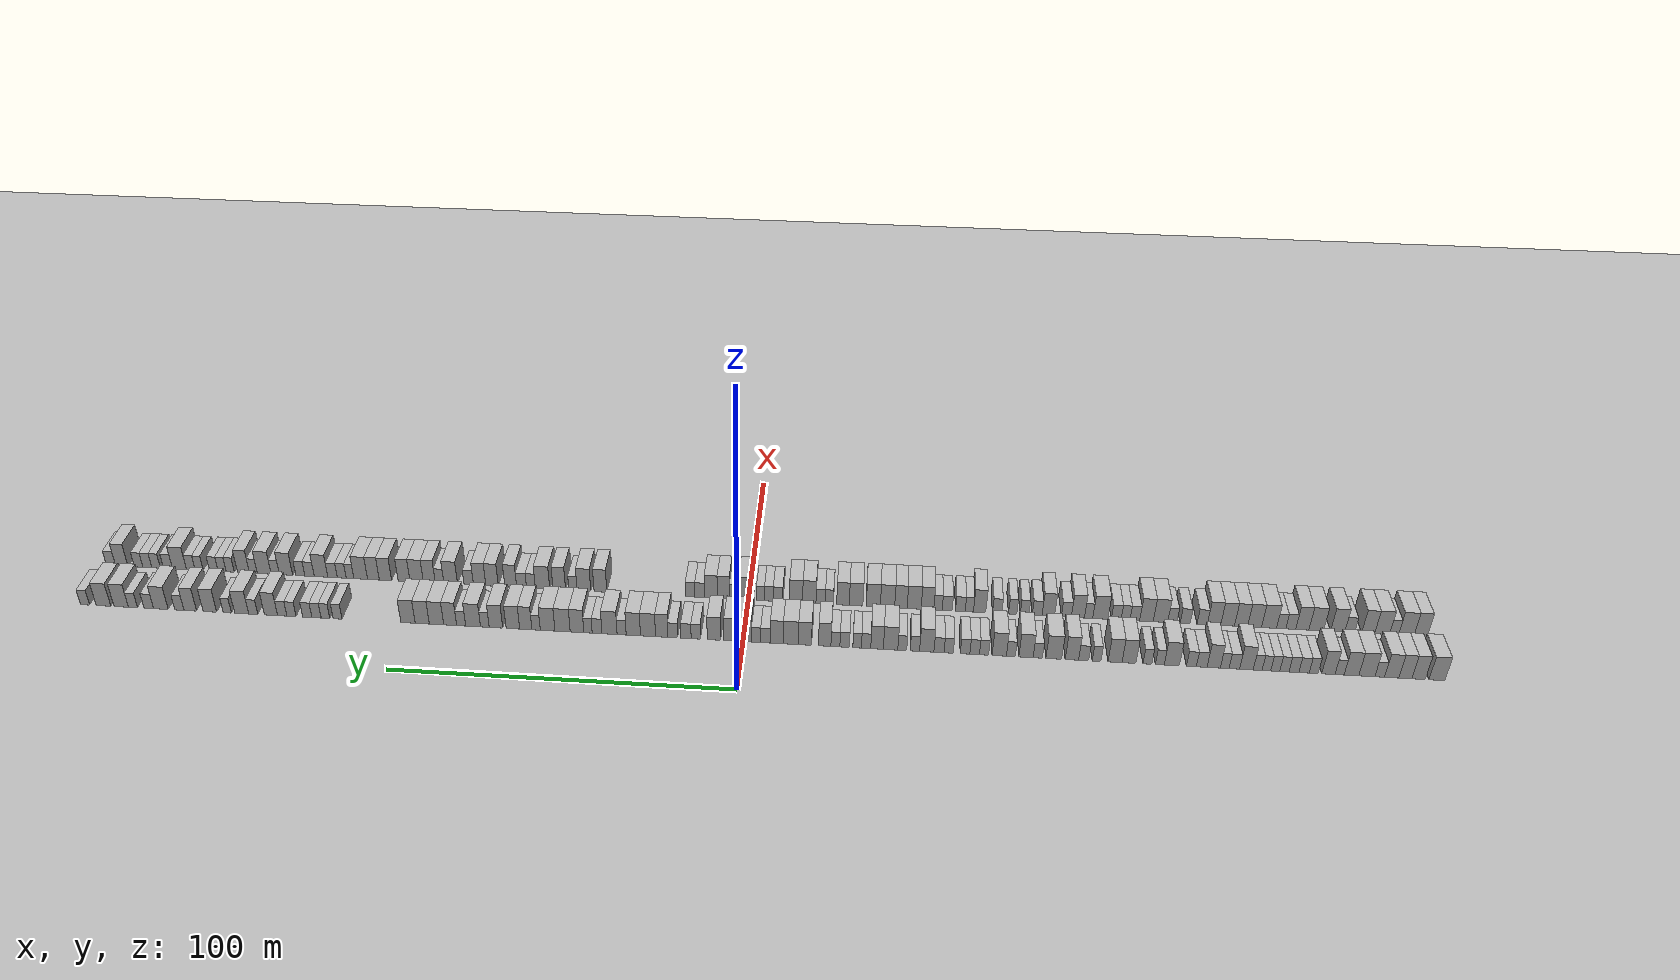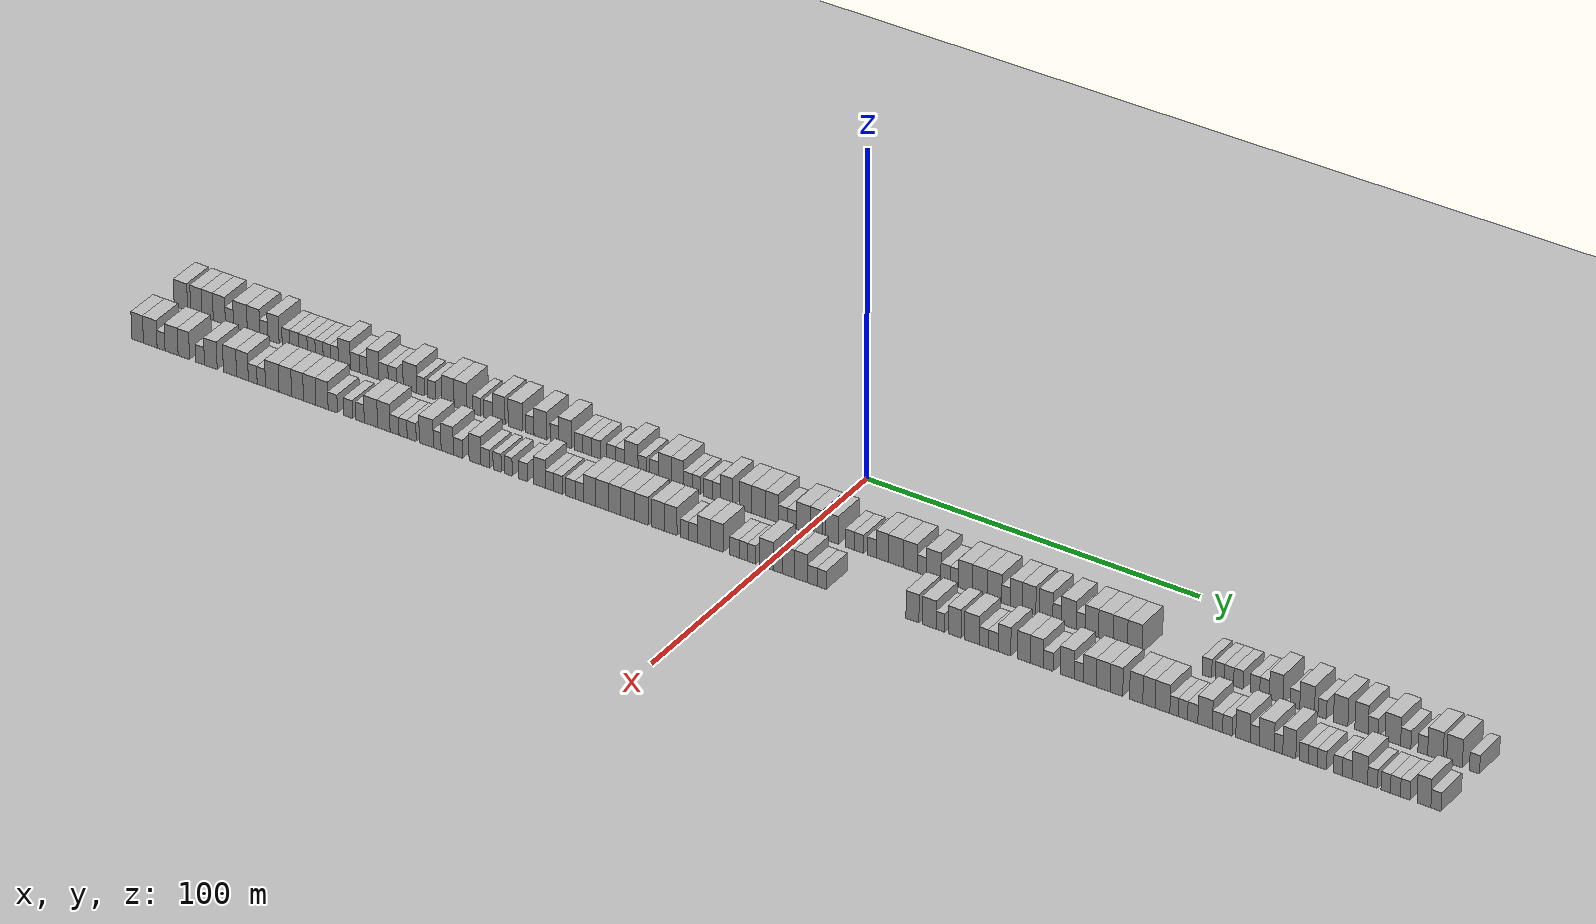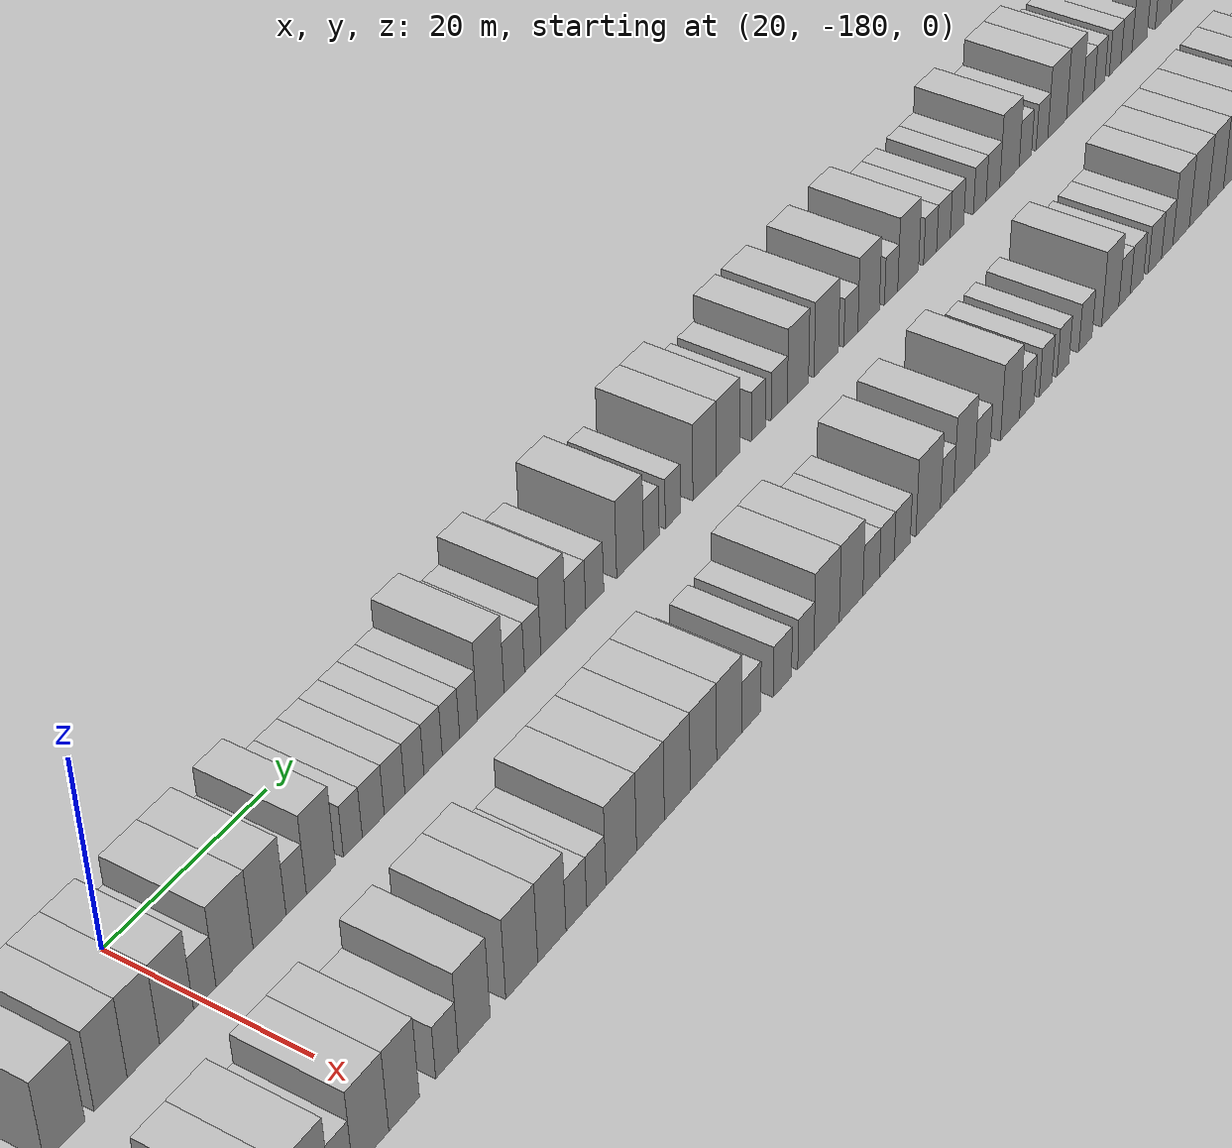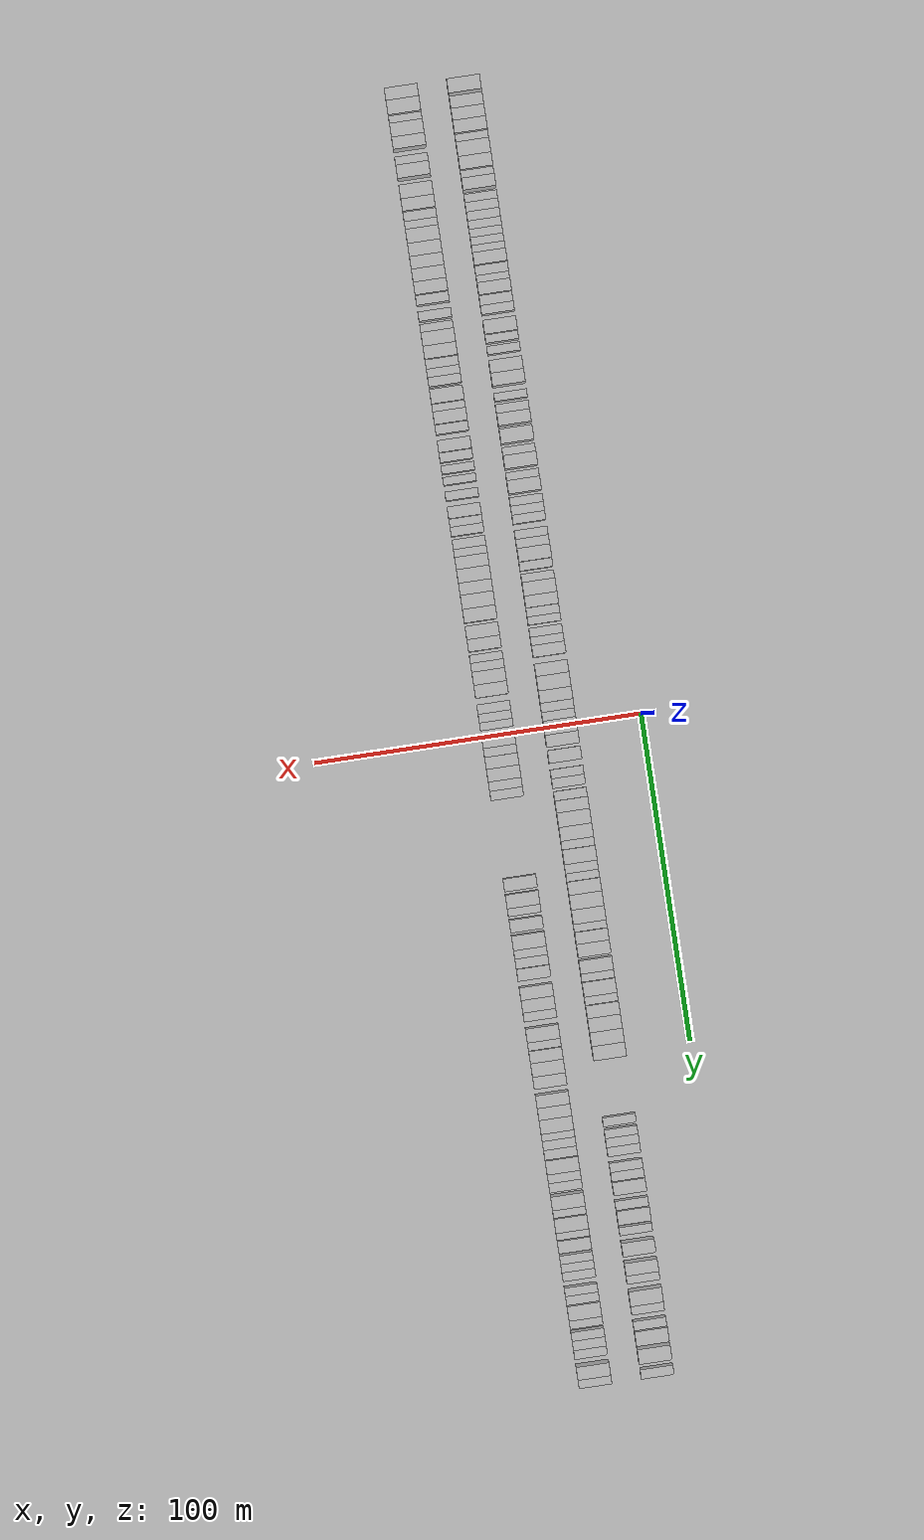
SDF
<?xml version="1.0" encoding="utf-8"?>

<sdf version="1.6">

   <world name="default">

      <gui fullscreen="0">

         <camera name="user_camera">

            <pose>-15 0 4.57585 0 0 0</pose>

            <view_controller>orbit</view_controller>

         </camera>

      </gui>

      <scene>

         <sky>

           <clouds>

             <speed>12</speed>

           </clouds>

         </sky>

         <ambient>0.4 0.4 0.4 1</ambient>

         <background>0.7 0.7 0.7 1</background>

         <shadows>1</shadows>

      </scene>

      <gravity>0 0 -9.8066</gravity>

      <magnetic_field>6e-06 2.3e-05 -4.2e-05</magnetic_field>

      <physics default="0" name="default_physics" type="ode">

         <ode>

            <solver>

               <type>quick</type>

               <iters>10</iters>

               <sor>1.0</sor>

               <use_dynamic_moi_rescaling>0</use_dynamic_moi_rescaling>

            </solver>

            <constraints>

               <cfm>0</cfm>

               <erp>0.2</erp>

               <contact_max_correcting_vel>100</contact_max_correcting_vel>

               <contact_surface_layer>0.001</contact_surface_layer>

            </constraints>

         </ode>

         <max_step_size>0.004</max_step_size>

         <real_time_factor>1</real_time_factor>

         <real_time_update_rate>250</real_time_update_rate>

      </physics>

      <light name="sun" type="directional">

         <cast_shadows>1</cast_shadows>

         <pose>0 0 10 0 0 0</pose>

         <diffuse>0.8 0.8 0.8 1</diffuse>

         <specular>0.2 0.2 0.2 1</specular>

         <attenuation>

            <range>1000</range>

            <constant>0.9</constant>

            <linear>0.01</linear>

            <quadratic>0.001</quadratic>

         </attenuation>

         <direction>-0.5 0.1 -0.9</direction>

      </light>

      <include>

         <name>ground_plane_1</name>

         <uri>model://HANNAS_ground_plane</uri>

         <pose>0 0 0  0 0 0</pose>

      </include>

      <include>

         <name>ground_plane_2</name>

         <uri>model://HANNAS_ground_plane</uri>

         <pose>100 0 0  0 0 0</pose>

      </include>

      <model name="building_1">

         <static>1</static>

         <pose frame="">25.0000 -195.8124 0 0.000000 0.000000 0.000000</pose>

         <link name="link">

            <pose frame="">0 0 4.50 0 0 0</pose>

            <collision name="collision">

               <geometry>

                  <box>

                     <size>10.0000 4.3751 9.0000</size>

                  </box>

               </geometry>

               <max_contacts>10</max_contacts>

               <surface>

                  <contact>

                     <ode/>

                  </contact>

                  <bounce/>

                  <friction>

                     <torsional>

                        <ode/>

                     </torsional>

                     <ode/>

                  </friction>

               </surface>

            </collision>

            <visual name="visual">

               <cast_shadows>0</cast_shadows>

               <geometry>

                  <box>

                     <size>10.0000 4.3751 9.0000</size>

                  </box>

               </geometry>

               <material>

                  <script>

                     <uri>model://HANNAS_wall/materials/scripts</uri>

                     <uri>model://HANNAS_wall/materials/textures</uri>

                     <name>vrc/HANNAS_wall</name>

                  </script>

               </material>

            </visual>

            <self_collide>0</self_collide>

            <enable_wind>0</enable_wind>

            <kinematic>0</kinematic>

         </link>

      </model>

      <model name="building_2">

         <static>1</static>

         <pose frame="">25.0000 -190.7950 0 0.000000 0.000000 0.000000</pose>

         <link name="link">

            <pose frame="">0 0 4.50 0 0 0</pose>

            <collision name="collision">

               <geometry>

                  <box>

                     <size>10.0000 3.6598 9.0000</size>

                  </box>

               </geometry>

               <max_contacts>10</max_contacts>

               <surface>

                  <contact>

                     <ode/>

                  </contact>

                  <bounce/>

                  <friction>

                     <torsional>

                        <ode/>

                     </torsional>

                     <ode/>

                  </friction>

               </surface>

            </collision>

            <visual name="visual">

               <cast_shadows>0</cast_shadows>

               <geometry>

                  <box>

                     <size>10.0000 3.6598 9.0000</size>

                  </box>

               </geometry>

               <material>

                  <script>

                     <uri>model://HANNAS_wall/materials/scripts</uri>

                     <uri>model://HANNAS_wall/materials/textures</uri>

                     <name>vrc/HANNAS_wall</name>

                  </script>

               </material>

            </visual>

            <self_collide>0</self_collide>

            <enable_wind>0</enable_wind>

            <kinematic>0</kinematic>

         </link>

      </model>

      <model name="building_3">

         <static>1</static>

         <pose frame="">25.0000 -187.1419 0 0.000000 0.000000 0.000000</pose>

         <link name="link">

            <pose frame="">0 0 4.50 0 0 0</pose>

            <collision name="collision">

               <geometry>

                  <box>

                     <size>10.0000 3.6464 9.0000</size>

                  </box>

               </geometry>

               <max_contacts>10</max_contacts>

               <surface>

                  <contact>

                     <ode/>

                  </contact>

                  <bounce/>

                  <friction>

                     <torsional>

                        <ode/>

                     </torsional>

                     <ode/>

                  </friction>

               </surface>

            </collision>

            <visual name="visual">

               <cast_shadows>0</cast_shadows>

               <geometry>

                  <box>

                     <size>10.0000 3.6464 9.0000</size>

                  </box>

               </geometry>

               <material>

                  <script>

                     <uri>model://HANNAS_wall/materials/scripts</uri>

                     <uri>model://HANNAS_wall/materials/textures</uri>

                     <name>vrc/HANNAS_wall</name>

                  </script>

               </material>

            </visual>

            <self_collide>0</self_collide>

            <enable_wind>0</enable_wind>

            <kinematic>0</kinematic>

         </link>

      </model>

      <model name="building_4">

         <static>1</static>

         <pose frame="">25.0000 -183.3582 0 0.000000 0.000000 0.000000</pose>

         <link name="link">

            <pose frame="">0 0 4.50 0 0 0</pose>

            <collision name="collision">

               <geometry>

                  <box>

                     <size>10.0000 3.9209 9.0000</size>

                  </box>

               </geometry>

               <max_contacts>10</max_contacts>

               <surface>

                  <contact>

                     <ode/>

                  </contact>

                  <bounce/>

                  <friction>

                     <torsional>

                        <ode/>

                     </torsional>

                     <ode/>

                  </friction>

               </surface>

            </collision>

            <visual name="visual">

               <cast_shadows>0</cast_shadows>

               <geometry>

                  <box>

                     <size>10.0000 3.9209 9.0000</size>

                  </box>

               </geometry>

               <material>

                  <script>

                     <uri>model://HANNAS_wall/materials/scripts</uri>

                     <uri>model://HANNAS_wall/materials/textures</uri>

                     <name>vrc/HANNAS_wall</name>

                  </script>

               </material>

            </visual>

            <self_collide>0</self_collide>

            <enable_wind>0</enable_wind>

            <kinematic>0</kinematic>

         </link>

      </model>

      <model name="building_5">

         <static>1</static>

         <pose frame="">25.0000 -180.0777 0 0.000000 0.000000 0.000000</pose>

         <link name="link">

            <pose frame="">0 0 3.00 0 0 0</pose>

            <collision name="collision">

               <geometry>

                  <box>

                     <size>10.0000 2.6402 6.0000</size>

                  </box>

               </geometry>

               <max_contacts>10</max_contacts>

               <surface>

                  <contact>

                     <ode/>

                  </contact>

                  <bounce/>

                  <friction>

                     <torsional>

                        <ode/>

                     </torsional>

                     <ode/>

                  </friction>

               </surface>

            </collision>

            <visual name="visual">

               <cast_shadows>0</cast_shadows>

               <geometry>

                  <box>

                     <size>10.0000 2.6402 6.0000</size>

                  </box>

               </geometry>

               <material>

                  <script>

                     <uri>model://HANNAS_wall/materials/scripts</uri>

                     <uri>model://HANNAS_wall/materials/textures</uri>

                     <name>vrc/HANNAS_wall</name>

                  </script>

               </material>

            </visual>

            <self_collide>0</self_collide>

            <enable_wind>0</enable_wind>

            <kinematic>0</kinematic>

         </link>

      </model>

      <model name="building_6">

         <static>1</static>

         <pose frame="">25.0000 -176.5355 0 0.000000 0.000000 0.000000</pose>

         <link name="link">

            <pose frame="">0 0 4.50 0 0 0</pose>

            <collision name="collision">

               <geometry>

                  <box>

                     <size>10.0000 4.4442 9.0000</size>

                  </box>

               </geometry>

               <max_contacts>10</max_contacts>

               <surface>

                  <contact>

                     <ode/>

                  </contact>

                  <bounce/>

                  <friction>

                     <torsional>

                        <ode/>

                     </torsional>

                     <ode/>

                  </friction>

               </surface>

            </collision>

            <visual name="visual">

               <cast_shadows>0</cast_shadows>

               <geometry>

                  <box>

                     <size>10.0000 4.4442 9.0000</size>

                  </box>

               </geometry>

               <material>

                  <script>

                     <uri>model://HANNAS_wall/materials/scripts</uri>

                     <uri>model://HANNAS_wall/materials/textures</uri>

                     <name>vrc/HANNAS_wall</name>

                  </script>

               </material>

            </visual>

            <self_collide>0</self_collide>

            <enable_wind>0</enable_wind>

            <kinematic>0</kinematic>

         </link>

      </model>

      <model name="building_7">

         <static>1</static>

         <pose frame="">25.0000 -172.2996 0 0.000000 0.000000 0.000000</pose>

         <link name="link">

            <pose frame="">0 0 4.50 0 0 0</pose>

            <collision name="collision">

               <geometry>

                  <box>

                     <size>10.0000 4.0277 9.0000</size>

                  </box>

               </geometry>

               <max_contacts>10</max_contacts>

               <surface>

                  <contact>

                     <ode/>

                  </contact>

                  <bounce/>

                  <friction>

                     <torsional>

                        <ode/>

                     </torsional>

                     <ode/>

                  </friction>

               </surface>

            </collision>

            <visual name="visual">

               <cast_shadows>0</cast_shadows>

               <geometry>

                  <box>

                     <size>10.0000 4.0277 9.0000</size>

                  </box>

               </geometry>

               <material>

                  <script>

                     <uri>model://HANNAS_wall/materials/scripts</uri>

                     <uri>model://HANNAS_wall/materials/textures</uri>

                     <name>vrc/HANNAS_wall</name>

                  </script>

               </material>

            </visual>

            <self_collide>0</self_collide>

            <enable_wind>0</enable_wind>

            <kinematic>0</kinematic>

         </link>

      </model>

      <model name="building_8">

         <static>1</static>

         <pose frame="">25.0000 -169.0211 0 0.000000 0.000000 0.000000</pose>

         <link name="link">

            <pose frame="">0 0 3.00 0 0 0</pose>

            <collision name="collision">

               <geometry>

                  <box>

                     <size>10.0000 2.5293 6.0000</size>

                  </box>

               </geometry>

               <max_contacts>10</max_contacts>

               <surface>

                  <contact>

                     <ode/>

                  </contact>

                  <bounce/>

                  <friction>

                     <torsional>

                        <ode/>

                     </torsional>

                     <ode/>

                  </friction>

               </surface>

            </collision>

            <visual name="visual">

               <cast_shadows>0</cast_shadows>

               <geometry>

                  <box>

                     <size>10.0000 2.5293 6.0000</size>

                  </box>

               </geometry>

               <material>

                  <script>

                     <uri>model://HANNAS_wall/materials/scripts</uri>

                     <uri>model://HANNAS_wall/materials/textures</uri>

                     <name>vrc/HANNAS_wall</name>

                  </script>

               </material>

            </visual>

            <self_collide>0</self_collide>

            <enable_wind>0</enable_wind>

            <kinematic>0</kinematic>

         </link>

      </model>

      <model name="building_9">

         <static>1</static>

         <pose frame="">25.0000 -165.9167 0 0.000000 0.000000 0.000000</pose>

         <link name="link">

            <pose frame="">0 0 4.50 0 0 0</pose>

            <collision name="collision">

               <geometry>

                  <box>

                     <size>10.0000 3.6795 9.0000</size>

                  </box>

               </geometry>

               <max_contacts>10</max_contacts>

               <surface>

                  <contact>

                     <ode/>

                  </contact>

                  <bounce/>

                  <friction>

                     <torsional>

                        <ode/>

                     </torsional>

                     <ode/>

                  </friction>

               </surface>

            </collision>

            <visual name="visual">

               <cast_shadows>0</cast_shadows>

               <geometry>

                  <box>

                     <size>10.0000 3.6795 9.0000</size>

                  </box>

               </geometry>

               <material>

                  <script>

                     <uri>model://HANNAS_wall/materials/scripts</uri>

                     <uri>model://HANNAS_wall/materials/textures</uri>

                     <name>vrc/HANNAS_wall</name>

                  </script>

               </material>

            </visual>

            <self_collide>0</self_collide>

            <enable_wind>0</enable_wind>

            <kinematic>0</kinematic>

         </link>

      </model>

      <model name="building_10">

         <static>1</static>

         <pose frame="">25.0000 -161.8491 0 0.000000 0.000000 0.000000</pose>

         <link name="link">

            <pose frame="">0 0 3.00 0 0 0</pose>

            <collision name="collision">

               <geometry>

                  <box>

                     <size>10.0000 2.4556 6.0000</size>

                  </box>

               </geometry>

               <max_contacts>10</max_contacts>

               <surface>

                  <contact>

                     <ode/>

                  </contact>

                  <bounce/>

                  <friction>

                     <torsional>

                        <ode/>

                     </torsional>

                     <ode/>

                  </friction>

               </surface>

            </collision>

            <visual name="visual">

               <cast_shadows>0</cast_shadows>

               <geometry>

                  <box>

                     <size>10.0000 2.4556 6.0000</size>

                  </box>

               </geometry>

               <material>

                  <script>

                     <uri>model://HANNAS_wall/materials/scripts</uri>

                     <uri>model://HANNAS_wall/materials/textures</uri>

                     <name>vrc/HANNAS_wall</name>

                  </script>

               </material>

            </visual>

            <self_collide>0</self_collide>

            <enable_wind>0</enable_wind>

            <kinematic>0</kinematic>

         </link>

      </model>

      <model name="building_11">

         <static>1</static>

         <pose frame="">25.0000 -159.1854 0 0.000000 0.000000 0.000000</pose>

         <link name="link">

            <pose frame="">0 0 3.00 0 0 0</pose>

            <collision name="collision">

               <geometry>

                  <box>

                     <size>10.0000 2.8718 6.0000</size>

                  </box>

               </geometry>

               <max_contacts>10</max_contacts>

               <surface>

                  <contact>

                     <ode/>

                  </contact>

                  <bounce/>

                  <friction>

                     <torsional>

                        <ode/>

                     </torsional>

                     <ode/>

                  </friction>

               </surface>

            </collision>

            <visual name="visual">

               <cast_shadows>0</cast_shadows>

               <geometry>

                  <box>

                     <size>10.0000 2.8718 6.0000</size>

                  </box>

               </geometry>

               <material>

                  <script>

                     <uri>model://HANNAS_wall/materials/scripts</uri>

                     <uri>model://HANNAS_wall/materials/textures</uri>

                     <name>vrc/HANNAS_wall</name>

                  </script>

               </material>

            </visual>

            <self_collide>0</self_collide>

            <enable_wind>0</enable_wind>

            <kinematic>0</kinematic>

         </link>

      </model>

      <model name="building_12">

         <static>1</static>

         <pose frame="">25.0000 -156.3743 0 0.000000 0.000000 0.000000</pose>

         <link name="link">

            <pose frame="">0 0 3.00 0 0 0</pose>

            <collision name="collision">

               <geometry>

                  <box>

                     <size>10.0000 2.7504 6.0000</size>

                  </box>

               </geometry>

               <max_contacts>10</max_contacts>

               <surface>

                  <contact>

                     <ode/>

                  </contact>

                  <bounce/>

                  <friction>

                     <torsional>

                        <ode/>

                     </torsional>

                     <ode/>

                  </friction>

               </surface>

            </collision>

            <visual name="visual">

               <cast_shadows>0</cast_shadows>

               <geometry>

                  <box>

                     <size>10.0000 2.7504 6.0000</size>

                  </box>

               </geometry>

               <material>

                  <script>

                     <uri>model://HANNAS_wall/materials/scripts</uri>

                     <uri>model://HANNAS_wall/materials/textures</uri>

                     <name>vrc/HANNAS_wall</name>

                  </script>

               </material>

            </visual>

            <self_collide>0</self_collide>

            <enable_wind>0</enable_wind>

            <kinematic>0</kinematic>

         </link>

      </model>

      <model name="building_13">

         <static>1</static>

         <pose frame="">25.0000 -153.7160 0 0.000000 0.000000 0.000000</pose>

         <link name="link">

            <pose frame="">0 0 3.00 0 0 0</pose>

            <collision name="collision">

               <geometry>

                  <box>

                     <size>10.0000 2.5661 6.0000</size>

                  </box>

               </geometry>

               <max_contacts>10</max_contacts>

               <surface>

                  <contact>

                     <ode/>

                  </contact>

                  <bounce/>

                  <friction>

                     <torsional>

                        <ode/>

                     </torsional>

                     <ode/>

                  </friction>

               </surface>

            </collision>

            <visual name="visual">

               <cast_shadows>0</cast_shadows>

               <geometry>

                  <box>

                     <size>10.0000 2.5661 6.0000</size>

                  </box>

               </geometry>

               <material>

                  <script>

                     <uri>model://HANNAS_wall/materials/scripts</uri>

                     <uri>model://HANNAS_wall/materials/textures</uri>

                     <name>vrc/HANNAS_wall</name>

                  </script>

               </material>

            </visual>

            <self_collide>0</self_collide>

            <enable_wind>0</enable_wind>

            <kinematic>0</kinematic>

         </link>

      </model>

      <model name="building_14">

         <static>1</static>

         <pose frame="">25.0000 -151.1776 0 0.000000 0.000000 0.000000</pose>

         <link name="link">

            <pose frame="">0 0 3.00 0 0 0</pose>

            <collision name="collision">

               <geometry>

                  <box>

                     <size>10.0000 2.5106 6.0000</size>

                  </box>

               </geometry>

               <max_contacts>10</max_contacts>

               <surface>

                  <contact>

                     <ode/>

                  </contact>

                  <bounce/>

                  <friction>

                     <torsional>

                        <ode/>

                     </torsional>

                     <ode/>

                  </friction>

               </surface>

            </collision>

            <visual name="visual">

               <cast_shadows>0</cast_shadows>

               <geometry>

                  <box>

                     <size>10.0000 2.5106 6.0000</size>

                  </box>

               </geometry>

               <material>

                  <script>

                     <uri>model://HANNAS_wall/materials/scripts</uri>

                     <uri>model://HANNAS_wall/materials/textures</uri>

                     <name>vrc/HANNAS_wall</name>

                  </script>

               </material>

            </visual>

            <self_collide>0</self_collide>

            <enable_wind>0</enable_wind>

            <kinematic>0</kinematic>

         </link>

      </model>

      <model name="building_15">

         <static>1</static>

         <pose frame="">25.0000 -148.7211 0 0.000000 0.000000 0.000000</pose>

         <link name="link">

            <pose frame="">0 0 3.00 0 0 0</pose>

            <collision name="collision">

               <geometry>

                  <box>

                     <size>10.0000 2.4023 6.0000</size>

                  </box>

               </geometry>

               <max_contacts>10</max_contacts>

               <surface>

                  <contact>

                     <ode/>

                  </contact>

                  <bounce/>

                  <friction>

                     <torsional>

                        <ode/>

                     </torsional>

                     <ode/>

                  </friction>

               </surface>

            </collision>

            <visual name="visual">

               <cast_shadows>0</cast_shadows>

               <geometry>

                  <box>

                     <size>10.0000 2.4023 6.0000</size>

                  </box>

               </geometry>

               <material>

                  <script>

                     <uri>model://HANNAS_wall/materials/scripts</uri>

                     <uri>model://HANNAS_wall/materials/textures</uri>

                     <name>vrc/HANNAS_wall</name>

                  </script>

               </material>

            </visual>

            <self_collide>0</self_collide>

            <enable_wind>0</enable_wind>

            <kinematic>0</kinematic>

         </link>

      </model>

      <model name="building_16">

         <static>1</static>

         <pose frame="">25.0000 -146.2873 0 0.000000 0.000000 0.000000</pose>

         <link name="link">

            <pose frame="">0 0 3.00 0 0 0</pose>

            <collision name="collision">

               <geometry>

                  <box>

                     <size>10.0000 2.4653 6.0000</size>

                  </box>

               </geometry>

               <max_contacts>10</max_contacts>

               <surface>

                  <contact>

                     <ode/>

                  </contact>

                  <bounce/>

                  <friction>

                     <torsional>

                        <ode/>

                     </torsional>

                     <ode/>

                  </friction>

               </surface>

            </collision>

            <visual name="visual">

               <cast_shadows>0</cast_shadows>

               <geometry>

                  <box>

                     <size>10.0000 2.4653 6.0000</size>

                  </box>

               </geometry>

               <material>

                  <script>

                     <uri>model://HANNAS_wall/materials/scripts</uri>

                     <uri>model://HANNAS_wall/materials/textures</uri>

                     <name>vrc/HANNAS_wall</name>

                  </script>

               </material>

            </visual>

            <self_collide>0</self_collide>

            <enable_wind>0</enable_wind>

            <kinematic>0</kinematic>

         </link>

      </model>

      <model name="building_17">

         <static>1</static>

         <pose frame="">25.0000 -143.1473 0 0.000000 0.000000 0.000000</pose>

         <link name="link">

            <pose frame="">0 0 4.50 0 0 0</pose>

            <collision name="collision">

               <geometry>

                  <box>

                     <size>10.0000 3.8147 9.0000</size>

                  </box>

               </geometry>

               <max_contacts>10</max_contacts>

               <surface>

                  <contact>

                     <ode/>

                  </contact>

                  <bounce/>

                  <friction>

                     <torsional>

                        <ode/>

                     </torsional>

                     <ode/>

                  </friction>

               </surface>

            </collision>

            <visual name="visual">

               <cast_shadows>0</cast_shadows>

               <geometry>

                  <box>

                     <size>10.0000 3.8147 9.0000</size>

                  </box>

               </geometry>

               <material>

                  <script>

                     <uri>model://HANNAS_wall/materials/scripts</uri>

                     <uri>model://HANNAS_wall/materials/textures</uri>

                     <name>vrc/HANNAS_wall</name>

                  </script>

               </material>

            </visual>

            <self_collide>0</self_collide>

            <enable_wind>0</enable_wind>

            <kinematic>0</kinematic>

         </link>

      </model>

      <model name="building_18">

         <static>1</static>

         <pose frame="">25.0000 -139.7681 0 0.000000 0.000000 0.000000</pose>

         <link name="link">

            <pose frame="">0 0 3.00 0 0 0</pose>

            <collision name="collision">

               <geometry>

                  <box>

                     <size>10.0000 2.9437 6.0000</size>

                  </box>

               </geometry>

               <max_contacts>10</max_contacts>

               <surface>

                  <contact>

                     <ode/>

                  </contact>

                  <bounce/>

                  <friction>

                     <torsional>

                        <ode/>

                     </torsional>

                     <ode/>

                  </friction>

               </surface>

            </collision>

            <visual name="visual">

               <cast_shadows>0</cast_shadows>

               <geometry>

                  <box>

                     <size>10.0000 2.9437 6.0000</size>

                  </box>

               </geometry>

               <material>

                  <script>

                     <uri>model://HANNAS_wall/materials/scripts</uri>

                     <uri>model://HANNAS_wall/materials/textures</uri>

                     <name>vrc/HANNAS_wall</name>

                  </script>

               </material>

            </visual>

            <self_collide>0</self_collide>

            <enable_wind>0</enable_wind>

            <kinematic>0</kinematic>

         </link>

      </model>

      <model name="building_19">

         <static>1</static>

         <pose frame="">25.0000 -137.0899 0 0.000000 0.000000 0.000000</pose>

         <link name="link">

            <pose frame="">0 0 3.00 0 0 0</pose>

            <collision name="collision">

               <geometry>

                  <box>

                     <size>10.0000 2.4126 6.0000</size>

                  </box>

               </geometry>

               <max_contacts>10</max_contacts>

               <surface>

                  <contact>

                     <ode/>

                  </contact>

                  <bounce/>

                  <friction>

                     <torsional>

                        <ode/>

                     </torsional>

                     <ode/>

                  </friction>

               </surface>

            </collision>

            <visual name="visual">

               <cast_shadows>0</cast_shadows>

               <geometry>

                  <box>

                     <size>10.0000 2.4126 6.0000</size>

                  </box>

               </geometry>

               <material>

                  <script>

                     <uri>model://HANNAS_wall/materials/scripts</uri>

                     <uri>model://HANNAS_wall/materials/textures</uri>

                     <name>vrc/HANNAS_wall</name>

                  </script>

               </material>

            </visual>

            <self_collide>0</self_collide>

            <enable_wind>0</enable_wind>

            <kinematic>0</kinematic>

         </link>

      </model>

      <model name="building_20">

         <static>1</static>

         <pose frame="">25.0000 -134.0270 0 0.000000 0.000000 0.000000</pose>

         <link name="link">

            <pose frame="">0 0 4.50 0 0 0</pose>

            <collision name="collision">

               <geometry>

                  <box>

                     <size>10.0000 3.7131 9.0000</size>

                  </box>

               </geometry>

               <max_contacts>10</max_contacts>

               <surface>

                  <contact>

                     <ode/>

                  </contact>

                  <bounce/>

                  <friction>

                     <torsional>

                        <ode/>

                     </torsional>

                     <ode/>

                  </friction>

               </surface>

            </collision>

            <visual name="visual">

               <cast_shadows>0</cast_shadows>

               <geometry>

                  <box>

                     <size>10.0000 3.7131 9.0000</size>

                  </box>

               </geometry>

               <material>

                  <script>

                     <uri>model://HANNAS_wall/materials/scripts</uri>

                     <uri>model://HANNAS_wall/materials/textures</uri>

                     <name>vrc/HANNAS_wall</name>

                  </script>

               </material>

            </visual>

            <self_collide>0</self_collide>

            <enable_wind>0</enable_wind>

            <kinematic>0</kinematic>

         </link>

      </model>

      <model name="building_21">

         <static>1</static>

         <pose frame="">25.0000 -130.6746 0 0.000000 0.000000 0.000000</pose>

         <link name="link">

            <pose frame="">0 0 3.00 0 0 0</pose>

            <collision name="collision">

               <geometry>

                  <box>

                     <size>10.0000 2.9919 6.0000</size>

                  </box>

               </geometry>

               <max_contacts>10</max_contacts>

               <surface>

                  <contact>

                     <ode/>

                  </contact>

                  <bounce/>

                  <friction>

                     <torsional>

                        <ode/>

                     </torsional>

                     <ode/>

                  </friction>

               </surface>

            </collision>

            <visual name="visual">

               <cast_shadows>0</cast_shadows>

               <geometry>

                  <box>

                     <size>10.0000 2.9919 6.0000</size>

                  </box>

               </geometry>

               <material>

                  <script>

                     <uri>model://HANNAS_wall/materials/scripts</uri>

                     <uri>model://HANNAS_wall/materials/textures</uri>

                     <name>vrc/HANNAS_wall</name>

                  </script>

               </material>

            </visual>

            <self_collide>0</self_collide>

            <enable_wind>0</enable_wind>

            <kinematic>0</kinematic>

         </link>

      </model>

      <model name="building_22">

         <static>1</static>

         <pose frame="">25.0000 -127.7962 0 0.000000 0.000000 0.000000</pose>

         <link name="link">

            <pose frame="">0 0 3.00 0 0 0</pose>

            <collision name="collision">

               <geometry>

                  <box>

                     <size>10.0000 2.7648 6.0000</size>

                  </box>

               </geometry>

               <max_contacts>10</max_contacts>

               <surface>

                  <contact>

                     <ode/>

                  </contact>

                  <bounce/>

                  <friction>

                     <torsional>

                        <ode/>

                     </torsional>

                     <ode/>

                  </friction>

               </surface>

            </collision>

            <visual name="visual">

               <cast_shadows>0</cast_shadows>

               <geometry>

                  <box>

                     <size>10.0000 2.7648 6.0000</size>

                  </box>

               </geometry>

               <material>

                  <script>

                     <uri>model://HANNAS_wall/materials/scripts</uri>

                     <uri>model://HANNAS_wall/materials/textures</uri>

                     <name>vrc/HANNAS_wall</name>

                  </script>

               </material>

            </visual>

            <self_collide>0</self_collide>

            <enable_wind>0</enable_wind>

            <kinematic>0</kinematic>

         </link>

      </model>

      <model name="building_23">

         <static>1</static>

         <pose frame="">25.0000 -122.2957 0 0.000000 0.000000 0.000000</pose>

         <link name="link">

            <pose frame="">0 0 4.50 0 0 0</pose>

            <collision name="collision">

               <geometry>

                  <box>

                     <size>10.0000 4.2361 9.0000</size>

                  </box>

               </geometry>

               <max_contacts>10</max_contacts>

               <surface>

                  <contact>

                     <ode/>

                  </contact>

                  <bounce/>

                  <friction>

                     <torsional>

                        <ode/>

                     </torsional>

                     <ode/>

                  </friction>

               </surface>

            </collision>

            <visual name="visual">

               <cast_shadows>0</cast_shadows>

               <geometry>

                  <box>

                     <size>10.0000 4.2361 9.0000</size>

                  </box>

               </geometry>

               <material>

                  <script>

                     <uri>model://HANNAS_wall/materials/scripts</uri>

                     <uri>model://HANNAS_wall/materials/textures</uri>

                     <name>vrc/HANNAS_wall</name>

                  </script>

               </material>

            </visual>

            <self_collide>0</self_collide>

            <enable_wind>0</enable_wind>

            <kinematic>0</kinematic>

         </link>

      </model>

      <model name="building_24">

         <static>1</static>

         <pose frame="">25.0000 -118.9344 0 0.000000 0.000000 0.000000</pose>

         <link name="link">

            <pose frame="">0 0 3.00 0 0 0</pose>

            <collision name="collision">

               <geometry>

                  <box>

                     <size>10.0000 2.4865 6.0000</size>

                  </box>

               </geometry>

               <max_contacts>10</max_contacts>

               <surface>

                  <contact>

                     <ode/>

                  </contact>

                  <bounce/>

                  <friction>

                     <torsional>

                        <ode/>

                     </torsional>

                     <ode/>

                  </friction>

               </surface>

            </collision>

            <visual name="visual">

               <cast_shadows>0</cast_shadows>

               <geometry>

                  <box>

                     <size>10.0000 2.4865 6.0000</size>

                  </box>

               </geometry>

               <material>

                  <script>

                     <uri>model://HANNAS_wall/materials/scripts</uri>

                     <uri>model://HANNAS_wall/materials/textures</uri>

                     <name>vrc/HANNAS_wall</name>

                  </script>

               </material>

            </visual>

            <self_collide>0</self_collide>

            <enable_wind>0</enable_wind>

            <kinematic>0</kinematic>

         </link>

      </model>

      <model name="building_25">

         <static>1</static>

         <pose frame="">25.0000 -115.4437 0 0.000000 0.000000 0.000000</pose>

         <link name="link">

            <pose frame="">0 0 3.00 0 0 0</pose>

            <collision name="collision">

               <geometry>

                  <box>

                     <size>10.0000 2.4949 6.0000</size>

                  </box>

               </geometry>

               <max_contacts>10</max_contacts>

               <surface>

                  <contact>

                     <ode/>

                  </contact>

                  <bounce/>

                  <friction>

                     <torsional>

                        <ode/>

                     </torsional>

                     <ode/>

                  </friction>

               </surface>

            </collision>

            <visual name="visual">

               <cast_shadows>0</cast_shadows>

               <geometry>

                  <box>

                     <size>10.0000 2.4949 6.0000</size>

                  </box>

               </geometry>

               <material>

                  <script>

                     <uri>model://HANNAS_wall/materials/scripts</uri>

                     <uri>model://HANNAS_wall/materials/textures</uri>

                     <name>vrc/HANNAS_wall</name>

                  </script>

               </material>

            </visual>

            <self_collide>0</self_collide>

            <enable_wind>0</enable_wind>

            <kinematic>0</kinematic>

         </link>

      </model>

      <model name="building_26">

         <static>1</static>

         <pose frame="">25.0000 -110.2514 0 0.000000 0.000000 0.000000</pose>

         <link name="link">

            <pose frame="">0 0 4.50 0 0 0</pose>

            <collision name="collision">

               <geometry>

                  <box>

                     <size>10.0000 3.8897 9.0000</size>

                  </box>

               </geometry>

               <max_contacts>10</max_contacts>

               <surface>

                  <contact>

                     <ode/>

                  </contact>

                  <bounce/>

                  <friction>

                     <torsional>

                        <ode/>

                     </torsional>

                     <ode/>

                  </friction>

               </surface>

            </collision>

            <visual name="visual">

               <cast_shadows>0</cast_shadows>

               <geometry>

                  <box>

                     <size>10.0000 3.8897 9.0000</size>

                  </box>

               </geometry>

               <material>

                  <script>

                     <uri>model://HANNAS_wall/materials/scripts</uri>

                     <uri>model://HANNAS_wall/materials/textures</uri>

                     <name>vrc/HANNAS_wall</name>

                  </script>

               </material>

            </visual>

            <self_collide>0</self_collide>

            <enable_wind>0</enable_wind>

            <kinematic>0</kinematic>

         </link>

      </model>

      <model name="building_27">

         <static>1</static>

         <pose frame="">25.0000 -106.3323 0 0.000000 0.000000 0.000000</pose>

         <link name="link">

            <pose frame="">0 0 4.50 0 0 0</pose>

            <collision name="collision">

               <geometry>

                  <box>

                     <size>10.0000 3.9485 9.0000</size>

                  </box>

               </geometry>

               <max_contacts>10</max_contacts>

               <surface>

                  <contact>

                     <ode/>

                  </contact>

                  <bounce/>

                  <friction>

                     <torsional>

                        <ode/>

                     </torsional>

                     <ode/>

                  </friction>

               </surface>

            </collision>

            <visual name="visual">

               <cast_shadows>0</cast_shadows>

               <geometry>

                  <box>

                     <size>10.0000 3.9485 9.0000</size>

                  </box>

               </geometry>

               <material>

                  <script>

                     <uri>model://HANNAS_wall/materials/scripts</uri>

                     <uri>model://HANNAS_wall/materials/textures</uri>

                     <name>vrc/HANNAS_wall</name>

                  </script>

               </material>

            </visual>

            <self_collide>0</self_collide>

            <enable_wind>0</enable_wind>

            <kinematic>0</kinematic>

         </link>

      </model>

      <model name="building_28">

         <static>1</static>

         <pose frame="">25.0000 -101.1371 0 0.000000 0.000000 0.000000</pose>

         <link name="link">

            <pose frame="">0 0 3.00 0 0 0</pose>

            <collision name="collision">

               <geometry>

                  <box>

                     <size>10.0000 2.4418 6.0000</size>

                  </box>

               </geometry>

               <max_contacts>10</max_contacts>

               <surface>

                  <contact>

                     <ode/>

                  </contact>

                  <bounce/>

                  <friction>

                     <torsional>

                        <ode/>

                     </torsional>

                     <ode/>

                  </friction>

               </surface>

            </collision>

            <visual name="visual">

               <cast_shadows>0</cast_shadows>

               <geometry>

                  <box>

                     <size>10.0000 2.4418 6.0000</size>

                  </box>

               </geometry>

               <material>

                  <script>

                     <uri>model://HANNAS_wall/materials/scripts</uri>

                     <uri>model://HANNAS_wall/materials/textures</uri>

                     <name>vrc/HANNAS_wall</name>

                  </script>

               </material>

            </visual>

            <self_collide>0</self_collide>

            <enable_wind>0</enable_wind>

            <kinematic>0</kinematic>

         </link>

      </model>

      <model name="building_29">

         <static>1</static>

         <pose frame="">25.0000 -97.4838 0 0.000000 0.000000 0.000000</pose>

         <link name="link">

            <pose frame="">0 0 3.00 0 0 0</pose>

            <collision name="collision">

               <geometry>

                  <box>

                     <size>10.0000 2.8649 6.0000</size>

                  </box>

               </geometry>

               <max_contacts>10</max_contacts>

               <surface>

                  <contact>

                     <ode/>

                  </contact>

                  <bounce/>

                  <friction>

                     <torsional>

                        <ode/>

                     </torsional>

                     <ode/>

                  </friction>

               </surface>

            </collision>

            <visual name="visual">

               <cast_shadows>0</cast_shadows>

               <geometry>

                  <box>

                     <size>10.0000 2.8649 6.0000</size>

                  </box>

               </geometry>

               <material>

                  <script>

                     <uri>model://HANNAS_wall/materials/scripts</uri>

                     <uri>model://HANNAS_wall/materials/textures</uri>

                     <name>vrc/HANNAS_wall</name>

                  </script>

               </material>

            </visual>

            <self_collide>0</self_collide>

            <enable_wind>0</enable_wind>

            <kinematic>0</kinematic>

         </link>

      </model>

      <model name="building_30">

         <static>1</static>

         <pose frame="">25.0000 -94.1622 0 0.000000 0.000000 0.000000</pose>

         <link name="link">

            <pose frame="">0 0 4.50 0 0 0</pose>

            <collision name="collision">

               <geometry>

                  <box>

                     <size>10.0000 3.7783 9.0000</size>

                  </box>

               </geometry>

               <max_contacts>10</max_contacts>

               <surface>

                  <contact>

                     <ode/>

                  </contact>

                  <bounce/>

                  <friction>

                     <torsional>

                        <ode/>

                     </torsional>

                     <ode/>

                  </friction>

               </surface>

            </collision>

            <visual name="visual">

               <cast_shadows>0</cast_shadows>

               <geometry>

                  <box>

                     <size>10.0000 3.7783 9.0000</size>

                  </box>

               </geometry>

               <material>

                  <script>

                     <uri>model://HANNAS_wall/materials/scripts</uri>

                     <uri>model://HANNAS_wall/materials/textures</uri>

                     <name>vrc/HANNAS_wall</name>

                  </script>

               </material>

            </visual>

            <self_collide>0</self_collide>

            <enable_wind>0</enable_wind>

            <kinematic>0</kinematic>

         </link>

      </model>

      <model name="building_31">

         <static>1</static>

         <pose frame="">25.0000 -89.0398 0 0.000000 0.000000 0.000000</pose>

         <link name="link">

            <pose frame="">0 0 4.50 0 0 0</pose>

            <collision name="collision">

               <geometry>

                  <box>

                     <size>10.0000 4.4664 9.0000</size>

                  </box>

               </geometry>

               <max_contacts>10</max_contacts>

               <surface>

                  <contact>

                     <ode/>

                  </contact>

                  <bounce/>

                  <friction>

                     <torsional>

                        <ode/>

                     </torsional>

                     <ode/>

                  </friction>

               </surface>

            </collision>

            <visual name="visual">

               <cast_shadows>0</cast_shadows>

               <geometry>

                  <box>

                     <size>10.0000 4.4664 9.0000</size>

                  </box>

               </geometry>

               <material>

                  <script>

                     <uri>model://HANNAS_wall/materials/scripts</uri>

                     <uri>model://HANNAS_wall/materials/textures</uri>

                     <name>vrc/HANNAS_wall</name>

                  </script>

               </material>

            </visual>

            <self_collide>0</self_collide>

            <enable_wind>0</enable_wind>

            <kinematic>0</kinematic>

         </link>

      </model>

      <model name="building_32">

         <static>1</static>

         <pose frame="">25.0000 -84.5046 0 0.000000 0.000000 0.000000</pose>

         <link name="link">

            <pose frame="">0 0 3.00 0 0 0</pose>

            <collision name="collision">

               <geometry>

                  <box>

                     <size>10.0000 2.6039 6.0000</size>

                  </box>

               </geometry>

               <max_contacts>10</max_contacts>

               <surface>

                  <contact>

                     <ode/>

                  </contact>

                  <bounce/>

                  <friction>

                     <torsional>

                        <ode/>

                     </torsional>

                     <ode/>

                  </friction>

               </surface>

            </collision>

            <visual name="visual">

               <cast_shadows>0</cast_shadows>

               <geometry>

                  <box>

                     <size>10.0000 2.6039 6.0000</size>

                  </box>

               </geometry>

               <material>

                  <script>

                     <uri>model://HANNAS_wall/materials/scripts</uri>

                     <uri>model://HANNAS_wall/materials/textures</uri>

                     <name>vrc/HANNAS_wall</name>

                  </script>

               </material>

            </visual>

            <self_collide>0</self_collide>

            <enable_wind>0</enable_wind>

            <kinematic>0</kinematic>

         </link>

      </model>

      <model name="building_33">

         <static>1</static>

         <pose frame="">25.0000 -81.1677 0 0.000000 0.000000 0.000000</pose>

         <link name="link">

            <pose frame="">0 0 4.50 0 0 0</pose>

            <collision name="collision">

               <geometry>

                  <box>

                     <size>10.0000 4.0699 9.0000</size>

                  </box>

               </geometry>

               <max_contacts>10</max_contacts>

               <surface>

                  <contact>

                     <ode/>

                  </contact>

                  <bounce/>

                  <friction>

                     <torsional>

                        <ode/>

                     </torsional>

                     <ode/>

                  </friction>

               </surface>

            </collision>

            <visual name="visual">

               <cast_shadows>0</cast_shadows>

               <geometry>

                  <box>

                     <size>10.0000 4.0699 9.0000</size>

                  </box>

               </geometry>

               <material>

                  <script>

                     <uri>model://HANNAS_wall/materials/scripts</uri>

                     <uri>model://HANNAS_wall/materials/textures</uri>

                     <name>vrc/HANNAS_wall</name>

                  </script>

               </material>

            </visual>

            <self_collide>0</self_collide>

            <enable_wind>0</enable_wind>

            <kinematic>0</kinematic>

         </link>

      </model>

      <model name="building_34">

         <static>1</static>

         <pose frame="">25.0000 -76.8595 0 0.000000 0.000000 0.000000</pose>

         <link name="link">

            <pose frame="">0 0 3.00 0 0 0</pose>

            <collision name="collision">

               <geometry>

                  <box>

                     <size>10.0000 2.5464 6.0000</size>

                  </box>

               </geometry>

               <max_contacts>10</max_contacts>

               <surface>

                  <contact>

                     <ode/>

                  </contact>

                  <bounce/>

                  <friction>

                     <torsional>

                        <ode/>

                     </torsional>

                     <ode/>

                  </friction>

               </surface>

            </collision>

            <visual name="visual">

               <cast_shadows>0</cast_shadows>

               <geometry>

                  <box>

                     <size>10.0000 2.5464 6.0000</size>

                  </box>

               </geometry>

               <material>

                  <script>

                     <uri>model://HANNAS_wall/materials/scripts</uri>

                     <uri>model://HANNAS_wall/materials/textures</uri>

                     <name>vrc/HANNAS_wall</name>

                  </script>

               </material>

            </visual>

            <self_collide>0</self_collide>

            <enable_wind>0</enable_wind>

            <kinematic>0</kinematic>

         </link>

      </model>

      <model name="building_35">

         <static>1</static>

         <pose frame="">25.0000 -73.5526 0 0.000000 0.000000 0.000000</pose>

         <link name="link">

            <pose frame="">0 0 4.50 0 0 0</pose>

            <collision name="collision">

               <geometry>

                  <box>

                     <size>10.0000 4.0674 9.0000</size>

                  </box>

               </geometry>

               <max_contacts>10</max_contacts>

               <surface>

                  <contact>

                     <ode/>

                  </contact>

                  <bounce/>

                  <friction>

                     <torsional>

                        <ode/>

                     </torsional>

                     <ode/>

                  </friction>

               </surface>

            </collision>

            <visual name="visual">

               <cast_shadows>0</cast_shadows>

               <geometry>

                  <box>

                     <size>10.0000 4.0674 9.0000</size>

                  </box>

               </geometry>

               <material>

                  <script>

                     <uri>model://HANNAS_wall/materials/scripts</uri>

                     <uri>model://HANNAS_wall/materials/textures</uri>

                     <name>vrc/HANNAS_wall</name>

                  </script>

               </material>

            </visual>

            <self_collide>0</self_collide>

            <enable_wind>0</enable_wind>

            <kinematic>0</kinematic>

         </link>

      </model>

      <model name="building_36">

         <static>1</static>

         <pose frame="">25.0000 -69.2227 0 0.000000 0.000000 0.000000</pose>

         <link name="link">

            <pose frame="">0 0 3.00 0 0 0</pose>

            <collision name="collision">

               <geometry>

                  <box>

                     <size>10.0000 2.5924 6.0000</size>

                  </box>

               </geometry>

               <max_contacts>10</max_contacts>

               <surface>

                  <contact>

                     <ode/>

                  </contact>

                  <bounce/>

                  <friction>

                     <torsional>

                        <ode/>

                     </torsional>

                     <ode/>

                  </friction>

               </surface>

            </collision>

            <visual name="visual">

               <cast_shadows>0</cast_shadows>

               <geometry>

                  <box>

                     <size>10.0000 2.5924 6.0000</size>

                  </box>

               </geometry>

               <material>

                  <script>

                     <uri>model://HANNAS_wall/materials/scripts</uri>

                     <uri>model://HANNAS_wall/materials/textures</uri>

                     <name>vrc/HANNAS_wall</name>

                  </script>

               </material>

            </visual>

            <self_collide>0</self_collide>

            <enable_wind>0</enable_wind>

            <kinematic>0</kinematic>

         </link>

      </model>

      <model name="building_37">

         <static>1</static>

         <pose frame="">25.0000 -66.5518 0 0.000000 0.000000 0.000000</pose>

         <link name="link">

            <pose frame="">0 0 3.00 0 0 0</pose>

            <collision name="collision">

               <geometry>

                  <box>

                     <size>10.0000 2.7495 6.0000</size>

                  </box>

               </geometry>

               <max_contacts>10</max_contacts>

               <surface>

                  <contact>

                     <ode/>

                  </contact>

                  <bounce/>

                  <friction>

                     <torsional>

                        <ode/>

                     </torsional>

                     <ode/>

                  </friction>

               </surface>

            </collision>

            <visual name="visual">

               <cast_shadows>0</cast_shadows>

               <geometry>

                  <box>

                     <size>10.0000 2.7495 6.0000</size>

                  </box>

               </geometry>

               <material>

                  <script>

                     <uri>model://HANNAS_wall/materials/scripts</uri>

                     <uri>model://HANNAS_wall/materials/textures</uri>

                     <name>vrc/HANNAS_wall</name>

                  </script>

               </material>

            </visual>

            <self_collide>0</self_collide>

            <enable_wind>0</enable_wind>

            <kinematic>0</kinematic>

         </link>

      </model>

      <model name="building_38">

         <static>1</static>

         <pose frame="">25.0000 -63.8082 0 0.000000 0.000000 0.000000</pose>

         <link name="link">

            <pose frame="">0 0 3.00 0 0 0</pose>

            <collision name="collision">

               <geometry>

                  <box>

                     <size>10.0000 2.7377 6.0000</size>

                  </box>

               </geometry>

               <max_contacts>10</max_contacts>

               <surface>

                  <contact>

                     <ode/>

                  </contact>

                  <bounce/>

                  <friction>

                     <torsional>

                        <ode/>

                     </torsional>

                     <ode/>

                  </friction>

               </surface>

            </collision>

            <visual name="visual">

               <cast_shadows>0</cast_shadows>

               <geometry>

                  <box>

                     <size>10.0000 2.7377 6.0000</size>

                  </box>

               </geometry>

               <material>

                  <script>

                     <uri>model://HANNAS_wall/materials/scripts</uri>

                     <uri>model://HANNAS_wall/materials/textures</uri>

                     <name>vrc/HANNAS_wall</name>

                  </script>

               </material>

            </visual>

            <self_collide>0</self_collide>

            <enable_wind>0</enable_wind>

            <kinematic>0</kinematic>

         </link>

      </model>

      <model name="building_39">

         <static>1</static>

         <pose frame="">25.0000 -59.1197 0 0.000000 0.000000 0.000000</pose>

         <link name="link">

            <pose frame="">0 0 3.00 0 0 0</pose>

            <collision name="collision">

               <geometry>

                  <box>

                     <size>10.0000 2.6392 6.0000</size>

                  </box>

               </geometry>

               <max_contacts>10</max_contacts>

               <surface>

                  <contact>

                     <ode/>

                  </contact>

                  <bounce/>

                  <friction>

                     <torsional>

                        <ode/>

                     </torsional>

                     <ode/>

                  </friction>

               </surface>

            </collision>

            <visual name="visual">

               <cast_shadows>0</cast_shadows>

               <geometry>

                  <box>

                     <size>10.0000 2.6392 6.0000</size>

                  </box>

               </geometry>

               <material>

                  <script>

                     <uri>model://HANNAS_wall/materials/scripts</uri>

                     <uri>model://HANNAS_wall/materials/textures</uri>

                     <name>vrc/HANNAS_wall</name>

                  </script>

               </material>

            </visual>

            <self_collide>0</self_collide>

            <enable_wind>0</enable_wind>

            <kinematic>0</kinematic>

         </link>

      </model>

      <model name="building_40">

         <static>1</static>

         <pose frame="">25.0000 -56.3586 0 0.000000 0.000000 0.000000</pose>

         <link name="link">

            <pose frame="">0 0 3.00 0 0 0</pose>

            <collision name="collision">

               <geometry>

                  <box>

                     <size>10.0000 2.8830 6.0000</size>

                  </box>

               </geometry>

               <max_contacts>10</max_contacts>

               <surface>

                  <contact>

                     <ode/>

                  </contact>

                  <bounce/>

                  <friction>

                     <torsional>

                        <ode/>

                     </torsional>

                     <ode/>

                  </friction>

               </surface>

            </collision>

            <visual name="visual">

               <cast_shadows>0</cast_shadows>

               <geometry>

                  <box>

                     <size>10.0000 2.8830 6.0000</size>

                  </box>

               </geometry>

               <material>

                  <script>

                     <uri>model://HANNAS_wall/materials/scripts</uri>

                     <uri>model://HANNAS_wall/materials/textures</uri>

                     <name>vrc/HANNAS_wall</name>

                  </script>

               </material>

            </visual>

            <self_collide>0</self_collide>

            <enable_wind>0</enable_wind>

            <kinematic>0</kinematic>

         </link>

      </model>

      <model name="building_41">

         <static>1</static>

         <pose frame="">25.0000 -52.8612 0 0.000000 0.000000 0.000000</pose>

         <link name="link">

            <pose frame="">0 0 4.50 0 0 0</pose>

            <collision name="collision">

               <geometry>

                  <box>

                     <size>10.0000 4.1118 9.0000</size>

                  </box>

               </geometry>

               <max_contacts>10</max_contacts>

               <surface>

                  <contact>

                     <ode/>

                  </contact>

                  <bounce/>

                  <friction>

                     <torsional>

                        <ode/>

                     </torsional>

                     <ode/>

                  </friction>

               </surface>

            </collision>

            <visual name="visual">

               <cast_shadows>0</cast_shadows>

               <geometry>

                  <box>

                     <size>10.0000 4.1118 9.0000</size>

                  </box>

               </geometry>

               <material>

                  <script>

                     <uri>model://HANNAS_wall/materials/scripts</uri>

                     <uri>model://HANNAS_wall/materials/textures</uri>

                     <name>vrc/HANNAS_wall</name>

                  </script>

               </material>

            </visual>

            <self_collide>0</self_collide>

            <enable_wind>0</enable_wind>

            <kinematic>0</kinematic>

         </link>

      </model>

      <model name="building_42">

         <static>1</static>

         <pose frame="">25.0000 -49.4645 0 0.000000 0.000000 0.000000</pose>

         <link name="link">

            <pose frame="">0 0 3.00 0 0 0</pose>

            <collision name="collision">

               <geometry>

                  <box>

                     <size>10.0000 2.6816 6.0000</size>

                  </box>

               </geometry>

               <max_contacts>10</max_contacts>

               <surface>

                  <contact>

                     <ode/>

                  </contact>

                  <bounce/>

                  <friction>

                     <torsional>

                        <ode/>

                     </torsional>

                     <ode/>

                  </friction>

               </surface>

            </collision>

            <visual name="visual">

               <cast_shadows>0</cast_shadows>

               <geometry>

                  <box>

                     <size>10.0000 2.6816 6.0000</size>

                  </box>

               </geometry>

               <material>

                  <script>

                     <uri>model://HANNAS_wall/materials/scripts</uri>

                     <uri>model://HANNAS_wall/materials/textures</uri>

                     <name>vrc/HANNAS_wall</name>

                  </script>

               </material>

            </visual>

            <self_collide>0</self_collide>

            <enable_wind>0</enable_wind>

            <kinematic>0</kinematic>

         </link>

      </model>

      <model name="building_43">

         <static>1</static>

         <pose frame="">25.0000 -45.8396 0 0.000000 0.000000 0.000000</pose>

         <link name="link">

            <pose frame="">0 0 3.00 0 0 0</pose>

            <collision name="collision">

               <geometry>

                  <box>

                     <size>10.0000 2.5683 6.0000</size>

                  </box>

               </geometry>

               <max_contacts>10</max_contacts>

               <surface>

                  <contact>

                     <ode/>

                  </contact>

                  <bounce/>

                  <friction>

                     <torsional>

                        <ode/>

                     </torsional>

                     <ode/>

                  </friction>

               </surface>

            </collision>

            <visual name="visual">

               <cast_shadows>0</cast_shadows>

               <geometry>

                  <box>

                     <size>10.0000 2.5683 6.0000</size>

                  </box>

               </geometry>

               <material>

                  <script>

                     <uri>model://HANNAS_wall/materials/scripts</uri>

                     <uri>model://HANNAS_wall/materials/textures</uri>

                     <name>vrc/HANNAS_wall</name>

                  </script>

               </material>

            </visual>

            <self_collide>0</self_collide>

            <enable_wind>0</enable_wind>

            <kinematic>0</kinematic>

         </link>

      </model>

      <model name="building_44">

         <static>1</static>

         <pose frame="">25.0000 -42.4790 0 0.000000 0.000000 0.000000</pose>

         <link name="link">

            <pose frame="">0 0 4.50 0 0 0</pose>

            <collision name="collision">

               <geometry>

                  <box>

                     <size>10.0000 4.1529 9.0000</size>

                  </box>

               </geometry>

               <max_contacts>10</max_contacts>

               <surface>

                  <contact>

                     <ode/>

                  </contact>

                  <bounce/>

                  <friction>

                     <torsional>

                        <ode/>

                     </torsional>

                     <ode/>

                  </friction>

               </surface>

            </collision>

            <visual name="visual">

               <cast_shadows>0</cast_shadows>

               <geometry>

                  <box>

                     <size>10.0000 4.1529 9.0000</size>

                  </box>

               </geometry>

               <material>

                  <script>

                     <uri>model://HANNAS_wall/materials/scripts</uri>

                     <uri>model://HANNAS_wall/materials/textures</uri>

                     <name>vrc/HANNAS_wall</name>

                  </script>

               </material>

            </visual>

            <self_collide>0</self_collide>

            <enable_wind>0</enable_wind>

            <kinematic>0</kinematic>

         </link>

      </model>

      <model name="building_45">

         <static>1</static>

         <pose frame="">25.0000 -38.5939 0 0.000000 0.000000 0.000000</pose>

         <link name="link">

            <pose frame="">0 0 4.50 0 0 0</pose>

            <collision name="collision">

               <geometry>

                  <box>

                     <size>10.0000 3.6173 9.0000</size>

                  </box>

               </geometry>

               <max_contacts>10</max_contacts>

               <surface>

                  <contact>

                     <ode/>

                  </contact>

                  <bounce/>

                  <friction>

                     <torsional>

                        <ode/>

                     </torsional>

                     <ode/>

                  </friction>

               </surface>

            </collision>

            <visual name="visual">

               <cast_shadows>0</cast_shadows>

               <geometry>

                  <box>

                     <size>10.0000 3.6173 9.0000</size>

                  </box>

               </geometry>

               <material>

                  <script>

                     <uri>model://HANNAS_wall/materials/scripts</uri>

                     <uri>model://HANNAS_wall/materials/textures</uri>

                     <name>vrc/HANNAS_wall</name>

                  </script>

               </material>

            </visual>

            <self_collide>0</self_collide>

            <enable_wind>0</enable_wind>

            <kinematic>0</kinematic>

         </link>

      </model>

      <model name="building_46">

         <static>1</static>

         <pose frame="">25.0000 -35.4373 0 0.000000 0.000000 0.000000</pose>

         <link name="link">

            <pose frame="">0 0 3.00 0 0 0</pose>

            <collision name="collision">

               <geometry>

                  <box>

                     <size>10.0000 2.6960 6.0000</size>

                  </box>

               </geometry>

               <max_contacts>10</max_contacts>

               <surface>

                  <contact>

                     <ode/>

                  </contact>

                  <bounce/>

                  <friction>

                     <torsional>

                        <ode/>

                     </torsional>

                     <ode/>

                  </friction>

               </surface>

            </collision>

            <visual name="visual">

               <cast_shadows>0</cast_shadows>

               <geometry>

                  <box>

                     <size>10.0000 2.6960 6.0000</size>

                  </box>

               </geometry>

               <material>

                  <script>

                     <uri>model://HANNAS_wall/materials/scripts</uri>

                     <uri>model://HANNAS_wall/materials/textures</uri>

                     <name>vrc/HANNAS_wall</name>

                  </script>

               </material>

            </visual>

            <self_collide>0</self_collide>

            <enable_wind>0</enable_wind>

            <kinematic>0</kinematic>

         </link>

      </model>

      <model name="building_47">

         <static>1</static>

         <pose frame="">25.0000 -32.8653 0 0.000000 0.000000 0.000000</pose>

         <link name="link">

            <pose frame="">0 0 3.00 0 0 0</pose>

            <collision name="collision">

               <geometry>

                  <box>

                     <size>10.0000 2.4479 6.0000</size>

                  </box>

               </geometry>

               <max_contacts>10</max_contacts>

               <surface>

                  <contact>

                     <ode/>

                  </contact>

                  <bounce/>

                  <friction>

                     <torsional>

                        <ode/>

                     </torsional>

                     <ode/>

                  </friction>

               </surface>

            </collision>

            <visual name="visual">

               <cast_shadows>0</cast_shadows>

               <geometry>

                  <box>

                     <size>10.0000 2.4479 6.0000</size>

                  </box>

               </geometry>

               <material>

                  <script>

                     <uri>model://HANNAS_wall/materials/scripts</uri>

                     <uri>model://HANNAS_wall/materials/textures</uri>

                     <name>vrc/HANNAS_wall</name>

                  </script>

               </material>

            </visual>

            <self_collide>0</self_collide>

            <enable_wind>0</enable_wind>

            <kinematic>0</kinematic>

         </link>

      </model>

      <model name="building_48">

         <static>1</static>

         <pose frame="">25.0000 -29.2711 0 0.000000 0.000000 0.000000</pose>

         <link name="link">

            <pose frame="">0 0 3.00 0 0 0</pose>

            <collision name="collision">

               <geometry>

                  <box>

                     <size>10.0000 2.7404 6.0000</size>

                  </box>

               </geometry>

               <max_contacts>10</max_contacts>

               <surface>

                  <contact>

                     <ode/>

                  </contact>

                  <bounce/>

                  <friction>

                     <torsional>

                        <ode/>

                     </torsional>

                     <ode/>

                  </friction>

               </surface>

            </collision>

            <visual name="visual">

               <cast_shadows>0</cast_shadows>

               <geometry>

                  <box>

                     <size>10.0000 2.7404 6.0000</size>

                  </box>

               </geometry>

               <material>

                  <script>

                     <uri>model://HANNAS_wall/materials/scripts</uri>

                     <uri>model://HANNAS_wall/materials/textures</uri>

                     <name>vrc/HANNAS_wall</name>

                  </script>

               </material>

            </visual>

            <self_collide>0</self_collide>

            <enable_wind>0</enable_wind>

            <kinematic>0</kinematic>

         </link>

      </model>

      <model name="building_49">

         <static>1</static>

         <pose frame="">25.0000 -26.6067 0 0.000000 0.000000 0.000000</pose>

         <link name="link">

            <pose frame="">0 0 3.00 0 0 0</pose>

            <collision name="collision">

               <geometry>

                  <box>

                     <size>10.0000 2.5884 6.0000</size>

                  </box>

               </geometry>

               <max_contacts>10</max_contacts>

               <surface>

                  <contact>

                     <ode/>

                  </contact>

                  <bounce/>

                  <friction>

                     <torsional>

                        <ode/>

                     </torsional>

                     <ode/>

                  </friction>

               </surface>

            </collision>

            <visual name="visual">

               <cast_shadows>0</cast_shadows>

               <geometry>

                  <box>

                     <size>10.0000 2.5884 6.0000</size>

                  </box>

               </geometry>

               <material>

                  <script>

                     <uri>model://HANNAS_wall/materials/scripts</uri>

                     <uri>model://HANNAS_wall/materials/textures</uri>

                     <name>vrc/HANNAS_wall</name>

                  </script>

               </material>

            </visual>

            <self_collide>0</self_collide>

            <enable_wind>0</enable_wind>

            <kinematic>0</kinematic>

         </link>

      </model>

      <model name="building_50">

         <static>1</static>

         <pose frame="">25.0000 -23.5110 0 0.000000 0.000000 0.000000</pose>

         <link name="link">

            <pose frame="">0 0 4.50 0 0 0</pose>

            <collision name="collision">

               <geometry>

                  <box>

                     <size>10.0000 3.6029 9.0000</size>

                  </box>

               </geometry>

               <max_contacts>10</max_contacts>

               <surface>

                  <contact>

                     <ode/>

                  </contact>

                  <bounce/>

                  <friction>

                     <torsional>

                        <ode/>

                     </torsional>

                     <ode/>

                  </friction>

               </surface>

            </collision>

            <visual name="visual">

               <cast_shadows>0</cast_shadows>

               <geometry>

                  <box>

                     <size>10.0000 3.6029 9.0000</size>

                  </box>

               </geometry>

               <material>

                  <script>

                     <uri>model://HANNAS_wall/materials/scripts</uri>

                     <uri>model://HANNAS_wall/materials/textures</uri>

                     <name>vrc/HANNAS_wall</name>

                  </script>

               </material>

            </visual>

            <self_collide>0</self_collide>

            <enable_wind>0</enable_wind>

            <kinematic>0</kinematic>

         </link>

      </model>

      <model name="building_51">

         <static>1</static>

         <pose frame="">25.0000 -17.8033 0 0.000000 0.000000 0.000000</pose>

         <link name="link">

            <pose frame="">0 0 4.50 0 0 0</pose>

            <collision name="collision">

               <geometry>

                  <box>

                     <size>10.0000 3.8126 9.0000</size>

                  </box>

               </geometry>

               <max_contacts>10</max_contacts>

               <surface>

                  <contact>

                     <ode/>

                  </contact>

                  <bounce/>

                  <friction>

                     <torsional>

                        <ode/>

                     </torsional>

                     <ode/>

                  </friction>

               </surface>

            </collision>

            <visual name="visual">

               <cast_shadows>0</cast_shadows>

               <geometry>

                  <box>

                     <size>10.0000 3.8126 9.0000</size>

                  </box>

               </geometry>

               <material>

                  <script>

                     <uri>model://HANNAS_wall/materials/scripts</uri>

                     <uri>model://HANNAS_wall/materials/textures</uri>

                     <name>vrc/HANNAS_wall</name>

                  </script>

               </material>

            </visual>

            <self_collide>0</self_collide>

            <enable_wind>0</enable_wind>

            <kinematic>0</kinematic>

         </link>

      </model>

      <model name="building_52">

         <static>1</static>

         <pose frame="">25.0000 -13.6989 0 0.000000 0.000000 0.000000</pose>

         <link name="link">

            <pose frame="">0 0 4.50 0 0 0</pose>

            <collision name="collision">

               <geometry>

                  <box>

                     <size>10.0000 4.3961 9.0000</size>

                  </box>

               </geometry>

               <max_contacts>10</max_contacts>

               <surface>

                  <contact>

                     <ode/>

                  </contact>

                  <bounce/>

                  <friction>

                     <torsional>

                        <ode/>

                     </torsional>

                     <ode/>

                  </friction>

               </surface>

            </collision>

            <visual name="visual">

               <cast_shadows>0</cast_shadows>

               <geometry>

                  <box>

                     <size>10.0000 4.3961 9.0000</size>

                  </box>

               </geometry>

               <material>

                  <script>

                     <uri>model://HANNAS_wall/materials/scripts</uri>

                     <uri>model://HANNAS_wall/materials/textures</uri>

                     <name>vrc/HANNAS_wall</name>

                  </script>

               </material>

            </visual>

            <self_collide>0</self_collide>

            <enable_wind>0</enable_wind>

            <kinematic>0</kinematic>

         </link>

      </model>

      <model name="building_53">

         <static>1</static>

         <pose frame="">25.0000 -9.6226 0 0.000000 0.000000 0.000000</pose>

         <link name="link">

            <pose frame="">0 0 4.50 0 0 0</pose>

            <collision name="collision">

               <geometry>

                  <box>

                     <size>10.0000 3.7566 9.0000</size>

                  </box>

               </geometry>

               <max_contacts>10</max_contacts>

               <surface>

                  <contact>

                     <ode/>

                  </contact>

                  <bounce/>

                  <friction>

                     <torsional>

                        <ode/>

                     </torsional>

                     <ode/>

                  </friction>

               </surface>

            </collision>

            <visual name="visual">

               <cast_shadows>0</cast_shadows>

               <geometry>

                  <box>

                     <size>10.0000 3.7566 9.0000</size>

                  </box>

               </geometry>

               <material>

                  <script>

                     <uri>model://HANNAS_wall/materials/scripts</uri>

                     <uri>model://HANNAS_wall/materials/textures</uri>

                     <name>vrc/HANNAS_wall</name>

                  </script>

               </material>

            </visual>

            <self_collide>0</self_collide>

            <enable_wind>0</enable_wind>

            <kinematic>0</kinematic>

         </link>

      </model>

      <model name="building_54">

         <static>1</static>

         <pose frame="">25.0000 -6.3497 0 0.000000 0.000000 0.000000</pose>

         <link name="link">

            <pose frame="">0 0 3.00 0 0 0</pose>

            <collision name="collision">

               <geometry>

                  <box>

                     <size>10.0000 2.7892 6.0000</size>

                  </box>

               </geometry>

               <max_contacts>10</max_contacts>

               <surface>

                  <contact>

                     <ode/>

                  </contact>

                  <bounce/>

                  <friction>

                     <torsional>

                        <ode/>

                     </torsional>

                     <ode/>

                  </friction>

               </surface>

            </collision>

            <visual name="visual">

               <cast_shadows>0</cast_shadows>

               <geometry>

                  <box>

                     <size>10.0000 2.7892 6.0000</size>

                  </box>

               </geometry>

               <material>

                  <script>

                     <uri>model://HANNAS_wall/materials/scripts</uri>

                     <uri>model://HANNAS_wall/materials/textures</uri>

                     <name>vrc/HANNAS_wall</name>

                  </script>

               </material>

            </visual>

            <self_collide>0</self_collide>

            <enable_wind>0</enable_wind>

            <kinematic>0</kinematic>

         </link>

      </model>

      <model name="building_55">

         <static>1</static>

         <pose frame="">25.0000 -3.6204 0 0.000000 0.000000 0.000000</pose>

         <link name="link">

            <pose frame="">0 0 3.00 0 0 0</pose>

            <collision name="collision">

               <geometry>

                  <box>

                     <size>10.0000 2.6694 6.0000</size>

                  </box>

               </geometry>

               <max_contacts>10</max_contacts>

               <surface>

                  <contact>

                     <ode/>

                  </contact>

                  <bounce/>

                  <friction>

                     <torsional>

                        <ode/>

                     </torsional>

                     <ode/>

                  </friction>

               </surface>

            </collision>

            <visual name="visual">

               <cast_shadows>0</cast_shadows>

               <geometry>

                  <box>

                     <size>10.0000 2.6694 6.0000</size>

                  </box>

               </geometry>

               <material>

                  <script>

                     <uri>model://HANNAS_wall/materials/scripts</uri>

                     <uri>model://HANNAS_wall/materials/textures</uri>

                     <name>vrc/HANNAS_wall</name>

                  </script>

               </material>

            </visual>

            <self_collide>0</self_collide>

            <enable_wind>0</enable_wind>

            <kinematic>0</kinematic>

         </link>

      </model>

      <model name="building_56">

         <static>1</static>

         <pose frame="">25.0000 -0.1524 0 0.000000 0.000000 0.000000</pose>

         <link name="link">

            <pose frame="">0 0 4.50 0 0 0</pose>

            <collision name="collision">

               <geometry>

                  <box>

                     <size>10.0000 4.2665 9.0000</size>

                  </box>

               </geometry>

               <max_contacts>10</max_contacts>

               <surface>

                  <contact>

                     <ode/>

                  </contact>

                  <bounce/>

                  <friction>

                     <torsional>

                        <ode/>

                     </torsional>

                     <ode/>

                  </friction>

               </surface>

            </collision>

            <visual name="visual">

               <cast_shadows>0</cast_shadows>

               <geometry>

                  <box>

                     <size>10.0000 4.2665 9.0000</size>

                  </box>

               </geometry>

               <material>

                  <script>

                     <uri>model://HANNAS_wall/materials/scripts</uri>

                     <uri>model://HANNAS_wall/materials/textures</uri>

                     <name>vrc/HANNAS_wall</name>

                  </script>

               </material>

            </visual>

            <self_collide>0</self_collide>

            <enable_wind>0</enable_wind>

            <kinematic>0</kinematic>

         </link>

      </model>

      <model name="building_57">

         <static>1</static>

         <pose frame="">25.0000 3.8382 0 0.000000 0.000000 0.000000</pose>

         <link name="link">

            <pose frame="">0 0 4.50 0 0 0</pose>

            <collision name="collision">

               <geometry>

                  <box>

                     <size>10.0000 3.7148 9.0000</size>

                  </box>

               </geometry>

               <max_contacts>10</max_contacts>

               <surface>

                  <contact>

                     <ode/>

                  </contact>

                  <bounce/>

                  <friction>

                     <torsional>

                        <ode/>

                     </torsional>

                     <ode/>

                  </friction>

               </surface>

            </collision>

            <visual name="visual">

               <cast_shadows>0</cast_shadows>

               <geometry>

                  <box>

                     <size>10.0000 3.7148 9.0000</size>

                  </box>

               </geometry>

               <material>

                  <script>

                     <uri>model://HANNAS_wall/materials/scripts</uri>

                     <uri>model://HANNAS_wall/materials/textures</uri>

                     <name>vrc/HANNAS_wall</name>

                  </script>

               </material>

            </visual>

            <self_collide>0</self_collide>

            <enable_wind>0</enable_wind>

            <kinematic>0</kinematic>

         </link>

      </model>

      <model name="building_58">

         <static>1</static>

         <pose frame="">25.0000 8.6369 0 0.000000 0.000000 0.000000</pose>

         <link name="link">

            <pose frame="">0 0 4.50 0 0 0</pose>

            <collision name="collision">

               <geometry>

                  <box>

                     <size>10.0000 3.8825 9.0000</size>

                  </box>

               </geometry>

               <max_contacts>10</max_contacts>

               <surface>

                  <contact>

                     <ode/>

                  </contact>

                  <bounce/>

                  <friction>

                     <torsional>

                        <ode/>

                     </torsional>

                     <ode/>

                  </friction>

               </surface>

            </collision>

            <visual name="visual">

               <cast_shadows>0</cast_shadows>

               <geometry>

                  <box>

                     <size>10.0000 3.8825 9.0000</size>

                  </box>

               </geometry>

               <material>

                  <script>

                     <uri>model://HANNAS_wall/materials/scripts</uri>

                     <uri>model://HANNAS_wall/materials/textures</uri>

                     <name>vrc/HANNAS_wall</name>

                  </script>

               </material>

            </visual>

            <self_collide>0</self_collide>

            <enable_wind>0</enable_wind>

            <kinematic>0</kinematic>

         </link>

      </model>

      <model name="building_59">

         <static>1</static>

         <pose frame="">25.0000 13.9258 0 0.000000 0.000000 0.000000</pose>

         <link name="link">

            <pose frame="">0 0 3.00 0 0 0</pose>

            <collision name="collision">

               <geometry>

                  <box>

                     <size>10.0000 2.6954 6.0000</size>

                  </box>

               </geometry>

               <max_contacts>10</max_contacts>

               <surface>

                  <contact>

                     <ode/>

                  </contact>

                  <bounce/>

                  <friction>

                     <torsional>

                        <ode/>

                     </torsional>

                     <ode/>

                  </friction>

               </surface>

            </collision>

            <visual name="visual">

               <cast_shadows>0</cast_shadows>

               <geometry>

                  <box>

                     <size>10.0000 2.6954 6.0000</size>

                  </box>

               </geometry>

               <material>

                  <script>

                     <uri>model://HANNAS_wall/materials/scripts</uri>

                     <uri>model://HANNAS_wall/materials/textures</uri>

                     <name>vrc/HANNAS_wall</name>

                  </script>

               </material>

            </visual>

            <self_collide>0</self_collide>

            <enable_wind>0</enable_wind>

            <kinematic>0</kinematic>

         </link>

      </model>

      <model name="building_60">

         <static>1</static>

         <pose frame="">25.0000 16.7665 0 0.000000 0.000000 0.000000</pose>

         <link name="link">

            <pose frame="">0 0 3.00 0 0 0</pose>

            <collision name="collision">

               <geometry>

                  <box>

                     <size>10.0000 2.9861 6.0000</size>

                  </box>

               </geometry>

               <max_contacts>10</max_contacts>

               <surface>

                  <contact>

                     <ode/>

                  </contact>

                  <bounce/>

                  <friction>

                     <torsional>

                        <ode/>

                     </torsional>

                     <ode/>

                  </friction>

               </surface>

            </collision>

            <visual name="visual">

               <cast_shadows>0</cast_shadows>

               <geometry>

                  <box>

                     <size>10.0000 2.9861 6.0000</size>

                  </box>

               </geometry>

               <material>

                  <script>

                     <uri>model://HANNAS_wall/materials/scripts</uri>

                     <uri>model://HANNAS_wall/materials/textures</uri>

                     <name>vrc/HANNAS_wall</name>

                  </script>

               </material>

            </visual>

            <self_collide>0</self_collide>

            <enable_wind>0</enable_wind>

            <kinematic>0</kinematic>

         </link>

      </model>

      <model name="building_61">

         <static>1</static>

         <pose frame="">25.0000 20.6557 0 0.000000 0.000000 0.000000</pose>

         <link name="link">

            <pose frame="">0 0 3.00 0 0 0</pose>

            <collision name="collision">

               <geometry>

                  <box>

                     <size>10.0000 2.7921 6.0000</size>

                  </box>

               </geometry>

               <max_contacts>10</max_contacts>

               <surface>

                  <contact>

                     <ode/>

                  </contact>

                  <bounce/>

                  <friction>

                     <torsional>

                        <ode/>

                     </torsional>

                     <ode/>

                  </friction>

               </surface>

            </collision>

            <visual name="visual">

               <cast_shadows>0</cast_shadows>

               <geometry>

                  <box>

                     <size>10.0000 2.7921 6.0000</size>

                  </box>

               </geometry>

               <material>

                  <script>

                     <uri>model://HANNAS_wall/materials/scripts</uri>

                     <uri>model://HANNAS_wall/materials/textures</uri>

                     <name>vrc/HANNAS_wall</name>

                  </script>

               </material>

            </visual>

            <self_collide>0</self_collide>

            <enable_wind>0</enable_wind>

            <kinematic>0</kinematic>

         </link>

      </model>

      <model name="building_62">

         <static>1</static>

         <pose frame="">25.0000 23.8682 0 0.000000 0.000000 0.000000</pose>

         <link name="link">

            <pose frame="">0 0 4.50 0 0 0</pose>

            <collision name="collision">

               <geometry>

                  <box>

                     <size>10.0000 3.6329 9.0000</size>

                  </box>

               </geometry>

               <max_contacts>10</max_contacts>

               <surface>

                  <contact>

                     <ode/>

                  </contact>

                  <bounce/>

                  <friction>

                     <torsional>

                        <ode/>

                     </torsional>

                     <ode/>

                  </friction>

               </surface>

            </collision>

            <visual name="visual">

               <cast_shadows>0</cast_shadows>

               <geometry>

                  <box>

                     <size>10.0000 3.6329 9.0000</size>

                  </box>

               </geometry>

               <material>

                  <script>

                     <uri>model://HANNAS_wall/materials/scripts</uri>

                     <uri>model://HANNAS_wall/materials/textures</uri>

                     <name>vrc/HANNAS_wall</name>

                  </script>

               </material>

            </visual>

            <self_collide>0</self_collide>

            <enable_wind>0</enable_wind>

            <kinematic>0</kinematic>

         </link>

      </model>

      <model name="building_63">

         <static>1</static>

         <pose frame="">25.0000 27.8984 0 0.000000 0.000000 0.000000</pose>

         <link name="link">

            <pose frame="">0 0 4.50 0 0 0</pose>

            <collision name="collision">

               <geometry>

                  <box>

                     <size>10.0000 4.4277 9.0000</size>

                  </box>

               </geometry>

               <max_contacts>10</max_contacts>

               <surface>

                  <contact>

                     <ode/>

                  </contact>

                  <bounce/>

                  <friction>

                     <torsional>

                        <ode/>

                     </torsional>

                     <ode/>

                  </friction>

               </surface>

            </collision>

            <visual name="visual">

               <cast_shadows>0</cast_shadows>

               <geometry>

                  <box>

                     <size>10.0000 4.4277 9.0000</size>

                  </box>

               </geometry>

               <material>

                  <script>

                     <uri>model://HANNAS_wall/materials/scripts</uri>

                     <uri>model://HANNAS_wall/materials/textures</uri>

                     <name>vrc/HANNAS_wall</name>

                  </script>

               </material>

            </visual>

            <self_collide>0</self_collide>

            <enable_wind>0</enable_wind>

            <kinematic>0</kinematic>

         </link>

      </model>

      <model name="building_64">

         <static>1</static>

         <pose frame="">25.0000 32.2026 0 0.000000 0.000000 0.000000</pose>

         <link name="link">

            <pose frame="">0 0 4.50 0 0 0</pose>

            <collision name="collision">

               <geometry>

                  <box>

                     <size>10.0000 4.1807 9.0000</size>

                  </box>

               </geometry>

               <max_contacts>10</max_contacts>

               <surface>

                  <contact>

                     <ode/>

                  </contact>

                  <bounce/>

                  <friction>

                     <torsional>

                        <ode/>

                     </torsional>

                     <ode/>

                  </friction>

               </surface>

            </collision>

            <visual name="visual">

               <cast_shadows>0</cast_shadows>

               <geometry>

                  <box>

                     <size>10.0000 4.1807 9.0000</size>

                  </box>

               </geometry>

               <material>

                  <script>

                     <uri>model://HANNAS_wall/materials/scripts</uri>

                     <uri>model://HANNAS_wall/materials/textures</uri>

                     <name>vrc/HANNAS_wall</name>

                  </script>

               </material>

            </visual>

            <self_collide>0</self_collide>

            <enable_wind>0</enable_wind>

            <kinematic>0</kinematic>

         </link>

      </model>

      <model name="building_65">

         <static>1</static>

         <pose frame="">25.0000 35.6311 0 0.000000 0.000000 0.000000</pose>

         <link name="link">

            <pose frame="">0 0 3.00 0 0 0</pose>

            <collision name="collision">

               <geometry>

                  <box>

                     <size>10.0000 2.6762 6.0000</size>

                  </box>

               </geometry>

               <max_contacts>10</max_contacts>

               <surface>

                  <contact>

                     <ode/>

                  </contact>

                  <bounce/>

                  <friction>

                     <torsional>

                        <ode/>

                     </torsional>

                     <ode/>

                  </friction>

               </surface>

            </collision>

            <visual name="visual">

               <cast_shadows>0</cast_shadows>

               <geometry>

                  <box>

                     <size>10.0000 2.6762 6.0000</size>

                  </box>

               </geometry>

               <material>

                  <script>

                     <uri>model://HANNAS_wall/materials/scripts</uri>

                     <uri>model://HANNAS_wall/materials/textures</uri>

                     <name>vrc/HANNAS_wall</name>

                  </script>

               </material>

            </visual>

            <self_collide>0</self_collide>

            <enable_wind>0</enable_wind>

            <kinematic>0</kinematic>

         </link>

      </model>

      <model name="building_66">

         <static>1</static>

         <pose frame="">25.0000 39.1964 0 0.000000 0.000000 0.000000</pose>

         <link name="link">

            <pose frame="">0 0 4.50 0 0 0</pose>

            <collision name="collision">

               <geometry>

                  <box>

                     <size>10.0000 4.4546 9.0000</size>

                  </box>

               </geometry>

               <max_contacts>10</max_contacts>

               <surface>

                  <contact>

                     <ode/>

                  </contact>

                  <bounce/>

                  <friction>

                     <torsional>

                        <ode/>

                     </torsional>

                     <ode/>

                  </friction>

               </surface>

            </collision>

            <visual name="visual">

               <cast_shadows>0</cast_shadows>

               <geometry>

                  <box>

                     <size>10.0000 4.4546 9.0000</size>

                  </box>

               </geometry>

               <material>

                  <script>

                     <uri>model://HANNAS_wall/materials/scripts</uri>

                     <uri>model://HANNAS_wall/materials/textures</uri>

                     <name>vrc/HANNAS_wall</name>

                  </script>

               </material>

            </visual>

            <self_collide>0</self_collide>

            <enable_wind>0</enable_wind>

            <kinematic>0</kinematic>

         </link>

      </model>

      <model name="building_67">

         <static>1</static>

         <pose frame="">25.0000 42.8614 0 0.000000 0.000000 0.000000</pose>

         <link name="link">

            <pose frame="">0 0 3.00 0 0 0</pose>

            <collision name="collision">

               <geometry>

                  <box>

                     <size>10.0000 2.8753 6.0000</size>

                  </box>

               </geometry>

               <max_contacts>10</max_contacts>

               <surface>

                  <contact>

                     <ode/>

                  </contact>

                  <bounce/>

                  <friction>

                     <torsional>

                        <ode/>

                     </torsional>

                     <ode/>

                  </friction>

               </surface>

            </collision>

            <visual name="visual">

               <cast_shadows>0</cast_shadows>

               <geometry>

                  <box>

                     <size>10.0000 2.8753 6.0000</size>

                  </box>

               </geometry>

               <material>

                  <script>

                     <uri>model://HANNAS_wall/materials/scripts</uri>

                     <uri>model://HANNAS_wall/materials/textures</uri>

                     <name>vrc/HANNAS_wall</name>

                  </script>

               </material>

            </visual>

            <self_collide>0</self_collide>

            <enable_wind>0</enable_wind>

            <kinematic>0</kinematic>

         </link>

      </model>

      <model name="building_68">

         <static>1</static>

         <pose frame="">25.0000 45.5299 0 0.000000 0.000000 0.000000</pose>

         <link name="link">

            <pose frame="">0 0 3.00 0 0 0</pose>

            <collision name="collision">

               <geometry>

                  <box>

                     <size>10.0000 2.4617 6.0000</size>

                  </box>

               </geometry>

               <max_contacts>10</max_contacts>

               <surface>

                  <contact>

                     <ode/>

                  </contact>

                  <bounce/>

                  <friction>

                     <torsional>

                        <ode/>

                     </torsional>

                     <ode/>

                  </friction>

               </surface>

            </collision>

            <visual name="visual">

               <cast_shadows>0</cast_shadows>

               <geometry>

                  <box>

                     <size>10.0000 2.4617 6.0000</size>

                  </box>

               </geometry>

               <material>

                  <script>

                     <uri>model://HANNAS_wall/materials/scripts</uri>

                     <uri>model://HANNAS_wall/materials/textures</uri>

                     <name>vrc/HANNAS_wall</name>

                  </script>

               </material>

            </visual>

            <self_collide>0</self_collide>

            <enable_wind>0</enable_wind>

            <kinematic>0</kinematic>

         </link>

      </model>

      <model name="building_69">

         <static>1</static>

         <pose frame="">25.0000 48.7760 0 0.000000 0.000000 0.000000</pose>

         <link name="link">

            <pose frame="">0 0 4.50 0 0 0</pose>

            <collision name="collision">

               <geometry>

                  <box>

                     <size>10.0000 4.0304 9.0000</size>

                  </box>

               </geometry>

               <max_contacts>10</max_contacts>

               <surface>

                  <contact>

                     <ode/>

                  </contact>

                  <bounce/>

                  <friction>

                     <torsional>

                        <ode/>

                     </torsional>

                     <ode/>

                  </friction>

               </surface>

            </collision>

            <visual name="visual">

               <cast_shadows>0</cast_shadows>

               <geometry>

                  <box>

                     <size>10.0000 4.0304 9.0000</size>

                  </box>

               </geometry>

               <material>

                  <script>

                     <uri>model://HANNAS_wall/materials/scripts</uri>

                     <uri>model://HANNAS_wall/materials/textures</uri>

                     <name>vrc/HANNAS_wall</name>

                  </script>

               </material>

            </visual>

            <self_collide>0</self_collide>

            <enable_wind>0</enable_wind>

            <kinematic>0</kinematic>

         </link>

      </model>

      <model name="building_70">

         <static>1</static>

         <pose frame="">25.0000 53.0402 0 0.000000 0.000000 0.000000</pose>

         <link name="link">

            <pose frame="">0 0 4.50 0 0 0</pose>

            <collision name="collision">

               <geometry>

                  <box>

                     <size>10.0000 4.4980 9.0000</size>

                  </box>

               </geometry>

               <max_contacts>10</max_contacts>

               <surface>

                  <contact>

                     <ode/>

                  </contact>

                  <bounce/>

                  <friction>

                     <torsional>

                        <ode/>

                     </torsional>

                     <ode/>

                  </friction>

               </surface>

            </collision>

            <visual name="visual">

               <cast_shadows>0</cast_shadows>

               <geometry>

                  <box>

                     <size>10.0000 4.4980 9.0000</size>

                  </box>

               </geometry>

               <material>

                  <script>

                     <uri>model://HANNAS_wall/materials/scripts</uri>

                     <uri>model://HANNAS_wall/materials/textures</uri>

                     <name>vrc/HANNAS_wall</name>

                  </script>

               </material>

            </visual>

            <self_collide>0</self_collide>

            <enable_wind>0</enable_wind>

            <kinematic>0</kinematic>

         </link>

      </model>

      <model name="building_71">

         <static>1</static>

         <pose frame="">25.0000 57.4577 0 0.000000 0.000000 0.000000</pose>

         <link name="link">

            <pose frame="">0 0 4.50 0 0 0</pose>

            <collision name="collision">

               <geometry>

                  <box>

                     <size>10.0000 4.3369 9.0000</size>

                  </box>

               </geometry>

               <max_contacts>10</max_contacts>

               <surface>

                  <contact>

                     <ode/>

                  </contact>

                  <bounce/>

                  <friction>

                     <torsional>

                        <ode/>

                     </torsional>

                     <ode/>

                  </friction>

               </surface>

            </collision>

            <visual name="visual">

               <cast_shadows>0</cast_shadows>

               <geometry>

                  <box>

                     <size>10.0000 4.3369 9.0000</size>

                  </box>

               </geometry>

               <material>

                  <script>

                     <uri>model://HANNAS_wall/materials/scripts</uri>

                     <uri>model://HANNAS_wall/materials/textures</uri>

                     <name>vrc/HANNAS_wall</name>

                  </script>

               </material>

            </visual>

            <self_collide>0</self_collide>

            <enable_wind>0</enable_wind>

            <kinematic>0</kinematic>

         </link>

      </model>

      <model name="building_72">

         <static>1</static>

         <pose frame="">25.0000 60.8643 0 0.000000 0.000000 0.000000</pose>

         <link name="link">

            <pose frame="">0 0 3.00 0 0 0</pose>

            <collision name="collision">

               <geometry>

                  <box>

                     <size>10.0000 2.4762 6.0000</size>

                  </box>

               </geometry>

               <max_contacts>10</max_contacts>

               <surface>

                  <contact>

                     <ode/>

                  </contact>

                  <bounce/>

                  <friction>

                     <torsional>

                        <ode/>

                     </torsional>

                     <ode/>

                  </friction>

               </surface>

            </collision>

            <visual name="visual">

               <cast_shadows>0</cast_shadows>

               <geometry>

                  <box>

                     <size>10.0000 2.4762 6.0000</size>

                  </box>

               </geometry>

               <material>

                  <script>

                     <uri>model://HANNAS_wall/materials/scripts</uri>

                     <uri>model://HANNAS_wall/materials/textures</uri>

                     <name>vrc/HANNAS_wall</name>

                  </script>

               </material>

            </visual>

            <self_collide>0</self_collide>

            <enable_wind>0</enable_wind>

            <kinematic>0</kinematic>

         </link>

      </model>

      <model name="building_73">

         <static>1</static>

         <pose frame="">25.0000 63.9184 0 0.000000 0.000000 0.000000</pose>

         <link name="link">

            <pose frame="">0 0 4.50 0 0 0</pose>

            <collision name="collision">

               <geometry>

                  <box>

                     <size>10.0000 3.6320 9.0000</size>

                  </box>

               </geometry>

               <max_contacts>10</max_contacts>

               <surface>

                  <contact>

                     <ode/>

                  </contact>

                  <bounce/>

                  <friction>

                     <torsional>

                        <ode/>

                     </torsional>

                     <ode/>

                  </friction>

               </surface>

            </collision>

            <visual name="visual">

               <cast_shadows>0</cast_shadows>

               <geometry>

                  <box>

                     <size>10.0000 3.6320 9.0000</size>

                  </box>

               </geometry>

               <material>

                  <script>

                     <uri>model://HANNAS_wall/materials/scripts</uri>

                     <uri>model://HANNAS_wall/materials/textures</uri>

                     <name>vrc/HANNAS_wall</name>

                  </script>

               </material>

            </visual>

            <self_collide>0</self_collide>

            <enable_wind>0</enable_wind>

            <kinematic>0</kinematic>

         </link>

      </model>

      <model name="building_74">

         <static>1</static>

         <pose frame="">25.0000 67.7467 0 0.000000 0.000000 0.000000</pose>

         <link name="link">

            <pose frame="">0 0 4.50 0 0 0</pose>

            <collision name="collision">

               <geometry>

                  <box>

                     <size>10.0000 4.0247 9.0000</size>

                  </box>

               </geometry>

               <max_contacts>10</max_contacts>

               <surface>

                  <contact>

                     <ode/>

                  </contact>

                  <bounce/>

                  <friction>

                     <torsional>

                        <ode/>

                     </torsional>

                     <ode/>

                  </friction>

               </surface>

            </collision>

            <visual name="visual">

               <cast_shadows>0</cast_shadows>

               <geometry>

                  <box>

                     <size>10.0000 4.0247 9.0000</size>

                  </box>

               </geometry>

               <material>

                  <script>

                     <uri>model://HANNAS_wall/materials/scripts</uri>

                     <uri>model://HANNAS_wall/materials/textures</uri>

                     <name>vrc/HANNAS_wall</name>

                  </script>

               </material>

            </visual>

            <self_collide>0</self_collide>

            <enable_wind>0</enable_wind>

            <kinematic>0</kinematic>

         </link>

      </model>

      <model name="building_75">

         <static>1</static>

         <pose frame="">25.0000 72.7718 0 0.000000 0.000000 0.000000</pose>

         <link name="link">

            <pose frame="">0 0 4.50 0 0 0</pose>

            <collision name="collision">

               <geometry>

                  <box>

                     <size>10.0000 4.0254 9.0000</size>

                  </box>

               </geometry>

               <max_contacts>10</max_contacts>

               <surface>

                  <contact>

                     <ode/>

                  </contact>

                  <bounce/>

                  <friction>

                     <torsional>

                        <ode/>

                     </torsional>

                     <ode/>

                  </friction>

               </surface>

            </collision>

            <visual name="visual">

               <cast_shadows>0</cast_shadows>

               <geometry>

                  <box>

                     <size>10.0000 4.0254 9.0000</size>

                  </box>

               </geometry>

               <material>

                  <script>

                     <uri>model://HANNAS_wall/materials/scripts</uri>

                     <uri>model://HANNAS_wall/materials/textures</uri>

                     <name>vrc/HANNAS_wall</name>

                  </script>

               </material>

            </visual>

            <self_collide>0</self_collide>

            <enable_wind>0</enable_wind>

            <kinematic>0</kinematic>

         </link>

      </model>

      <model name="building_76">

         <static>1</static>

         <pose frame="">25.0000 76.0709 0 0.000000 0.000000 0.000000</pose>

         <link name="link">

            <pose frame="">0 0 3.00 0 0 0</pose>

            <collision name="collision">

               <geometry>

                  <box>

                     <size>10.0000 2.5729 6.0000</size>

                  </box>

               </geometry>

               <max_contacts>10</max_contacts>

               <surface>

                  <contact>

                     <ode/>

                  </contact>

                  <bounce/>

                  <friction>

                     <torsional>

                        <ode/>

                     </torsional>

                     <ode/>

                  </friction>

               </surface>

            </collision>

            <visual name="visual">

               <cast_shadows>0</cast_shadows>

               <geometry>

                  <box>

                     <size>10.0000 2.5729 6.0000</size>

                  </box>

               </geometry>

               <material>

                  <script>

                     <uri>model://HANNAS_wall/materials/scripts</uri>

                     <uri>model://HANNAS_wall/materials/textures</uri>

                     <name>vrc/HANNAS_wall</name>

                  </script>

               </material>

            </visual>

            <self_collide>0</self_collide>

            <enable_wind>0</enable_wind>

            <kinematic>0</kinematic>

         </link>

      </model>

      <model name="building_77">

         <static>1</static>

         <pose frame="">25.0000 79.5664 0 0.000000 0.000000 0.000000</pose>

         <link name="link">

            <pose frame="">0 0 4.50 0 0 0</pose>

            <collision name="collision">

               <geometry>

                  <box>

                     <size>10.0000 4.4179 9.0000</size>

                  </box>

               </geometry>

               <max_contacts>10</max_contacts>

               <surface>

                  <contact>

                     <ode/>

                  </contact>

                  <bounce/>

                  <friction>

                     <torsional>

                        <ode/>

                     </torsional>

                     <ode/>

                  </friction>

               </surface>

            </collision>

            <visual name="visual">

               <cast_shadows>0</cast_shadows>

               <geometry>

                  <box>

                     <size>10.0000 4.4179 9.0000</size>

                  </box>

               </geometry>

               <material>

                  <script>

                     <uri>model://HANNAS_wall/materials/scripts</uri>

                     <uri>model://HANNAS_wall/materials/textures</uri>

                     <name>vrc/HANNAS_wall</name>

                  </script>

               </material>

            </visual>

            <self_collide>0</self_collide>

            <enable_wind>0</enable_wind>

            <kinematic>0</kinematic>

         </link>

      </model>

      <model name="building_78">

         <static>1</static>

         <pose frame="">25.0000 83.1159 0 0.000000 0.000000 0.000000</pose>

         <link name="link">

            <pose frame="">0 0 3.00 0 0 0</pose>

            <collision name="collision">

               <geometry>

                  <box>

                     <size>10.0000 2.6811 6.0000</size>

                  </box>

               </geometry>

               <max_contacts>10</max_contacts>

               <surface>

                  <contact>

                     <ode/>

                  </contact>

                  <bounce/>

                  <friction>

                     <torsional>

                        <ode/>

                     </torsional>

                     <ode/>

                  </friction>

               </surface>

            </collision>

            <visual name="visual">

               <cast_shadows>0</cast_shadows>

               <geometry>

                  <box>

                     <size>10.0000 2.6811 6.0000</size>

                  </box>

               </geometry>

               <material>

                  <script>

                     <uri>model://HANNAS_wall/materials/scripts</uri>

                     <uri>model://HANNAS_wall/materials/textures</uri>

                     <name>vrc/HANNAS_wall</name>

                  </script>

               </material>

            </visual>

            <self_collide>0</self_collide>

            <enable_wind>0</enable_wind>

            <kinematic>0</kinematic>

         </link>

      </model>

      <model name="building_79">

         <static>1</static>

         <pose frame="">25.0000 86.3897 0 0.000000 0.000000 0.000000</pose>

         <link name="link">

            <pose frame="">0 0 4.50 0 0 0</pose>

            <collision name="collision">

               <geometry>

                  <box>

                     <size>10.0000 3.8664 9.0000</size>

                  </box>

               </geometry>

               <max_contacts>10</max_contacts>

               <surface>

                  <contact>

                     <ode/>

                  </contact>

                  <bounce/>

                  <friction>

                     <torsional>

                        <ode/>

                     </torsional>

                     <ode/>

                  </friction>

               </surface>

            </collision>

            <visual name="visual">

               <cast_shadows>0</cast_shadows>

               <geometry>

                  <box>

                     <size>10.0000 3.8664 9.0000</size>

                  </box>

               </geometry>

               <material>

                  <script>

                     <uri>model://HANNAS_wall/materials/scripts</uri>

                     <uri>model://HANNAS_wall/materials/textures</uri>

                     <name>vrc/HANNAS_wall</name>

                  </script>

               </material>

            </visual>

            <self_collide>0</self_collide>

            <enable_wind>0</enable_wind>

            <kinematic>0</kinematic>

         </link>

      </model>

      <model name="building_80">

         <static>1</static>

         <pose frame="">25.0000 90.4816 0 0.000000 0.000000 0.000000</pose>

         <link name="link">

            <pose frame="">0 0 4.50 0 0 0</pose>

            <collision name="collision">

               <geometry>

                  <box>

                     <size>10.0000 4.3174 9.0000</size>

                  </box>

               </geometry>

               <max_contacts>10</max_contacts>

               <surface>

                  <contact>

                     <ode/>

                  </contact>

                  <bounce/>

                  <friction>

                     <torsional>

                        <ode/>

                     </torsional>

                     <ode/>

                  </friction>

               </surface>

            </collision>

            <visual name="visual">

               <cast_shadows>0</cast_shadows>

               <geometry>

                  <box>

                     <size>10.0000 4.3174 9.0000</size>

                  </box>

               </geometry>

               <material>

                  <script>

                     <uri>model://HANNAS_wall/materials/scripts</uri>

                     <uri>model://HANNAS_wall/materials/textures</uri>

                     <name>vrc/HANNAS_wall</name>

                  </script>

               </material>

            </visual>

            <self_collide>0</self_collide>

            <enable_wind>0</enable_wind>

            <kinematic>0</kinematic>

         </link>

      </model>

      <model name="building_81">

         <static>1</static>

         <pose frame="">25.0000 94.7440 0 0.000000 0.000000 0.000000</pose>

         <link name="link">

            <pose frame="">0 0 4.50 0 0 0</pose>

            <collision name="collision">

               <geometry>

                  <box>

                     <size>10.0000 4.2074 9.0000</size>

                  </box>

               </geometry>

               <max_contacts>10</max_contacts>

               <surface>

                  <contact>

                     <ode/>

                  </contact>

                  <bounce/>

                  <friction>

                     <torsional>

                        <ode/>

                     </torsional>

                     <ode/>

                  </friction>

               </surface>

            </collision>

            <visual name="visual">

               <cast_shadows>0</cast_shadows>

               <geometry>

                  <box>

                     <size>10.0000 4.2074 9.0000</size>

                  </box>

               </geometry>

               <material>

                  <script>

                     <uri>model://HANNAS_wall/materials/scripts</uri>

                     <uri>model://HANNAS_wall/materials/textures</uri>

                     <name>vrc/HANNAS_wall</name>

                  </script>

               </material>

            </visual>

            <self_collide>0</self_collide>

            <enable_wind>0</enable_wind>

            <kinematic>0</kinematic>

         </link>

      </model>

      <model name="building_82">

         <static>1</static>

         <pose frame="">25.0000 98.9964 0 0.000000 0.000000 0.000000</pose>

         <link name="link">

            <pose frame="">0 0 4.50 0 0 0</pose>

            <collision name="collision">

               <geometry>

                  <box>

                     <size>10.0000 4.2974 9.0000</size>

                  </box>

               </geometry>

               <max_contacts>10</max_contacts>

               <surface>

                  <contact>

                     <ode/>

                  </contact>

                  <bounce/>

                  <friction>

                     <torsional>

                        <ode/>

                     </torsional>

                     <ode/>

                  </friction>

               </surface>

            </collision>

            <visual name="visual">

               <cast_shadows>0</cast_shadows>

               <geometry>

                  <box>

                     <size>10.0000 4.2974 9.0000</size>

                  </box>

               </geometry>

               <material>

                  <script>

                     <uri>model://HANNAS_wall/materials/scripts</uri>

                     <uri>model://HANNAS_wall/materials/textures</uri>

                     <name>vrc/HANNAS_wall</name>

                  </script>

               </material>

            </visual>

            <self_collide>0</self_collide>

            <enable_wind>0</enable_wind>

            <kinematic>0</kinematic>

         </link>

      </model>

      <model name="building_83">

         <static>1</static>

         <pose frame="">25.0000 120.1637 0 0.000000 0.000000 0.000000</pose>

         <link name="link">

            <pose frame="">0 0 3.00 0 0 0</pose>

            <collision name="collision">

               <geometry>

                  <box>

                     <size>10.0000 2.6791 6.0000</size>

                  </box>

               </geometry>

               <max_contacts>10</max_contacts>

               <surface>

                  <contact>

                     <ode/>

                  </contact>

                  <bounce/>

                  <friction>

                     <torsional>

                        <ode/>

                     </torsional>

                     <ode/>

                  </friction>

               </surface>

            </collision>

            <visual name="visual">

               <cast_shadows>0</cast_shadows>

               <geometry>

                  <box>

                     <size>10.0000 2.6791 6.0000</size>

                  </box>

               </geometry>

               <material>

                  <script>

                     <uri>model://HANNAS_wall/materials/scripts</uri>

                     <uri>model://HANNAS_wall/materials/textures</uri>

                     <name>vrc/HANNAS_wall</name>

                  </script>

               </material>

            </visual>

            <self_collide>0</self_collide>

            <enable_wind>0</enable_wind>

            <kinematic>0</kinematic>

         </link>

      </model>

      <model name="building_84">

         <static>1</static>

         <pose frame="">25.0000 123.8089 0 0.000000 0.000000 0.000000</pose>

         <link name="link">

            <pose frame="">0 0 3.00 0 0 0</pose>

            <collision name="collision">

               <geometry>

                  <box>

                     <size>10.0000 2.6113 6.0000</size>

                  </box>

               </geometry>

               <max_contacts>10</max_contacts>

               <surface>

                  <contact>

                     <ode/>

                  </contact>

                  <bounce/>

                  <friction>

                     <torsional>

                        <ode/>

                     </torsional>

                     <ode/>

                  </friction>

               </surface>

            </collision>

            <visual name="visual">

               <cast_shadows>0</cast_shadows>

               <geometry>

                  <box>

                     <size>10.0000 2.6113 6.0000</size>

                  </box>

               </geometry>

               <material>

                  <script>

                     <uri>model://HANNAS_wall/materials/scripts</uri>

                     <uri>model://HANNAS_wall/materials/textures</uri>

                     <name>vrc/HANNAS_wall</name>

                  </script>

               </material>

            </visual>

            <self_collide>0</self_collide>

            <enable_wind>0</enable_wind>

            <kinematic>0</kinematic>

         </link>

      </model>

      <model name="building_85">

         <static>1</static>

         <pose frame="">25.0000 126.5063 0 0.000000 0.000000 0.000000</pose>

         <link name="link">

            <pose frame="">0 0 3.00 0 0 0</pose>

            <collision name="collision">

               <geometry>

                  <box>

                     <size>10.0000 2.7836 6.0000</size>

                  </box>

               </geometry>

               <max_contacts>10</max_contacts>

               <surface>

                  <contact>

                     <ode/>

                  </contact>

                  <bounce/>

                  <friction>

                     <torsional>

                        <ode/>

                     </torsional>

                     <ode/>

                  </friction>

               </surface>

            </collision>

            <visual name="visual">

               <cast_shadows>0</cast_shadows>

               <geometry>

                  <box>

                     <size>10.0000 2.7836 6.0000</size>

                  </box>

               </geometry>

               <material>

                  <script>

                     <uri>model://HANNAS_wall/materials/scripts</uri>

                     <uri>model://HANNAS_wall/materials/textures</uri>

                     <name>vrc/HANNAS_wall</name>

                  </script>

               </material>

            </visual>

            <self_collide>0</self_collide>

            <enable_wind>0</enable_wind>

            <kinematic>0</kinematic>

         </link>

      </model>

      <model name="building_86">

         <static>1</static>

         <pose frame="">25.0000 129.2916 0 0.000000 0.000000 0.000000</pose>

         <link name="link">

            <pose frame="">0 0 3.00 0 0 0</pose>

            <collision name="collision">

               <geometry>

                  <box>

                     <size>10.0000 2.7870 6.0000</size>

                  </box>

               </geometry>

               <max_contacts>10</max_contacts>

               <surface>

                  <contact>

                     <ode/>

                  </contact>

                  <bounce/>

                  <friction>

                     <torsional>

                        <ode/>

                     </torsional>

                     <ode/>

                  </friction>

               </surface>

            </collision>

            <visual name="visual">

               <cast_shadows>0</cast_shadows>

               <geometry>

                  <box>

                     <size>10.0000 2.7870 6.0000</size>

                  </box>

               </geometry>

               <material>

                  <script>

                     <uri>model://HANNAS_wall/materials/scripts</uri>

                     <uri>model://HANNAS_wall/materials/textures</uri>

                     <name>vrc/HANNAS_wall</name>

                  </script>

               </material>

            </visual>

            <self_collide>0</self_collide>

            <enable_wind>0</enable_wind>

            <kinematic>0</kinematic>

         </link>

      </model>

      <model name="building_87">

         <static>1</static>

         <pose frame="">25.0000 134.0760 0 0.000000 0.000000 0.000000</pose>

         <link name="link">

            <pose frame="">0 0 3.00 0 0 0</pose>

            <collision name="collision">

               <geometry>

                  <box>

                     <size>10.0000 2.7818 6.0000</size>

                  </box>

               </geometry>

               <max_contacts>10</max_contacts>

               <surface>

                  <contact>

                     <ode/>

                  </contact>

                  <bounce/>

                  <friction>

                     <torsional>

                        <ode/>

                     </torsional>

                     <ode/>

                  </friction>

               </surface>

            </collision>

            <visual name="visual">

               <cast_shadows>0</cast_shadows>

               <geometry>

                  <box>

                     <size>10.0000 2.7818 6.0000</size>

                  </box>

               </geometry>

               <material>

                  <script>

                     <uri>model://HANNAS_wall/materials/scripts</uri>

                     <uri>model://HANNAS_wall/materials/textures</uri>

                     <name>vrc/HANNAS_wall</name>

                  </script>

               </material>

            </visual>

            <self_collide>0</self_collide>

            <enable_wind>0</enable_wind>

            <kinematic>0</kinematic>

         </link>

      </model>

      <model name="building_88">

         <static>1</static>

         <pose frame="">25.0000 136.8735 0 0.000000 0.000000 0.000000</pose>

         <link name="link">

            <pose frame="">0 0 3.00 0 0 0</pose>

            <collision name="collision">

               <geometry>

                  <box>

                     <size>10.0000 2.8132 6.0000</size>

                  </box>

               </geometry>

               <max_contacts>10</max_contacts>

               <surface>

                  <contact>

                     <ode/>

                  </contact>

                  <bounce/>

                  <friction>

                     <torsional>

                        <ode/>

                     </torsional>

                     <ode/>

                  </friction>

               </surface>

            </collision>

            <visual name="visual">

               <cast_shadows>0</cast_shadows>

               <geometry>

                  <box>

                     <size>10.0000 2.8132 6.0000</size>

                  </box>

               </geometry>

               <material>

                  <script>

                     <uri>model://HANNAS_wall/materials/scripts</uri>

                     <uri>model://HANNAS_wall/materials/textures</uri>

                     <name>vrc/HANNAS_wall</name>

                  </script>

               </material>

            </visual>

            <self_collide>0</self_collide>

            <enable_wind>0</enable_wind>

            <kinematic>0</kinematic>

         </link>

      </model>

      <model name="building_89">

         <static>1</static>

         <pose frame="">25.0000 140.2744 0 0.000000 0.000000 0.000000</pose>

         <link name="link">

            <pose frame="">0 0 4.50 0 0 0</pose>

            <collision name="collision">

               <geometry>

                  <box>

                     <size>10.0000 3.9886 9.0000</size>

                  </box>

               </geometry>

               <max_contacts>10</max_contacts>

               <surface>

                  <contact>

                     <ode/>

                  </contact>

                  <bounce/>

                  <friction>

                     <torsional>

                        <ode/>

                     </torsional>

                     <ode/>

                  </friction>

               </surface>

            </collision>

            <visual name="visual">

               <cast_shadows>0</cast_shadows>

               <geometry>

                  <box>

                     <size>10.0000 3.9886 9.0000</size>

                  </box>

               </geometry>

               <material>

                  <script>

                     <uri>model://HANNAS_wall/materials/scripts</uri>

                     <uri>model://HANNAS_wall/materials/textures</uri>

                     <name>vrc/HANNAS_wall</name>

                  </script>

               </material>

            </visual>

            <self_collide>0</self_collide>

            <enable_wind>0</enable_wind>

            <kinematic>0</kinematic>

         </link>

      </model>

      <model name="building_90">

         <static>1</static>

         <pose frame="">25.0000 145.6651 0 0.000000 0.000000 0.000000</pose>

         <link name="link">

            <pose frame="">0 0 3.00 0 0 0</pose>

            <collision name="collision">

               <geometry>

                  <box>

                     <size>10.0000 2.7929 6.0000</size>

                  </box>

               </geometry>

               <max_contacts>10</max_contacts>

               <surface>

                  <contact>

                     <ode/>

                  </contact>

                  <bounce/>

                  <friction>

                     <torsional>

                        <ode/>

                     </torsional>

                     <ode/>

                  </friction>

               </surface>

            </collision>

            <visual name="visual">

               <cast_shadows>0</cast_shadows>

               <geometry>

                  <box>

                     <size>10.0000 2.7929 6.0000</size>

                  </box>

               </geometry>

               <material>

                  <script>

                     <uri>model://HANNAS_wall/materials/scripts</uri>

                     <uri>model://HANNAS_wall/materials/textures</uri>

                     <name>vrc/HANNAS_wall</name>

                  </script>

               </material>

            </visual>

            <self_collide>0</self_collide>

            <enable_wind>0</enable_wind>

            <kinematic>0</kinematic>

         </link>

      </model>

      <model name="building_91">

         <static>1</static>

         <pose frame="">25.0000 149.1814 0 0.000000 0.000000 0.000000</pose>

         <link name="link">

            <pose frame="">0 0 4.50 0 0 0</pose>

            <collision name="collision">

               <geometry>

                  <box>

                     <size>10.0000 4.2396 9.0000</size>

                  </box>

               </geometry>

               <max_contacts>10</max_contacts>

               <surface>

                  <contact>

                     <ode/>

                  </contact>

                  <bounce/>

                  <friction>

                     <torsional>

                        <ode/>

                     </torsional>

                     <ode/>

                  </friction>

               </surface>

            </collision>

            <visual name="visual">

               <cast_shadows>0</cast_shadows>

               <geometry>

                  <box>

                     <size>10.0000 4.2396 9.0000</size>

                  </box>

               </geometry>

               <material>

                  <script>

                     <uri>model://HANNAS_wall/materials/scripts</uri>

                     <uri>model://HANNAS_wall/materials/textures</uri>

                     <name>vrc/HANNAS_wall</name>

                  </script>

               </material>

            </visual>

            <self_collide>0</self_collide>

            <enable_wind>0</enable_wind>

            <kinematic>0</kinematic>

         </link>

      </model>

      <model name="building_92">

         <static>1</static>

         <pose frame="">25.0000 153.5406 0 0.000000 0.000000 0.000000</pose>

         <link name="link">

            <pose frame="">0 0 3.00 0 0 0</pose>

            <collision name="collision">

               <geometry>

                  <box>

                     <size>10.0000 2.4789 6.0000</size>

                  </box>

               </geometry>

               <max_contacts>10</max_contacts>

               <surface>

                  <contact>

                     <ode/>

                  </contact>

                  <bounce/>

                  <friction>

                     <torsional>

                        <ode/>

                     </torsional>

                     <ode/>

                  </friction>

               </surface>

            </collision>

            <visual name="visual">

               <cast_shadows>0</cast_shadows>

               <geometry>

                  <box>

                     <size>10.0000 2.4789 6.0000</size>

                  </box>

               </geometry>

               <material>

                  <script>

                     <uri>model://HANNAS_wall/materials/scripts</uri>

                     <uri>model://HANNAS_wall/materials/textures</uri>

                     <name>vrc/HANNAS_wall</name>

                  </script>

               </material>

            </visual>

            <self_collide>0</self_collide>

            <enable_wind>0</enable_wind>

            <kinematic>0</kinematic>

         </link>

      </model>

      <model name="building_93">

         <static>1</static>

         <pose frame="">25.0000 158.8542 0 0.000000 0.000000 0.000000</pose>

         <link name="link">

            <pose frame="">0 0 4.50 0 0 0</pose>

            <collision name="collision">

               <geometry>

                  <box>

                     <size>10.0000 4.1483 9.0000</size>

                  </box>

               </geometry>

               <max_contacts>10</max_contacts>

               <surface>

                  <contact>

                     <ode/>

                  </contact>

                  <bounce/>

                  <friction>

                     <torsional>

                        <ode/>

                     </torsional>

                     <ode/>

                  </friction>

               </surface>

            </collision>

            <visual name="visual">

               <cast_shadows>0</cast_shadows>

               <geometry>

                  <box>

                     <size>10.0000 4.1483 9.0000</size>

                  </box>

               </geometry>

               <material>

                  <script>

                     <uri>model://HANNAS_wall/materials/scripts</uri>

                     <uri>model://HANNAS_wall/materials/textures</uri>

                     <name>vrc/HANNAS_wall</name>

                  </script>

               </material>

            </visual>

            <self_collide>0</self_collide>

            <enable_wind>0</enable_wind>

            <kinematic>0</kinematic>

         </link>

      </model>

      <model name="building_94">

         <static>1</static>

         <pose frame="">25.0000 164.8378 0 0.000000 0.000000 0.000000</pose>

         <link name="link">

            <pose frame="">0 0 4.50 0 0 0</pose>

            <collision name="collision">

               <geometry>

                  <box>

                     <size>10.0000 3.8189 9.0000</size>

                  </box>

               </geometry>

               <max_contacts>10</max_contacts>

               <surface>

                  <contact>

                     <ode/>

                  </contact>

                  <bounce/>

                  <friction>

                     <torsional>

                        <ode/>

                     </torsional>

                     <ode/>

                  </friction>

               </surface>

            </collision>

            <visual name="visual">

               <cast_shadows>0</cast_shadows>

               <geometry>

                  <box>

                     <size>10.0000 3.8189 9.0000</size>

                  </box>

               </geometry>

               <material>

                  <script>

                     <uri>model://HANNAS_wall/materials/scripts</uri>

                     <uri>model://HANNAS_wall/materials/textures</uri>

                     <name>vrc/HANNAS_wall</name>

                  </script>

               </material>

            </visual>

            <self_collide>0</self_collide>

            <enable_wind>0</enable_wind>

            <kinematic>0</kinematic>

         </link>

      </model>

      <model name="building_95">

         <static>1</static>

         <pose frame="">25.0000 168.1563 0 0.000000 0.000000 0.000000</pose>

         <link name="link">

            <pose frame="">0 0 3.00 0 0 0</pose>

            <collision name="collision">

               <geometry>

                  <box>

                     <size>10.0000 2.8182 6.0000</size>

                  </box>

               </geometry>

               <max_contacts>10</max_contacts>

               <surface>

                  <contact>

                     <ode/>

                  </contact>

                  <bounce/>

                  <friction>

                     <torsional>

                        <ode/>

                     </torsional>

                     <ode/>

                  </friction>

               </surface>

            </collision>

            <visual name="visual">

               <cast_shadows>0</cast_shadows>

               <geometry>

                  <box>

                     <size>10.0000 2.8182 6.0000</size>

                  </box>

               </geometry>

               <material>

                  <script>

                     <uri>model://HANNAS_wall/materials/scripts</uri>

                     <uri>model://HANNAS_wall/materials/textures</uri>

                     <name>vrc/HANNAS_wall</name>

                  </script>

               </material>

            </visual>

            <self_collide>0</self_collide>

            <enable_wind>0</enable_wind>

            <kinematic>0</kinematic>

         </link>

      </model>

      <model name="building_96">

         <static>1</static>

         <pose frame="">25.0000 173.8056 0 0.000000 0.000000 0.000000</pose>

         <link name="link">

            <pose frame="">0 0 4.50 0 0 0</pose>

            <collision name="collision">

               <geometry>

                  <box>

                     <size>10.0000 4.4804 9.0000</size>

                  </box>

               </geometry>

               <max_contacts>10</max_contacts>

               <surface>

                  <contact>

                     <ode/>

                  </contact>

                  <bounce/>

                  <friction>

                     <torsional>

                        <ode/>

                     </torsional>

                     <ode/>

                  </friction>

               </surface>

            </collision>

            <visual name="visual">

               <cast_shadows>0</cast_shadows>

               <geometry>

                  <box>

                     <size>10.0000 4.4804 9.0000</size>

                  </box>

               </geometry>

               <material>

                  <script>

                     <uri>model://HANNAS_wall/materials/scripts</uri>

                     <uri>model://HANNAS_wall/materials/textures</uri>

                     <name>vrc/HANNAS_wall</name>

                  </script>

               </material>

            </visual>

            <self_collide>0</self_collide>

            <enable_wind>0</enable_wind>

            <kinematic>0</kinematic>

         </link>

      </model>

      <model name="building_97">

         <static>1</static>

         <pose frame="">25.0000 177.5155 0 0.000000 0.000000 0.000000</pose>

         <link name="link">

            <pose frame="">0 0 3.00 0 0 0</pose>

            <collision name="collision">

               <geometry>

                  <box>

                     <size>10.0000 2.9393 6.0000</size>

                  </box>

               </geometry>

               <max_contacts>10</max_contacts>

               <surface>

                  <contact>

                     <ode/>

                  </contact>

                  <bounce/>

                  <friction>

                     <torsional>

                        <ode/>

                     </torsional>

                     <ode/>

                  </friction>

               </surface>

            </collision>

            <visual name="visual">

               <cast_shadows>0</cast_shadows>

               <geometry>

                  <box>

                     <size>10.0000 2.9393 6.0000</size>

                  </box>

               </geometry>

               <material>

                  <script>

                     <uri>model://HANNAS_wall/materials/scripts</uri>

                     <uri>model://HANNAS_wall/materials/textures</uri>

                     <name>vrc/HANNAS_wall</name>

                  </script>

               </material>

            </visual>

            <self_collide>0</self_collide>

            <enable_wind>0</enable_wind>

            <kinematic>0</kinematic>

         </link>

      </model>

      <model name="building_98">

         <static>1</static>

         <pose frame="">25.0000 182.3742 0 0.000000 0.000000 0.000000</pose>

         <link name="link">

            <pose frame="">0 0 3.00 0 0 0</pose>

            <collision name="collision">

               <geometry>

                  <box>

                     <size>10.0000 2.7782 6.0000</size>

                  </box>

               </geometry>

               <max_contacts>10</max_contacts>

               <surface>

                  <contact>

                     <ode/>

                  </contact>

                  <bounce/>

                  <friction>

                     <torsional>

                        <ode/>

                     </torsional>

                     <ode/>

                  </friction>

               </surface>

            </collision>

            <visual name="visual">

               <cast_shadows>0</cast_shadows>

               <geometry>

                  <box>

                     <size>10.0000 2.7782 6.0000</size>

                  </box>

               </geometry>

               <material>

                  <script>

                     <uri>model://HANNAS_wall/materials/scripts</uri>

                     <uri>model://HANNAS_wall/materials/textures</uri>

                     <name>vrc/HANNAS_wall</name>

                  </script>

               </material>

            </visual>

            <self_collide>0</self_collide>

            <enable_wind>0</enable_wind>

            <kinematic>0</kinematic>

         </link>

      </model>

      <model name="building_99">

         <static>1</static>

         <pose frame="">25.0000 185.9681 0 0.000000 0.000000 0.000000</pose>

         <link name="link">

            <pose frame="">0 0 4.50 0 0 0</pose>

            <collision name="collision">

               <geometry>

                  <box>

                     <size>10.0000 4.4094 9.0000</size>

                  </box>

               </geometry>

               <max_contacts>10</max_contacts>

               <surface>

                  <contact>

                     <ode/>

                  </contact>

                  <bounce/>

                  <friction>

                     <torsional>

                        <ode/>

                     </torsional>

                     <ode/>

                  </friction>

               </surface>

            </collision>

            <visual name="visual">

               <cast_shadows>0</cast_shadows>

               <geometry>

                  <box>

                     <size>10.0000 4.4094 9.0000</size>

                  </box>

               </geometry>

               <material>

                  <script>

                     <uri>model://HANNAS_wall/materials/scripts</uri>

                     <uri>model://HANNAS_wall/materials/textures</uri>

                     <name>vrc/HANNAS_wall</name>

                  </script>

               </material>

            </visual>

            <self_collide>0</self_collide>

            <enable_wind>0</enable_wind>

            <kinematic>0</kinematic>

         </link>

      </model>

      <model name="building_100">

         <static>1</static>

         <pose frame="">25.0000 191.4172 0 0.000000 0.000000 0.000000</pose>

         <link name="link">

            <pose frame="">0 0 4.50 0 0 0</pose>

            <collision name="collision">

               <geometry>

                  <box>

                     <size>10.0000 4.4889 9.0000</size>

                  </box>

               </geometry>

               <max_contacts>10</max_contacts>

               <surface>

                  <contact>

                     <ode/>

                  </contact>

                  <bounce/>

                  <friction>

                     <torsional>

                        <ode/>

                     </torsional>

                     <ode/>

                  </friction>

               </surface>

            </collision>

            <visual name="visual">

               <cast_shadows>0</cast_shadows>

               <geometry>

                  <box>

                     <size>10.0000 4.4889 9.0000</size>

                  </box>

               </geometry>

               <material>

                  <script>

                     <uri>model://HANNAS_wall/materials/scripts</uri>

                     <uri>model://HANNAS_wall/materials/textures</uri>

                     <name>vrc/HANNAS_wall</name>

                  </script>

               </material>

            </visual>

            <self_collide>0</self_collide>

            <enable_wind>0</enable_wind>

            <kinematic>0</kinematic>

         </link>

      </model>

      <model name="building_101">

         <static>1</static>

         <pose frame="">25.0000 197.0990 0 0.000000 0.000000 0.000000</pose>

         <link name="link">

            <pose frame="">0 0 3.00 0 0 0</pose>

            <collision name="collision">

               <geometry>

                  <box>

                     <size>10.0000 2.8747 6.0000</size>

                  </box>

               </geometry>

               <max_contacts>10</max_contacts>

               <surface>

                  <contact>

                     <ode/>

                  </contact>

                  <bounce/>

                  <friction>

                     <torsional>

                        <ode/>

                     </torsional>

                     <ode/>

                  </friction>

               </surface>

            </collision>

            <visual name="visual">

               <cast_shadows>0</cast_shadows>

               <geometry>

                  <box>

                     <size>10.0000 2.8747 6.0000</size>

                  </box>

               </geometry>

               <material>

                  <script>

                     <uri>model://HANNAS_wall/materials/scripts</uri>

                     <uri>model://HANNAS_wall/materials/textures</uri>

                     <name>vrc/HANNAS_wall</name>

                  </script>

               </material>

            </visual>

            <self_collide>0</self_collide>

            <enable_wind>0</enable_wind>

            <kinematic>0</kinematic>

         </link>

      </model>

      <model name="building_102">

         <static>1</static>

         <pose frame="">44.0000 -196.1315 0 0.000000 0.000000 0.000000</pose>

         <link name="link">

            <pose frame="">0 0 4.50 0 0 0</pose>

            <collision name="collision">

               <geometry>

                  <box>

                     <size>10.0000 3.7370 9.0000</size>

                  </box>

               </geometry>

               <max_contacts>10</max_contacts>

               <surface>

                  <contact>

                     <ode/>

                  </contact>

                  <bounce/>

                  <friction>

                     <torsional>

                        <ode/>

                     </torsional>

                     <ode/>

                  </friction>

               </surface>

            </collision>

            <visual name="visual">

               <cast_shadows>0</cast_shadows>

               <geometry>

                  <box>

                     <size>10.0000 3.7370 9.0000</size>

                  </box>

               </geometry>

               <material>

                  <script>

                     <uri>model://HANNAS_wall/materials/scripts</uri>

                     <uri>model://HANNAS_wall/materials/textures</uri>

                     <name>vrc/HANNAS_wall</name>

                  </script>

               </material>

            </visual>

            <self_collide>0</self_collide>

            <enable_wind>0</enable_wind>

            <kinematic>0</kinematic>

         </link>

      </model>

      <model name="building_103">

         <static>1</static>

         <pose frame="">44.0000 -192.0596 0 0.000000 0.000000 0.000000</pose>

         <link name="link">

            <pose frame="">0 0 4.50 0 0 0</pose>

            <collision name="collision">

               <geometry>

                  <box>

                     <size>10.0000 4.4067 9.0000</size>

                  </box>

               </geometry>

               <max_contacts>10</max_contacts>

               <surface>

                  <contact>

                     <ode/>

                  </contact>

                  <bounce/>

                  <friction>

                     <torsional>

                        <ode/>

                     </torsional>

                     <ode/>

                  </friction>

               </surface>

            </collision>

            <visual name="visual">

               <cast_shadows>0</cast_shadows>

               <geometry>

                  <box>

                     <size>10.0000 4.4067 9.0000</size>

                  </box>

               </geometry>

               <material>

                  <script>

                     <uri>model://HANNAS_wall/materials/scripts</uri>

                     <uri>model://HANNAS_wall/materials/textures</uri>

                     <name>vrc/HANNAS_wall</name>

                  </script>

               </material>

            </visual>

            <self_collide>0</self_collide>

            <enable_wind>0</enable_wind>

            <kinematic>0</kinematic>

         </link>

      </model>

      <model name="building_104">

         <static>1</static>

         <pose frame="">44.0000 -188.5721 0 0.000000 0.000000 0.000000</pose>

         <link name="link">

            <pose frame="">0 0 3.00 0 0 0</pose>

            <collision name="collision">

               <geometry>

                  <box>

                     <size>10.0000 2.5683 6.0000</size>

                  </box>

               </geometry>

               <max_contacts>10</max_contacts>

               <surface>

                  <contact>

                     <ode/>

                  </contact>

                  <bounce/>

                  <friction>

                     <torsional>

                        <ode/>

                     </torsional>

                     <ode/>

                  </friction>

               </surface>

            </collision>

            <visual name="visual">

               <cast_shadows>0</cast_shadows>

               <geometry>

                  <box>

                     <size>10.0000 2.5683 6.0000</size>

                  </box>

               </geometry>

               <material>

                  <script>

                     <uri>model://HANNAS_wall/materials/scripts</uri>

                     <uri>model://HANNAS_wall/materials/textures</uri>

                     <name>vrc/HANNAS_wall</name>

                  </script>

               </material>

            </visual>

            <self_collide>0</self_collide>

            <enable_wind>0</enable_wind>

            <kinematic>0</kinematic>

         </link>

      </model>

      <model name="building_105">

         <static>1</static>

         <pose frame="">44.0000 -185.1751 0 0.000000 0.000000 0.000000</pose>

         <link name="link">

            <pose frame="">0 0 4.50 0 0 0</pose>

            <collision name="collision">

               <geometry>

                  <box>

                     <size>10.0000 4.2258 9.0000</size>

                  </box>

               </geometry>

               <max_contacts>10</max_contacts>

               <surface>

                  <contact>

                     <ode/>

                  </contact>

                  <bounce/>

                  <friction>

                     <torsional>

                        <ode/>

                     </torsional>

                     <ode/>

                  </friction>

               </surface>

            </collision>

            <visual name="visual">

               <cast_shadows>0</cast_shadows>

               <geometry>

                  <box>

                     <size>10.0000 4.2258 9.0000</size>

                  </box>

               </geometry>

               <material>

                  <script>

                     <uri>model://HANNAS_wall/materials/scripts</uri>

                     <uri>model://HANNAS_wall/materials/textures</uri>

                     <name>vrc/HANNAS_wall</name>

                  </script>

               </material>

            </visual>

            <self_collide>0</self_collide>

            <enable_wind>0</enable_wind>

            <kinematic>0</kinematic>

         </link>

      </model>

      <model name="building_106">

         <static>1</static>

         <pose frame="">44.0000 -181.2119 0 0.000000 0.000000 0.000000</pose>

         <link name="link">

            <pose frame="">0 0 4.50 0 0 0</pose>

            <collision name="collision">

               <geometry>

                  <box>

                     <size>10.0000 3.7006 9.0000</size>

                  </box>

               </geometry>

               <max_contacts>10</max_contacts>

               <surface>

                  <contact>

                     <ode/>

                  </contact>

                  <bounce/>

                  <friction>

                     <torsional>

                        <ode/>

                     </torsional>

                     <ode/>

                  </friction>

               </surface>

            </collision>

            <visual name="visual">

               <cast_shadows>0</cast_shadows>

               <geometry>

                  <box>

                     <size>10.0000 3.7006 9.0000</size>

                  </box>

               </geometry>

               <material>

                  <script>

                     <uri>model://HANNAS_wall/materials/scripts</uri>

                     <uri>model://HANNAS_wall/materials/textures</uri>

                     <name>vrc/HANNAS_wall</name>

                  </script>

               </material>

            </visual>

            <self_collide>0</self_collide>

            <enable_wind>0</enable_wind>

            <kinematic>0</kinematic>

         </link>

      </model>

      <model name="building_107">

         <static>1</static>

         <pose frame="">44.0000 -175.9569 0 0.000000 0.000000 0.000000</pose>

         <link name="link">

            <pose frame="">0 0 3.00 0 0 0</pose>

            <collision name="collision">

               <geometry>

                  <box>

                     <size>10.0000 2.8093 6.0000</size>

                  </box>

               </geometry>

               <max_contacts>10</max_contacts>

               <surface>

                  <contact>

                     <ode/>

                  </contact>

                  <bounce/>

                  <friction>

                     <torsional>

                        <ode/>

                     </torsional>

                     <ode/>

                  </friction>

               </surface>

            </collision>

            <visual name="visual">

               <cast_shadows>0</cast_shadows>

               <geometry>

                  <box>

                     <size>10.0000 2.8093 6.0000</size>

                  </box>

               </geometry>

               <material>

                  <script>

                     <uri>model://HANNAS_wall/materials/scripts</uri>

                     <uri>model://HANNAS_wall/materials/textures</uri>

                     <name>vrc/HANNAS_wall</name>

                  </script>

               </material>

            </visual>

            <self_collide>0</self_collide>

            <enable_wind>0</enable_wind>

            <kinematic>0</kinematic>

         </link>

      </model>

      <model name="building_108">

         <static>1</static>

         <pose frame="">44.0000 -172.5169 0 0.000000 0.000000 0.000000</pose>

         <link name="link">

            <pose frame="">0 0 4.50 0 0 0</pose>

            <collision name="collision">

               <geometry>

                  <box>

                     <size>10.0000 4.0707 9.0000</size>

                  </box>

               </geometry>

               <max_contacts>10</max_contacts>

               <surface>

                  <contact>

                     <ode/>

                  </contact>

                  <bounce/>

                  <friction>

                     <torsional>

                        <ode/>

                     </torsional>

                     <ode/>

                  </friction>

               </surface>

            </collision>

            <visual name="visual">

               <cast_shadows>0</cast_shadows>

               <geometry>

                  <box>

                     <size>10.0000 4.0707 9.0000</size>

                  </box>

               </geometry>

               <material>

                  <script>

                     <uri>model://HANNAS_wall/materials/scripts</uri>

                     <uri>model://HANNAS_wall/materials/textures</uri>

                     <name>vrc/HANNAS_wall</name>

                  </script>

               </material>

            </visual>

            <self_collide>0</self_collide>

            <enable_wind>0</enable_wind>

            <kinematic>0</kinematic>

         </link>

      </model>

      <model name="building_109">

         <static>1</static>

         <pose frame="">44.0000 -166.3726 0 0.000000 0.000000 0.000000</pose>

         <link name="link">

            <pose frame="">0 0 4.50 0 0 0</pose>

            <collision name="collision">

               <geometry>

                  <box>

                     <size>10.0000 4.2178 9.0000</size>

                  </box>

               </geometry>

               <max_contacts>10</max_contacts>

               <surface>

                  <contact>

                     <ode/>

                  </contact>

                  <bounce/>

                  <friction>

                     <torsional>

                        <ode/>

                     </torsional>

                     <ode/>

                  </friction>

               </surface>

            </collision>

            <visual name="visual">

               <cast_shadows>0</cast_shadows>

               <geometry>

                  <box>

                     <size>10.0000 4.2178 9.0000</size>

                  </box>

               </geometry>

               <material>

                  <script>

                     <uri>model://HANNAS_wall/materials/scripts</uri>

                     <uri>model://HANNAS_wall/materials/textures</uri>

                     <name>vrc/HANNAS_wall</name>

                  </script>

               </material>

            </visual>

            <self_collide>0</self_collide>

            <enable_wind>0</enable_wind>

            <kinematic>0</kinematic>

         </link>

      </model>

      <model name="building_110">

         <static>1</static>

         <pose frame="">44.0000 -162.3774 0 0.000000 0.000000 0.000000</pose>

         <link name="link">

            <pose frame="">0 0 4.50 0 0 0</pose>

            <collision name="collision">

               <geometry>

                  <box>

                     <size>10.0000 3.7727 9.0000</size>

                  </box>

               </geometry>

               <max_contacts>10</max_contacts>

               <surface>

                  <contact>

                     <ode/>

                  </contact>

                  <bounce/>

                  <friction>

                     <torsional>

                        <ode/>

                     </torsional>

                     <ode/>

                  </friction>

               </surface>

            </collision>

            <visual name="visual">

               <cast_shadows>0</cast_shadows>

               <geometry>

                  <box>

                     <size>10.0000 3.7727 9.0000</size>

                  </box>

               </geometry>

               <material>

                  <script>

                     <uri>model://HANNAS_wall/materials/scripts</uri>

                     <uri>model://HANNAS_wall/materials/textures</uri>

                     <name>vrc/HANNAS_wall</name>

                  </script>

               </material>

            </visual>

            <self_collide>0</self_collide>

            <enable_wind>0</enable_wind>

            <kinematic>0</kinematic>

         </link>

      </model>

      <model name="building_111">

         <static>1</static>

         <pose frame="">44.0000 -159.0736 0 0.000000 0.000000 0.000000</pose>

         <link name="link">

            <pose frame="">0 0 3.00 0 0 0</pose>

            <collision name="collision">

               <geometry>

                  <box>

                     <size>10.0000 2.8348 6.0000</size>

                  </box>

               </geometry>

               <max_contacts>10</max_contacts>

               <surface>

                  <contact>

                     <ode/>

                  </contact>

                  <bounce/>

                  <friction>

                     <torsional>

                        <ode/>

                     </torsional>

                     <ode/>

                  </friction>

               </surface>

            </collision>

            <visual name="visual">

               <cast_shadows>0</cast_shadows>

               <geometry>

                  <box>

                     <size>10.0000 2.8348 6.0000</size>

                  </box>

               </geometry>

               <material>

                  <script>

                     <uri>model://HANNAS_wall/materials/scripts</uri>

                     <uri>model://HANNAS_wall/materials/textures</uri>

                     <name>vrc/HANNAS_wall</name>

                  </script>

               </material>

            </visual>

            <self_collide>0</self_collide>

            <enable_wind>0</enable_wind>

            <kinematic>0</kinematic>

         </link>

      </model>

      <model name="building_112">

         <static>1</static>

         <pose frame="">44.0000 -156.3240 0 0.000000 0.000000 0.000000</pose>

         <link name="link">

            <pose frame="">0 0 3.00 0 0 0</pose>

            <collision name="collision">

               <geometry>

                  <box>

                     <size>10.0000 2.6645 6.0000</size>

                  </box>

               </geometry>

               <max_contacts>10</max_contacts>

               <surface>

                  <contact>

                     <ode/>

                  </contact>

                  <bounce/>

                  <friction>

                     <torsional>

                        <ode/>

                     </torsional>

                     <ode/>

                  </friction>

               </surface>

            </collision>

            <visual name="visual">

               <cast_shadows>0</cast_shadows>

               <geometry>

                  <box>

                     <size>10.0000 2.6645 6.0000</size>

                  </box>

               </geometry>

               <material>

                  <script>

                     <uri>model://HANNAS_wall/materials/scripts</uri>

                     <uri>model://HANNAS_wall/materials/textures</uri>

                     <name>vrc/HANNAS_wall</name>

                  </script>

               </material>

            </visual>

            <self_collide>0</self_collide>

            <enable_wind>0</enable_wind>

            <kinematic>0</kinematic>

         </link>

      </model>

      <model name="building_113">

         <static>1</static>

         <pose frame="">44.0000 -152.8316 0 0.000000 0.000000 0.000000</pose>

         <link name="link">

            <pose frame="">0 0 4.50 0 0 0</pose>

            <collision name="collision">

               <geometry>

                  <box>

                     <size>10.0000 4.3202 9.0000</size>

                  </box>

               </geometry>

               <max_contacts>10</max_contacts>

               <surface>

                  <contact>

                     <ode/>

                  </contact>

                  <bounce/>

                  <friction>

                     <torsional>

                        <ode/>

                     </torsional>

                     <ode/>

                  </friction>

               </surface>

            </collision>

            <visual name="visual">

               <cast_shadows>0</cast_shadows>

               <geometry>

                  <box>

                     <size>10.0000 4.3202 9.0000</size>

                  </box>

               </geometry>

               <material>

                  <script>

                     <uri>model://HANNAS_wall/materials/scripts</uri>

                     <uri>model://HANNAS_wall/materials/textures</uri>

                     <name>vrc/HANNAS_wall</name>

                  </script>

               </material>

            </visual>

            <self_collide>0</self_collide>

            <enable_wind>0</enable_wind>

            <kinematic>0</kinematic>

         </link>

      </model>

      <model name="building_114">

         <static>1</static>

         <pose frame="">44.0000 -148.6669 0 0.000000 0.000000 0.000000</pose>

         <link name="link">

            <pose frame="">0 0 4.50 0 0 0</pose>

            <collision name="collision">

               <geometry>

                  <box>

                     <size>10.0000 4.0091 9.0000</size>

                  </box>

               </geometry>

               <max_contacts>10</max_contacts>

               <surface>

                  <contact>

                     <ode/>

                  </contact>

                  <bounce/>

                  <friction>

                     <torsional>

                        <ode/>

                     </torsional>

                     <ode/>

                  </friction>

               </surface>

            </collision>

            <visual name="visual">

               <cast_shadows>0</cast_shadows>

               <geometry>

                  <box>

                     <size>10.0000 4.0091 9.0000</size>

                  </box>

               </geometry>

               <material>

                  <script>

                     <uri>model://HANNAS_wall/materials/scripts</uri>

                     <uri>model://HANNAS_wall/materials/textures</uri>

                     <name>vrc/HANNAS_wall</name>

                  </script>

               </material>

            </visual>

            <self_collide>0</self_collide>

            <enable_wind>0</enable_wind>

            <kinematic>0</kinematic>

         </link>

      </model>

      <model name="building_115">

         <static>1</static>

         <pose frame="">44.0000 -144.7632 0 0.000000 0.000000 0.000000</pose>

         <link name="link">

            <pose frame="">0 0 4.50 0 0 0</pose>

            <collision name="collision">

               <geometry>

                  <box>

                     <size>10.0000 3.7985 9.0000</size>

                  </box>

               </geometry>

               <max_contacts>10</max_contacts>

               <surface>

                  <contact>

                     <ode/>

                  </contact>

                  <bounce/>

                  <friction>

                     <torsional>

                        <ode/>

                     </torsional>

                     <ode/>

                  </friction>

               </surface>

            </collision>

            <visual name="visual">

               <cast_shadows>0</cast_shadows>

               <geometry>

                  <box>

                     <size>10.0000 3.7985 9.0000</size>

                  </box>

               </geometry>

               <material>

                  <script>

                     <uri>model://HANNAS_wall/materials/scripts</uri>

                     <uri>model://HANNAS_wall/materials/textures</uri>

                     <name>vrc/HANNAS_wall</name>

                  </script>

               </material>

            </visual>

            <self_collide>0</self_collide>

            <enable_wind>0</enable_wind>

            <kinematic>0</kinematic>

         </link>

      </model>

      <model name="building_116">

         <static>1</static>

         <pose frame="">44.0000 -140.8834 0 0.000000 0.000000 0.000000</pose>

         <link name="link">

            <pose frame="">0 0 4.50 0 0 0</pose>

            <collision name="collision">

               <geometry>

                  <box>

                     <size>10.0000 3.9610 9.0000</size>

                  </box>

               </geometry>

               <max_contacts>10</max_contacts>

               <surface>

                  <contact>

                     <ode/>

                  </contact>

                  <bounce/>

                  <friction>

                     <torsional>

                        <ode/>

                     </torsional>

                     <ode/>

                  </friction>

               </surface>

            </collision>

            <visual name="visual">

               <cast_shadows>0</cast_shadows>

               <geometry>

                  <box>

                     <size>10.0000 3.9610 9.0000</size>

                  </box>

               </geometry>

               <material>

                  <script>

                     <uri>model://HANNAS_wall/materials/scripts</uri>

                     <uri>model://HANNAS_wall/materials/textures</uri>

                     <name>vrc/HANNAS_wall</name>

                  </script>

               </material>

            </visual>

            <self_collide>0</self_collide>

            <enable_wind>0</enable_wind>

            <kinematic>0</kinematic>

         </link>

      </model>

      <model name="building_117">

         <static>1</static>

         <pose frame="">44.0000 -136.9666 0 0.000000 0.000000 0.000000</pose>

         <link name="link">

            <pose frame="">0 0 4.50 0 0 0</pose>

            <collision name="collision">

               <geometry>

                  <box>

                     <size>10.0000 3.8727 9.0000</size>

                  </box>

               </geometry>

               <max_contacts>10</max_contacts>

               <surface>

                  <contact>

                     <ode/>

                  </contact>

                  <bounce/>

                  <friction>

                     <torsional>

                        <ode/>

                     </torsional>

                     <ode/>

                  </friction>

               </surface>

            </collision>

            <visual name="visual">

               <cast_shadows>0</cast_shadows>

               <geometry>

                  <box>

                     <size>10.0000 3.8727 9.0000</size>

                  </box>

               </geometry>

               <material>

                  <script>

                     <uri>model://HANNAS_wall/materials/scripts</uri>

                     <uri>model://HANNAS_wall/materials/textures</uri>

                     <name>vrc/HANNAS_wall</name>

                  </script>

               </material>

            </visual>

            <self_collide>0</self_collide>

            <enable_wind>0</enable_wind>

            <kinematic>0</kinematic>

         </link>

      </model>

      <model name="building_118">

         <static>1</static>

         <pose frame="">44.0000 -133.5573 0 0.000000 0.000000 0.000000</pose>

         <link name="link">

            <pose frame="">0 0 3.00 0 0 0</pose>

            <collision name="collision">

               <geometry>

                  <box>

                     <size>10.0000 2.9457 6.0000</size>

                  </box>

               </geometry>

               <max_contacts>10</max_contacts>

               <surface>

                  <contact>

                     <ode/>

                  </contact>

                  <bounce/>

                  <friction>

                     <torsional>

                        <ode/>

                     </torsional>

                     <ode/>

                  </friction>

               </surface>

            </collision>

            <visual name="visual">

               <cast_shadows>0</cast_shadows>

               <geometry>

                  <box>

                     <size>10.0000 2.9457 6.0000</size>

                  </box>

               </geometry>

               <material>

                  <script>

                     <uri>model://HANNAS_wall/materials/scripts</uri>

                     <uri>model://HANNAS_wall/materials/textures</uri>

                     <name>vrc/HANNAS_wall</name>

                  </script>

               </material>

            </visual>

            <self_collide>0</self_collide>

            <enable_wind>0</enable_wind>

            <kinematic>0</kinematic>

         </link>

      </model>

      <model name="building_119">

         <static>1</static>

         <pose frame="">44.0000 -128.6454 0 0.000000 0.000000 0.000000</pose>

         <link name="link">

            <pose frame="">0 0 3.00 0 0 0</pose>

            <collision name="collision">

               <geometry>

                  <box>

                     <size>10.0000 2.8781 6.0000</size>

                  </box>

               </geometry>

               <max_contacts>10</max_contacts>

               <surface>

                  <contact>

                     <ode/>

                  </contact>

                  <bounce/>

                  <friction>

                     <torsional>

                        <ode/>

                     </torsional>

                     <ode/>

                  </friction>

               </surface>

            </collision>

            <visual name="visual">

               <cast_shadows>0</cast_shadows>

               <geometry>

                  <box>

                     <size>10.0000 2.8781 6.0000</size>

                  </box>

               </geometry>

               <material>

                  <script>

                     <uri>model://HANNAS_wall/materials/scripts</uri>

                     <uri>model://HANNAS_wall/materials/textures</uri>

                     <name>vrc/HANNAS_wall</name>

                  </script>

               </material>

            </visual>

            <self_collide>0</self_collide>

            <enable_wind>0</enable_wind>

            <kinematic>0</kinematic>

         </link>

      </model>

      <model name="building_120">

         <static>1</static>

         <pose frame="">44.0000 -124.8894 0 0.000000 0.000000 0.000000</pose>

         <link name="link">

            <pose frame="">0 0 3.00 0 0 0</pose>

            <collision name="collision">

               <geometry>

                  <box>

                     <size>10.0000 2.6340 6.0000</size>

                  </box>

               </geometry>

               <max_contacts>10</max_contacts>

               <surface>

                  <contact>

                     <ode/>

                  </contact>

                  <bounce/>

                  <friction>

                     <torsional>

                        <ode/>

                     </torsional>

                     <ode/>

                  </friction>

               </surface>

            </collision>

            <visual name="visual">

               <cast_shadows>0</cast_shadows>

               <geometry>

                  <box>

                     <size>10.0000 2.6340 6.0000</size>

                  </box>

               </geometry>

               <material>

                  <script>

                     <uri>model://HANNAS_wall/materials/scripts</uri>

                     <uri>model://HANNAS_wall/materials/textures</uri>

                     <name>vrc/HANNAS_wall</name>

                  </script>

               </material>

            </visual>

            <self_collide>0</self_collide>

            <enable_wind>0</enable_wind>

            <kinematic>0</kinematic>

         </link>

      </model>

      <model name="building_121">

         <static>1</static>

         <pose frame="">44.0000 -121.4827 0 0.000000 0.000000 0.000000</pose>

         <link name="link">

            <pose frame="">0 0 4.50 0 0 0</pose>

            <collision name="collision">

               <geometry>

                  <box>

                     <size>10.0000 4.1794 9.0000</size>

                  </box>

               </geometry>

               <max_contacts>10</max_contacts>

               <surface>

                  <contact>

                     <ode/>

                  </contact>

                  <bounce/>

                  <friction>

                     <torsional>

                        <ode/>

                     </torsional>

                     <ode/>

                  </friction>

               </surface>

            </collision>

            <visual name="visual">

               <cast_shadows>0</cast_shadows>

               <geometry>

                  <box>

                     <size>10.0000 4.1794 9.0000</size>

                  </box>

               </geometry>

               <material>

                  <script>

                     <uri>model://HANNAS_wall/materials/scripts</uri>

                     <uri>model://HANNAS_wall/materials/textures</uri>

                     <name>vrc/HANNAS_wall</name>

                  </script>

               </material>

            </visual>

            <self_collide>0</self_collide>

            <enable_wind>0</enable_wind>

            <kinematic>0</kinematic>

         </link>

      </model>

      <model name="building_122">

         <static>1</static>

         <pose frame="">44.0000 -117.4063 0 0.000000 0.000000 0.000000</pose>

         <link name="link">

            <pose frame="">0 0 4.50 0 0 0</pose>

            <collision name="collision">

               <geometry>

                  <box>

                     <size>10.0000 3.9733 9.0000</size>

                  </box>

               </geometry>

               <max_contacts>10</max_contacts>

               <surface>

                  <contact>

                     <ode/>

                  </contact>

                  <bounce/>

                  <friction>

                     <torsional>

                        <ode/>

                     </torsional>

                     <ode/>

                  </friction>

               </surface>

            </collision>

            <visual name="visual">

               <cast_shadows>0</cast_shadows>

               <geometry>

                  <box>

                     <size>10.0000 3.9733 9.0000</size>

                  </box>

               </geometry>

               <material>

                  <script>

                     <uri>model://HANNAS_wall/materials/scripts</uri>

                     <uri>model://HANNAS_wall/materials/textures</uri>

                     <name>vrc/HANNAS_wall</name>

                  </script>

               </material>

            </visual>

            <self_collide>0</self_collide>

            <enable_wind>0</enable_wind>

            <kinematic>0</kinematic>

         </link>

      </model>

      <model name="building_123">

         <static>1</static>

         <pose frame="">44.0000 -114.0094 0 0.000000 0.000000 0.000000</pose>

         <link name="link">

            <pose frame="">0 0 3.00 0 0 0</pose>

            <collision name="collision">

               <geometry>

                  <box>

                     <size>10.0000 2.8205 6.0000</size>

                  </box>

               </geometry>

               <max_contacts>10</max_contacts>

               <surface>

                  <contact>

                     <ode/>

                  </contact>

                  <bounce/>

                  <friction>

                     <torsional>

                        <ode/>

                     </torsional>

                     <ode/>

                  </friction>

               </surface>

            </collision>

            <visual name="visual">

               <cast_shadows>0</cast_shadows>

               <geometry>

                  <box>

                     <size>10.0000 2.8205 6.0000</size>

                  </box>

               </geometry>

               <material>

                  <script>

                     <uri>model://HANNAS_wall/materials/scripts</uri>

                     <uri>model://HANNAS_wall/materials/textures</uri>

                     <name>vrc/HANNAS_wall</name>

                  </script>

               </material>

            </visual>

            <self_collide>0</self_collide>

            <enable_wind>0</enable_wind>

            <kinematic>0</kinematic>

         </link>

      </model>

      <model name="building_124">

         <static>1</static>

         <pose frame="">44.0000 -111.3133 0 0.000000 0.000000 0.000000</pose>

         <link name="link">

            <pose frame="">0 0 3.00 0 0 0</pose>

            <collision name="collision">

               <geometry>

                  <box>

                     <size>10.0000 2.5717 6.0000</size>

                  </box>

               </geometry>

               <max_contacts>10</max_contacts>

               <surface>

                  <contact>

                     <ode/>

                  </contact>

                  <bounce/>

                  <friction>

                     <torsional>

                        <ode/>

                     </torsional>

                     <ode/>

                  </friction>

               </surface>

            </collision>

            <visual name="visual">

               <cast_shadows>0</cast_shadows>

               <geometry>

                  <box>

                     <size>10.0000 2.5717 6.0000</size>

                  </box>

               </geometry>

               <material>

                  <script>

                     <uri>model://HANNAS_wall/materials/scripts</uri>

                     <uri>model://HANNAS_wall/materials/textures</uri>

                     <name>vrc/HANNAS_wall</name>

                  </script>

               </material>

            </visual>

            <self_collide>0</self_collide>

            <enable_wind>0</enable_wind>

            <kinematic>0</kinematic>

         </link>

      </model>

      <model name="building_125">

         <static>1</static>

         <pose frame="">44.0000 -108.6091 0 0.000000 0.000000 0.000000</pose>

         <link name="link">

            <pose frame="">0 0 3.00 0 0 0</pose>

            <collision name="collision">

               <geometry>

                  <box>

                     <size>10.0000 2.8367 6.0000</size>

                  </box>

               </geometry>

               <max_contacts>10</max_contacts>

               <surface>

                  <contact>

                     <ode/>

                  </contact>

                  <bounce/>

                  <friction>

                     <torsional>

                        <ode/>

                     </torsional>

                     <ode/>

                  </friction>

               </surface>

            </collision>

            <visual name="visual">

               <cast_shadows>0</cast_shadows>

               <geometry>

                  <box>

                     <size>10.0000 2.8367 6.0000</size>

                  </box>

               </geometry>

               <material>

                  <script>

                     <uri>model://HANNAS_wall/materials/scripts</uri>

                     <uri>model://HANNAS_wall/materials/textures</uri>

                     <name>vrc/HANNAS_wall</name>

                  </script>

               </material>

            </visual>

            <self_collide>0</self_collide>

            <enable_wind>0</enable_wind>

            <kinematic>0</kinematic>

         </link>

      </model>

      <model name="building_126">

         <static>1</static>

         <pose frame="">44.0000 -103.9873 0 0.000000 0.000000 0.000000</pose>

         <link name="link">

            <pose frame="">0 0 4.50 0 0 0</pose>

            <collision name="collision">

               <geometry>

                  <box>

                     <size>10.0000 4.4068 9.0000</size>

                  </box>

               </geometry>

               <max_contacts>10</max_contacts>

               <surface>

                  <contact>

                     <ode/>

                  </contact>

                  <bounce/>

                  <friction>

                     <torsional>

                        <ode/>

                     </torsional>

                     <ode/>

                  </friction>

               </surface>

            </collision>

            <visual name="visual">

               <cast_shadows>0</cast_shadows>

               <geometry>

                  <box>

                     <size>10.0000 4.4068 9.0000</size>

                  </box>

               </geometry>

               <material>

                  <script>

                     <uri>model://HANNAS_wall/materials/scripts</uri>

                     <uri>model://HANNAS_wall/materials/textures</uri>

                     <name>vrc/HANNAS_wall</name>

                  </script>

               </material>

            </visual>

            <self_collide>0</self_collide>

            <enable_wind>0</enable_wind>

            <kinematic>0</kinematic>

         </link>

      </model>

      <model name="building_127">

         <static>1</static>

         <pose frame="">44.0000 -100.5701 0 0.000000 0.000000 0.000000</pose>

         <link name="link">

            <pose frame="">0 0 3.00 0 0 0</pose>

            <collision name="collision">

               <geometry>

                  <box>

                     <size>10.0000 2.4276 6.0000</size>

                  </box>

               </geometry>

               <max_contacts>10</max_contacts>

               <surface>

                  <contact>

                     <ode/>

                  </contact>

                  <bounce/>

                  <friction>

                     <torsional>

                        <ode/>

                     </torsional>

                     <ode/>

                  </friction>

               </surface>

            </collision>

            <visual name="visual">

               <cast_shadows>0</cast_shadows>

               <geometry>

                  <box>

                     <size>10.0000 2.4276 6.0000</size>

                  </box>

               </geometry>

               <material>

                  <script>

                     <uri>model://HANNAS_wall/materials/scripts</uri>

                     <uri>model://HANNAS_wall/materials/textures</uri>

                     <name>vrc/HANNAS_wall</name>

                  </script>

               </material>

            </visual>

            <self_collide>0</self_collide>

            <enable_wind>0</enable_wind>

            <kinematic>0</kinematic>

         </link>

      </model>

      <model name="building_128">

         <static>1</static>

         <pose frame="">44.0000 -97.4337 0 0.000000 0.000000 0.000000</pose>

         <link name="link">

            <pose frame="">0 0 4.50 0 0 0</pose>

            <collision name="collision">

               <geometry>

                  <box>

                     <size>10.0000 3.8451 9.0000</size>

                  </box>

               </geometry>

               <max_contacts>10</max_contacts>

               <surface>

                  <contact>

                     <ode/>

                  </contact>

                  <bounce/>

                  <friction>

                     <torsional>

                        <ode/>

                     </torsional>

                     <ode/>

                  </friction>

               </surface>

            </collision>

            <visual name="visual">

               <cast_shadows>0</cast_shadows>

               <geometry>

                  <box>

                     <size>10.0000 3.8451 9.0000</size>

                  </box>

               </geometry>

               <material>

                  <script>

                     <uri>model://HANNAS_wall/materials/scripts</uri>

                     <uri>model://HANNAS_wall/materials/textures</uri>

                     <name>vrc/HANNAS_wall</name>

                  </script>

               </material>

            </visual>

            <self_collide>0</self_collide>

            <enable_wind>0</enable_wind>

            <kinematic>0</kinematic>

         </link>

      </model>

      <model name="building_129">

         <static>1</static>

         <pose frame="">44.0000 -94.0550 0 0.000000 0.000000 0.000000</pose>

         <link name="link">

            <pose frame="">0 0 3.00 0 0 0</pose>

            <collision name="collision">

               <geometry>

                  <box>

                     <size>10.0000 2.9124 6.0000</size>

                  </box>

               </geometry>

               <max_contacts>10</max_contacts>

               <surface>

                  <contact>

                     <ode/>

                  </contact>

                  <bounce/>

                  <friction>

                     <torsional>

                        <ode/>

                     </torsional>

                     <ode/>

                  </friction>

               </surface>

            </collision>

            <visual name="visual">

               <cast_shadows>0</cast_shadows>

               <geometry>

                  <box>

                     <size>10.0000 2.9124 6.0000</size>

                  </box>

               </geometry>

               <material>

                  <script>

                     <uri>model://HANNAS_wall/materials/scripts</uri>

                     <uri>model://HANNAS_wall/materials/textures</uri>

                     <name>vrc/HANNAS_wall</name>

                  </script>

               </material>

            </visual>

            <self_collide>0</self_collide>

            <enable_wind>0</enable_wind>

            <kinematic>0</kinematic>

         </link>

      </model>

      <model name="building_130">

         <static>1</static>

         <pose frame="">44.0000 -88.7741 0 0.000000 0.000000 0.000000</pose>

         <link name="link">

            <pose frame="">0 0 4.50 0 0 0</pose>

            <collision name="collision">

               <geometry>

                  <box>

                     <size>10.0000 3.6493 9.0000</size>

                  </box>

               </geometry>

               <max_contacts>10</max_contacts>

               <surface>

                  <contact>

                     <ode/>

                  </contact>

                  <bounce/>

                  <friction>

                     <torsional>

                        <ode/>

                     </torsional>

                     <ode/>

                  </friction>

               </surface>

            </collision>

            <visual name="visual">

               <cast_shadows>0</cast_shadows>

               <geometry>

                  <box>

                     <size>10.0000 3.6493 9.0000</size>

                  </box>

               </geometry>

               <material>

                  <script>

                     <uri>model://HANNAS_wall/materials/scripts</uri>

                     <uri>model://HANNAS_wall/materials/textures</uri>

                     <name>vrc/HANNAS_wall</name>

                  </script>

               </material>

            </visual>

            <self_collide>0</self_collide>

            <enable_wind>0</enable_wind>

            <kinematic>0</kinematic>

         </link>

      </model>

      <model name="building_131">

         <static>1</static>

         <pose frame="">44.0000 -85.5106 0 0.000000 0.000000 0.000000</pose>

         <link name="link">

            <pose frame="">0 0 3.00 0 0 0</pose>

            <collision name="collision">

               <geometry>

                  <box>

                     <size>10.0000 2.8778 6.0000</size>

                  </box>

               </geometry>

               <max_contacts>10</max_contacts>

               <surface>

                  <contact>

                     <ode/>

                  </contact>

                  <bounce/>

                  <friction>

                     <torsional>

                        <ode/>

                     </torsional>

                     <ode/>

                  </friction>

               </surface>

            </collision>

            <visual name="visual">

               <cast_shadows>0</cast_shadows>

               <geometry>

                  <box>

                     <size>10.0000 2.8778 6.0000</size>

                  </box>

               </geometry>

               <material>

                  <script>

                     <uri>model://HANNAS_wall/materials/scripts</uri>

                     <uri>model://HANNAS_wall/materials/textures</uri>

                     <name>vrc/HANNAS_wall</name>

                  </script>

               </material>

            </visual>

            <self_collide>0</self_collide>

            <enable_wind>0</enable_wind>

            <kinematic>0</kinematic>

         </link>

      </model>

      <model name="building_132">

         <static>1</static>

         <pose frame="">44.0000 -81.8057 0 0.000000 0.000000 0.000000</pose>

         <link name="link">

            <pose frame="">0 0 3.00 0 0 0</pose>

            <collision name="collision">

               <geometry>

                  <box>

                     <size>10.0000 2.5320 6.0000</size>

                  </box>

               </geometry>

               <max_contacts>10</max_contacts>

               <surface>

                  <contact>

                     <ode/>

                  </contact>

                  <bounce/>

                  <friction>

                     <torsional>

                        <ode/>

                     </torsional>

                     <ode/>

                  </friction>

               </surface>

            </collision>

            <visual name="visual">

               <cast_shadows>0</cast_shadows>

               <geometry>

                  <box>

                     <size>10.0000 2.5320 6.0000</size>

                  </box>

               </geometry>

               <material>

                  <script>

                     <uri>model://HANNAS_wall/materials/scripts</uri>

                     <uri>model://HANNAS_wall/materials/textures</uri>

                     <name>vrc/HANNAS_wall</name>

                  </script>

               </material>

            </visual>

            <self_collide>0</self_collide>

            <enable_wind>0</enable_wind>

            <kinematic>0</kinematic>

         </link>

      </model>

      <model name="building_133">

         <static>1</static>

         <pose frame="">44.0000 -78.3301 0 0.000000 0.000000 0.000000</pose>

         <link name="link">

            <pose frame="">0 0 3.00 0 0 0</pose>

            <collision name="collision">

               <geometry>

                  <box>

                     <size>10.0000 2.4192 6.0000</size>

                  </box>

               </geometry>

               <max_contacts>10</max_contacts>

               <surface>

                  <contact>

                     <ode/>

                  </contact>

                  <bounce/>

                  <friction>

                     <torsional>

                        <ode/>

                     </torsional>

                     <ode/>

                  </friction>

               </surface>

            </collision>

            <visual name="visual">

               <cast_shadows>0</cast_shadows>

               <geometry>

                  <box>

                     <size>10.0000 2.4192 6.0000</size>

                  </box>

               </geometry>

               <material>

                  <script>

                     <uri>model://HANNAS_wall/materials/scripts</uri>

                     <uri>model://HANNAS_wall/materials/textures</uri>

                     <name>vrc/HANNAS_wall</name>

                  </script>

               </material>

            </visual>

            <self_collide>0</self_collide>

            <enable_wind>0</enable_wind>

            <kinematic>0</kinematic>

         </link>

      </model>

      <model name="building_134">

         <static>1</static>

         <pose frame="">44.0000 -73.7608 0 0.000000 0.000000 0.000000</pose>

         <link name="link">

            <pose frame="">0 0 3.00 0 0 0</pose>

            <collision name="collision">

               <geometry>

                  <box>

                     <size>10.0000 2.7195 6.0000</size>

                  </box>

               </geometry>

               <max_contacts>10</max_contacts>

               <surface>

                  <contact>

                     <ode/>

                  </contact>

                  <bounce/>

                  <friction>

                     <torsional>

                        <ode/>

                     </torsional>

                     <ode/>

                  </friction>

               </surface>

            </collision>

            <visual name="visual">

               <cast_shadows>0</cast_shadows>

               <geometry>

                  <box>

                     <size>10.0000 2.7195 6.0000</size>

                  </box>

               </geometry>

               <material>

                  <script>

                     <uri>model://HANNAS_wall/materials/scripts</uri>

                     <uri>model://HANNAS_wall/materials/textures</uri>

                     <name>vrc/HANNAS_wall</name>

                  </script>

               </material>

            </visual>

            <self_collide>0</self_collide>

            <enable_wind>0</enable_wind>

            <kinematic>0</kinematic>

         </link>

      </model>

      <model name="building_135">

         <static>1</static>

         <pose frame="">44.0000 -68.5990 0 0.000000 0.000000 0.000000</pose>

         <link name="link">

            <pose frame="">0 0 4.50 0 0 0</pose>

            <collision name="collision">

               <geometry>

                  <box>

                     <size>10.0000 3.6041 9.0000</size>

                  </box>

               </geometry>

               <max_contacts>10</max_contacts>

               <surface>

                  <contact>

                     <ode/>

                  </contact>

                  <bounce/>

                  <friction>

                     <torsional>

                        <ode/>

                     </torsional>

                     <ode/>

                  </friction>

               </surface>

            </collision>

            <visual name="visual">

               <cast_shadows>0</cast_shadows>

               <geometry>

                  <box>

                     <size>10.0000 3.6041 9.0000</size>

                  </box>

               </geometry>

               <material>

                  <script>

                     <uri>model://HANNAS_wall/materials/scripts</uri>

                     <uri>model://HANNAS_wall/materials/textures</uri>

                     <name>vrc/HANNAS_wall</name>

                  </script>

               </material>

            </visual>

            <self_collide>0</self_collide>

            <enable_wind>0</enable_wind>

            <kinematic>0</kinematic>

         </link>

      </model>

      <model name="building_136">

         <static>1</static>

         <pose frame="">44.0000 -65.5714 0 0.000000 0.000000 0.000000</pose>

         <link name="link">

            <pose frame="">0 0 3.00 0 0 0</pose>

            <collision name="collision">

               <geometry>

                  <box>

                     <size>10.0000 2.4511 6.0000</size>

                  </box>

               </geometry>

               <max_contacts>10</max_contacts>

               <surface>

                  <contact>

                     <ode/>

                  </contact>

                  <bounce/>

                  <friction>

                     <torsional>

                        <ode/>

                     </torsional>

                     <ode/>

                  </friction>

               </surface>

            </collision>

            <visual name="visual">

               <cast_shadows>0</cast_shadows>

               <geometry>

                  <box>

                     <size>10.0000 2.4511 6.0000</size>

                  </box>

               </geometry>

               <material>

                  <script>

                     <uri>model://HANNAS_wall/materials/scripts</uri>

                     <uri>model://HANNAS_wall/materials/textures</uri>

                     <name>vrc/HANNAS_wall</name>

                  </script>

               </material>

            </visual>

            <self_collide>0</self_collide>

            <enable_wind>0</enable_wind>

            <kinematic>0</kinematic>

         </link>

      </model>

      <model name="building_137">

         <static>1</static>

         <pose frame="">44.0000 -62.9184 0 0.000000 0.000000 0.000000</pose>

         <link name="link">

            <pose frame="">0 0 3.00 0 0 0</pose>

            <collision name="collision">

               <geometry>

                  <box>

                     <size>10.0000 2.8548 6.0000</size>

                  </box>

               </geometry>

               <max_contacts>10</max_contacts>

               <surface>

                  <contact>

                     <ode/>

                  </contact>

                  <bounce/>

                  <friction>

                     <torsional>

                        <ode/>

                     </torsional>

                     <ode/>

                  </friction>

               </surface>

            </collision>

            <visual name="visual">

               <cast_shadows>0</cast_shadows>

               <geometry>

                  <box>

                     <size>10.0000 2.8548 6.0000</size>

                  </box>

               </geometry>

               <material>

                  <script>

                     <uri>model://HANNAS_wall/materials/scripts</uri>

                     <uri>model://HANNAS_wall/materials/textures</uri>

                     <name>vrc/HANNAS_wall</name>

                  </script>

               </material>

            </visual>

            <self_collide>0</self_collide>

            <enable_wind>0</enable_wind>

            <kinematic>0</kinematic>

         </link>

      </model>

      <model name="building_138">

         <static>1</static>

         <pose frame="">44.0000 -59.0191 0 0.000000 0.000000 0.000000</pose>

         <link name="link">

            <pose frame="">0 0 3.00 0 0 0</pose>

            <collision name="collision">

               <geometry>

                  <box>

                     <size>10.0000 2.9438 6.0000</size>

                  </box>

               </geometry>

               <max_contacts>10</max_contacts>

               <surface>

                  <contact>

                     <ode/>

                  </contact>

                  <bounce/>

                  <friction>

                     <torsional>

                        <ode/>

                     </torsional>

                     <ode/>

                  </friction>

               </surface>

            </collision>

            <visual name="visual">

               <cast_shadows>0</cast_shadows>

               <geometry>

                  <box>

                     <size>10.0000 2.9438 6.0000</size>

                  </box>

               </geometry>

               <material>

                  <script>

                     <uri>model://HANNAS_wall/materials/scripts</uri>

                     <uri>model://HANNAS_wall/materials/textures</uri>

                     <name>vrc/HANNAS_wall</name>

                  </script>

               </material>

            </visual>

            <self_collide>0</self_collide>

            <enable_wind>0</enable_wind>

            <kinematic>0</kinematic>

         </link>

      </model>

      <model name="building_139">

         <static>1</static>

         <pose frame="">44.0000 -56.3007 0 0.000000 0.000000 0.000000</pose>

         <link name="link">

            <pose frame="">0 0 3.00 0 0 0</pose>

            <collision name="collision">

               <geometry>

                  <box>

                     <size>10.0000 2.4931 6.0000</size>

                  </box>

               </geometry>

               <max_contacts>10</max_contacts>

               <surface>

                  <contact>

                     <ode/>

                  </contact>

                  <bounce/>

                  <friction>

                     <torsional>

                        <ode/>

                     </torsional>

                     <ode/>

                  </friction>

               </surface>

            </collision>

            <visual name="visual">

               <cast_shadows>0</cast_shadows>

               <geometry>

                  <box>

                     <size>10.0000 2.4931 6.0000</size>

                  </box>

               </geometry>

               <material>

                  <script>

                     <uri>model://HANNAS_wall/materials/scripts</uri>

                     <uri>model://HANNAS_wall/materials/textures</uri>

                     <name>vrc/HANNAS_wall</name>

                  </script>

               </material>

            </visual>

            <self_collide>0</self_collide>

            <enable_wind>0</enable_wind>

            <kinematic>0</kinematic>

         </link>

      </model>

      <model name="building_140">

         <static>1</static>

         <pose frame="">44.0000 -53.1872 0 0.000000 0.000000 0.000000</pose>

         <link name="link">

            <pose frame="">0 0 4.50 0 0 0</pose>

            <collision name="collision">

               <geometry>

                  <box>

                     <size>10.0000 3.7338 9.0000</size>

                  </box>

               </geometry>

               <max_contacts>10</max_contacts>

               <surface>

                  <contact>

                     <ode/>

                  </contact>

                  <bounce/>

                  <friction>

                     <torsional>

                        <ode/>

                     </torsional>

                     <ode/>

                  </friction>

               </surface>

            </collision>

            <visual name="visual">

               <cast_shadows>0</cast_shadows>

               <geometry>

                  <box>

                     <size>10.0000 3.7338 9.0000</size>

                  </box>

               </geometry>

               <material>

                  <script>

                     <uri>model://HANNAS_wall/materials/scripts</uri>

                     <uri>model://HANNAS_wall/materials/textures</uri>

                     <name>vrc/HANNAS_wall</name>

                  </script>

               </material>

            </visual>

            <self_collide>0</self_collide>

            <enable_wind>0</enable_wind>

            <kinematic>0</kinematic>

         </link>

      </model>

      <model name="building_141">

         <static>1</static>

         <pose frame="">44.0000 -49.2376 0 0.000000 0.000000 0.000000</pose>

         <link name="link">

            <pose frame="">0 0 4.50 0 0 0</pose>

            <collision name="collision">

               <geometry>

                  <box>

                     <size>10.0000 4.1656 9.0000</size>

                  </box>

               </geometry>

               <max_contacts>10</max_contacts>

               <surface>

                  <contact>

                     <ode/>

                  </contact>

                  <bounce/>

                  <friction>

                     <torsional>

                        <ode/>

                     </torsional>

                     <ode/>

                  </friction>

               </surface>

            </collision>

            <visual name="visual">

               <cast_shadows>0</cast_shadows>

               <geometry>

                  <box>

                     <size>10.0000 4.1656 9.0000</size>

                  </box>

               </geometry>

               <material>

                  <script>

                     <uri>model://HANNAS_wall/materials/scripts</uri>

                     <uri>model://HANNAS_wall/materials/textures</uri>

                     <name>vrc/HANNAS_wall</name>

                  </script>

               </material>

            </visual>

            <self_collide>0</self_collide>

            <enable_wind>0</enable_wind>

            <kinematic>0</kinematic>

         </link>

      </model>

      <model name="building_142">

         <static>1</static>

         <pose frame="">44.0000 -45.3134 0 0.000000 0.000000 0.000000</pose>

         <link name="link">

            <pose frame="">0 0 4.50 0 0 0</pose>

            <collision name="collision">

               <geometry>

                  <box>

                     <size>10.0000 3.6827 9.0000</size>

                  </box>

               </geometry>

               <max_contacts>10</max_contacts>

               <surface>

                  <contact>

                     <ode/>

                  </contact>

                  <bounce/>

                  <friction>

                     <torsional>

                        <ode/>

                     </torsional>

                     <ode/>

                  </friction>

               </surface>

            </collision>

            <visual name="visual">

               <cast_shadows>0</cast_shadows>

               <geometry>

                  <box>

                     <size>10.0000 3.6827 9.0000</size>

                  </box>

               </geometry>

               <material>

                  <script>

                     <uri>model://HANNAS_wall/materials/scripts</uri>

                     <uri>model://HANNAS_wall/materials/textures</uri>

                     <name>vrc/HANNAS_wall</name>

                  </script>

               </material>

            </visual>

            <self_collide>0</self_collide>

            <enable_wind>0</enable_wind>

            <kinematic>0</kinematic>

         </link>

      </model>

      <model name="building_143">

         <static>1</static>

         <pose frame="">44.0000 -41.3344 0 0.000000 0.000000 0.000000</pose>

         <link name="link">

            <pose frame="">0 0 4.50 0 0 0</pose>

            <collision name="collision">

               <geometry>

                  <box>

                     <size>10.0000 4.2753 9.0000</size>

                  </box>

               </geometry>

               <max_contacts>10</max_contacts>

               <surface>

                  <contact>

                     <ode/>

                  </contact>

                  <bounce/>

                  <friction>

                     <torsional>

                        <ode/>

                     </torsional>

                     <ode/>

                  </friction>

               </surface>

            </collision>

            <visual name="visual">

               <cast_shadows>0</cast_shadows>

               <geometry>

                  <box>

                     <size>10.0000 4.2753 9.0000</size>

                  </box>

               </geometry>

               <material>

                  <script>

                     <uri>model://HANNAS_wall/materials/scripts</uri>

                     <uri>model://HANNAS_wall/materials/textures</uri>

                     <name>vrc/HANNAS_wall</name>

                  </script>

               </material>

            </visual>

            <self_collide>0</self_collide>

            <enable_wind>0</enable_wind>

            <kinematic>0</kinematic>

         </link>

      </model>

      <model name="building_144">

         <static>1</static>

         <pose frame="">44.0000 -37.1132 0 0.000000 0.000000 0.000000</pose>

         <link name="link">

            <pose frame="">0 0 4.50 0 0 0</pose>

            <collision name="collision">

               <geometry>

                  <box>

                     <size>10.0000 4.1670 9.0000</size>

                  </box>

               </geometry>

               <max_contacts>10</max_contacts>

               <surface>

                  <contact>

                     <ode/>

                  </contact>

                  <bounce/>

                  <friction>

                     <torsional>

                        <ode/>

                     </torsional>

                     <ode/>

                  </friction>

               </surface>

            </collision>

            <visual name="visual">

               <cast_shadows>0</cast_shadows>

               <geometry>

                  <box>

                     <size>10.0000 4.1670 9.0000</size>

                  </box>

               </geometry>

               <material>

                  <script>

                     <uri>model://HANNAS_wall/materials/scripts</uri>

                     <uri>model://HANNAS_wall/materials/textures</uri>

                     <name>vrc/HANNAS_wall</name>

                  </script>

               </material>

            </visual>

            <self_collide>0</self_collide>

            <enable_wind>0</enable_wind>

            <kinematic>0</kinematic>

         </link>

      </model>

      <model name="building_145">

         <static>1</static>

         <pose frame="">44.0000 -31.9978 0 0.000000 0.000000 0.000000</pose>

         <link name="link">

            <pose frame="">0 0 4.50 0 0 0</pose>

            <collision name="collision">

               <geometry>

                  <box>

                     <size>10.0000 4.0639 9.0000</size>

                  </box>

               </geometry>

               <max_contacts>10</max_contacts>

               <surface>

                  <contact>

                     <ode/>

                  </contact>

                  <bounce/>

                  <friction>

                     <torsional>

                        <ode/>

                     </torsional>

                     <ode/>

                  </friction>

               </surface>

            </collision>

            <visual name="visual">

               <cast_shadows>0</cast_shadows>

               <geometry>

                  <box>

                     <size>10.0000 4.0639 9.0000</size>

                  </box>

               </geometry>

               <material>

                  <script>

                     <uri>model://HANNAS_wall/materials/scripts</uri>

                     <uri>model://HANNAS_wall/materials/textures</uri>

                     <name>vrc/HANNAS_wall</name>

                  </script>

               </material>

            </visual>

            <self_collide>0</self_collide>

            <enable_wind>0</enable_wind>

            <kinematic>0</kinematic>

         </link>

      </model>

      <model name="building_146">

         <static>1</static>

         <pose frame="">44.0000 -28.1006 0 0.000000 0.000000 0.000000</pose>

         <link name="link">

            <pose frame="">0 0 4.50 0 0 0</pose>

            <collision name="collision">

               <geometry>

                  <box>

                     <size>10.0000 3.7305 9.0000</size>

                  </box>

               </geometry>

               <max_contacts>10</max_contacts>

               <surface>

                  <contact>

                     <ode/>

                  </contact>

                  <bounce/>

                  <friction>

                     <torsional>

                        <ode/>

                     </torsional>

                     <ode/>

                  </friction>

               </surface>

            </collision>

            <visual name="visual">

               <cast_shadows>0</cast_shadows>

               <geometry>

                  <box>

                     <size>10.0000 3.7305 9.0000</size>

                  </box>

               </geometry>

               <material>

                  <script>

                     <uri>model://HANNAS_wall/materials/scripts</uri>

                     <uri>model://HANNAS_wall/materials/textures</uri>

                     <name>vrc/HANNAS_wall</name>

                  </script>

               </material>

            </visual>

            <self_collide>0</self_collide>

            <enable_wind>0</enable_wind>

            <kinematic>0</kinematic>

         </link>

      </model>

      <model name="building_147">

         <static>1</static>

         <pose frame="">44.0000 -24.0161 0 0.000000 0.000000 0.000000</pose>

         <link name="link">

            <pose frame="">0 0 3.00 0 0 0</pose>

            <collision name="collision">

               <geometry>

                  <box>

                     <size>10.0000 2.4384 6.0000</size>

                  </box>

               </geometry>

               <max_contacts>10</max_contacts>

               <surface>

                  <contact>

                     <ode/>

                  </contact>

                  <bounce/>

                  <friction>

                     <torsional>

                        <ode/>

                     </torsional>

                     <ode/>

                  </friction>

               </surface>

            </collision>

            <visual name="visual">

               <cast_shadows>0</cast_shadows>

               <geometry>

                  <box>

                     <size>10.0000 2.4384 6.0000</size>

                  </box>

               </geometry>

               <material>

                  <script>

                     <uri>model://HANNAS_wall/materials/scripts</uri>

                     <uri>model://HANNAS_wall/materials/textures</uri>

                     <name>vrc/HANNAS_wall</name>

                  </script>

               </material>

            </visual>

            <self_collide>0</self_collide>

            <enable_wind>0</enable_wind>

            <kinematic>0</kinematic>

         </link>

      </model>

      <model name="building_148">

         <static>1</static>

         <pose frame="">44.0000 -21.4292 0 0.000000 0.000000 0.000000</pose>

         <link name="link">

            <pose frame="">0 0 3.00 0 0 0</pose>

            <collision name="collision">

               <geometry>

                  <box>

                     <size>10.0000 2.7354 6.0000</size>

                  </box>

               </geometry>

               <max_contacts>10</max_contacts>

               <surface>

                  <contact>

                     <ode/>

                  </contact>

                  <bounce/>

                  <friction>

                     <torsional>

                        <ode/>

                     </torsional>

                     <ode/>

                  </friction>

               </surface>

            </collision>

            <visual name="visual">

               <cast_shadows>0</cast_shadows>

               <geometry>

                  <box>

                     <size>10.0000 2.7354 6.0000</size>

                  </box>

               </geometry>

               <material>

                  <script>

                     <uri>model://HANNAS_wall/materials/scripts</uri>

                     <uri>model://HANNAS_wall/materials/textures</uri>

                     <name>vrc/HANNAS_wall</name>

                  </script>

               </material>

            </visual>

            <self_collide>0</self_collide>

            <enable_wind>0</enable_wind>

            <kinematic>0</kinematic>

         </link>

      </model>

      <model name="building_149">

         <static>1</static>

         <pose frame="">44.0000 -18.0598 0 0.000000 0.000000 0.000000</pose>

         <link name="link">

            <pose frame="">0 0 4.50 0 0 0</pose>

            <collision name="collision">

               <geometry>

                  <box>

                     <size>10.0000 4.0036 9.0000</size>

                  </box>

               </geometry>

               <max_contacts>10</max_contacts>

               <surface>

                  <contact>

                     <ode/>

                  </contact>

                  <bounce/>

                  <friction>

                     <torsional>

                        <ode/>

                     </torsional>

                     <ode/>

                  </friction>

               </surface>

            </collision>

            <visual name="visual">

               <cast_shadows>0</cast_shadows>

               <geometry>

                  <box>

                     <size>10.0000 4.0036 9.0000</size>

                  </box>

               </geometry>

               <material>

                  <script>

                     <uri>model://HANNAS_wall/materials/scripts</uri>

                     <uri>model://HANNAS_wall/materials/textures</uri>

                     <name>vrc/HANNAS_wall</name>

                  </script>

               </material>

            </visual>

            <self_collide>0</self_collide>

            <enable_wind>0</enable_wind>

            <kinematic>0</kinematic>

         </link>

      </model>

      <model name="building_150">

         <static>1</static>

         <pose frame="">44.0000 -14.0947 0 0.000000 0.000000 0.000000</pose>

         <link name="link">

            <pose frame="">0 0 4.50 0 0 0</pose>

            <collision name="collision">

               <geometry>

                  <box>

                     <size>10.0000 3.9265 9.0000</size>

                  </box>

               </geometry>

               <max_contacts>10</max_contacts>

               <surface>

                  <contact>

                     <ode/>

                  </contact>

                  <bounce/>

                  <friction>

                     <torsional>

                        <ode/>

                     </torsional>

                     <ode/>

                  </friction>

               </surface>

            </collision>

            <visual name="visual">

               <cast_shadows>0</cast_shadows>

               <geometry>

                  <box>

                     <size>10.0000 3.9265 9.0000</size>

                  </box>

               </geometry>

               <material>

                  <script>

                     <uri>model://HANNAS_wall/materials/scripts</uri>

                     <uri>model://HANNAS_wall/materials/textures</uri>

                     <name>vrc/HANNAS_wall</name>

                  </script>

               </material>

            </visual>

            <self_collide>0</self_collide>

            <enable_wind>0</enable_wind>

            <kinematic>0</kinematic>

         </link>

      </model>

      <model name="building_151">

         <static>1</static>

         <pose frame="">44.0000 -8.6820 0 0.000000 0.000000 0.000000</pose>

         <link name="link">

            <pose frame="">0 0 3.00 0 0 0</pose>

            <collision name="collision">

               <geometry>

                  <box>

                     <size>10.0000 2.8989 6.0000</size>

                  </box>

               </geometry>

               <max_contacts>10</max_contacts>

               <surface>

                  <contact>

                     <ode/>

                  </contact>

                  <bounce/>

                  <friction>

                     <torsional>

                        <ode/>

                     </torsional>

                     <ode/>

                  </friction>

               </surface>

            </collision>

            <visual name="visual">

               <cast_shadows>0</cast_shadows>

               <geometry>

                  <box>

                     <size>10.0000 2.8989 6.0000</size>

                  </box>

               </geometry>

               <material>

                  <script>

                     <uri>model://HANNAS_wall/materials/scripts</uri>

                     <uri>model://HANNAS_wall/materials/textures</uri>

                     <name>vrc/HANNAS_wall</name>

                  </script>

               </material>

            </visual>

            <self_collide>0</self_collide>

            <enable_wind>0</enable_wind>

            <kinematic>0</kinematic>

         </link>

      </model>

      <model name="building_152">

         <static>1</static>

         <pose frame="">44.0000 -5.9228 0 0.000000 0.000000 0.000000</pose>

         <link name="link">

            <pose frame="">0 0 3.00 0 0 0</pose>

            <collision name="collision">

               <geometry>

                  <box>

                     <size>10.0000 2.6196 6.0000</size>

                  </box>

               </geometry>

               <max_contacts>10</max_contacts>

               <surface>

                  <contact>

                     <ode/>

                  </contact>

                  <bounce/>

                  <friction>

                     <torsional>

                        <ode/>

                     </torsional>

                     <ode/>

                  </friction>

               </surface>

            </collision>

            <visual name="visual">

               <cast_shadows>0</cast_shadows>

               <geometry>

                  <box>

                     <size>10.0000 2.6196 6.0000</size>

                  </box>

               </geometry>

               <material>

                  <script>

                     <uri>model://HANNAS_wall/materials/scripts</uri>

                     <uri>model://HANNAS_wall/materials/textures</uri>

                     <name>vrc/HANNAS_wall</name>

                  </script>

               </material>

            </visual>

            <self_collide>0</self_collide>

            <enable_wind>0</enable_wind>

            <kinematic>0</kinematic>

         </link>

      </model>

      <model name="building_153">

         <static>1</static>

         <pose frame="">44.0000 -3.4100 0 0.000000 0.000000 0.000000</pose>

         <link name="link">

            <pose frame="">0 0 3.00 0 0 0</pose>

            <collision name="collision">

               <geometry>

                  <box>

                     <size>10.0000 2.4061 6.0000</size>

                  </box>

               </geometry>

               <max_contacts>10</max_contacts>

               <surface>

                  <contact>

                     <ode/>

                  </contact>

                  <bounce/>

                  <friction>

                     <torsional>

                        <ode/>

                     </torsional>

                     <ode/>

                  </friction>

               </surface>

            </collision>

            <visual name="visual">

               <cast_shadows>0</cast_shadows>

               <geometry>

                  <box>

                     <size>10.0000 2.4061 6.0000</size>

                  </box>

               </geometry>

               <material>

                  <script>

                     <uri>model://HANNAS_wall/materials/scripts</uri>

                     <uri>model://HANNAS_wall/materials/textures</uri>

                     <name>vrc/HANNAS_wall</name>

                  </script>

               </material>

            </visual>

            <self_collide>0</self_collide>

            <enable_wind>0</enable_wind>

            <kinematic>0</kinematic>

         </link>

      </model>

      <model name="building_154">

         <static>1</static>

         <pose frame="">44.0000 0.9927 0 0.000000 0.000000 0.000000</pose>

         <link name="link">

            <pose frame="">0 0 4.50 0 0 0</pose>

            <collision name="collision">

               <geometry>

                  <box>

                     <size>10.0000 4.3993 9.0000</size>

                  </box>

               </geometry>

               <max_contacts>10</max_contacts>

               <surface>

                  <contact>

                     <ode/>

                  </contact>

                  <bounce/>

                  <friction>

                     <torsional>

                        <ode/>

                     </torsional>

                     <ode/>

                  </friction>

               </surface>

            </collision>

            <visual name="visual">

               <cast_shadows>0</cast_shadows>

               <geometry>

                  <box>

                     <size>10.0000 4.3993 9.0000</size>

                  </box>

               </geometry>

               <material>

                  <script>

                     <uri>model://HANNAS_wall/materials/scripts</uri>

                     <uri>model://HANNAS_wall/materials/textures</uri>

                     <name>vrc/HANNAS_wall</name>

                  </script>

               </material>

            </visual>

            <self_collide>0</self_collide>

            <enable_wind>0</enable_wind>

            <kinematic>0</kinematic>

         </link>

      </model>

      <model name="building_155">

         <static>1</static>

         <pose frame="">44.0000 4.5501 0 0.000000 0.000000 0.000000</pose>

         <link name="link">

            <pose frame="">0 0 3.00 0 0 0</pose>

            <collision name="collision">

               <geometry>

                  <box>

                     <size>10.0000 2.7154 6.0000</size>

                  </box>

               </geometry>

               <max_contacts>10</max_contacts>

               <surface>

                  <contact>

                     <ode/>

                  </contact>

                  <bounce/>

                  <friction>

                     <torsional>

                        <ode/>

                     </torsional>

                     <ode/>

                  </friction>

               </surface>

            </collision>

            <visual name="visual">

               <cast_shadows>0</cast_shadows>

               <geometry>

                  <box>

                     <size>10.0000 2.7154 6.0000</size>

                  </box>

               </geometry>

               <material>

                  <script>

                     <uri>model://HANNAS_wall/materials/scripts</uri>

                     <uri>model://HANNAS_wall/materials/textures</uri>

                     <name>vrc/HANNAS_wall</name>

                  </script>

               </material>

            </visual>

            <self_collide>0</self_collide>

            <enable_wind>0</enable_wind>

            <kinematic>0</kinematic>

         </link>

      </model>

      <model name="building_156">

         <static>1</static>

         <pose frame="">44.0000 7.7224 0 0.000000 0.000000 0.000000</pose>

         <link name="link">

            <pose frame="">0 0 4.50 0 0 0</pose>

            <collision name="collision">

               <geometry>

                  <box>

                     <size>10.0000 3.6291 9.0000</size>

                  </box>

               </geometry>

               <max_contacts>10</max_contacts>

               <surface>

                  <contact>

                     <ode/>

                  </contact>

                  <bounce/>

                  <friction>

                     <torsional>

                        <ode/>

                     </torsional>

                     <ode/>

                  </friction>

               </surface>

            </collision>

            <visual name="visual">

               <cast_shadows>0</cast_shadows>

               <geometry>

                  <box>

                     <size>10.0000 3.6291 9.0000</size>

                  </box>

               </geometry>

               <material>

                  <script>

                     <uri>model://HANNAS_wall/materials/scripts</uri>

                     <uri>model://HANNAS_wall/materials/textures</uri>

                     <name>vrc/HANNAS_wall</name>

                  </script>

               </material>

            </visual>

            <self_collide>0</self_collide>

            <enable_wind>0</enable_wind>

            <kinematic>0</kinematic>

         </link>

      </model>

      <model name="building_157">

         <static>1</static>

         <pose frame="">44.0000 11.4718 0 0.000000 0.000000 0.000000</pose>

         <link name="link">

            <pose frame="">0 0 4.50 0 0 0</pose>

            <collision name="collision">

               <geometry>

                  <box>

                     <size>10.0000 3.8698 9.0000</size>

                  </box>

               </geometry>

               <max_contacts>10</max_contacts>

               <surface>

                  <contact>

                     <ode/>

                  </contact>

                  <bounce/>

                  <friction>

                     <torsional>

                        <ode/>

                     </torsional>

                     <ode/>

                  </friction>

               </surface>

            </collision>

            <visual name="visual">

               <cast_shadows>0</cast_shadows>

               <geometry>

                  <box>

                     <size>10.0000 3.8698 9.0000</size>

                  </box>

               </geometry>

               <material>

                  <script>

                     <uri>model://HANNAS_wall/materials/scripts</uri>

                     <uri>model://HANNAS_wall/materials/textures</uri>

                     <name>vrc/HANNAS_wall</name>

                  </script>

               </material>

            </visual>

            <self_collide>0</self_collide>

            <enable_wind>0</enable_wind>

            <kinematic>0</kinematic>

         </link>

      </model>

      <model name="building_158">

         <static>1</static>

         <pose frame="">44.0000 14.8447 0 0.000000 0.000000 0.000000</pose>

         <link name="link">

            <pose frame="">0 0 3.00 0 0 0</pose>

            <collision name="collision">

               <geometry>

                  <box>

                     <size>10.0000 2.8759 6.0000</size>

                  </box>

               </geometry>

               <max_contacts>10</max_contacts>

               <surface>

                  <contact>

                     <ode/>

                  </contact>

                  <bounce/>

                  <friction>

                     <torsional>

                        <ode/>

                     </torsional>

                     <ode/>

                  </friction>

               </surface>

            </collision>

            <visual name="visual">

               <cast_shadows>0</cast_shadows>

               <geometry>

                  <box>

                     <size>10.0000 2.8759 6.0000</size>

                  </box>

               </geometry>

               <material>

                  <script>

                     <uri>model://HANNAS_wall/materials/scripts</uri>

                     <uri>model://HANNAS_wall/materials/textures</uri>

                     <name>vrc/HANNAS_wall</name>

                  </script>

               </material>

            </visual>

            <self_collide>0</self_collide>

            <enable_wind>0</enable_wind>

            <kinematic>0</kinematic>

         </link>

      </model>

      <model name="building_159">

         <static>1</static>

         <pose frame="">44.0000 17.6939 0 0.000000 0.000000 0.000000</pose>

         <link name="link">

            <pose frame="">0 0 3.00 0 0 0</pose>

            <collision name="collision">

               <geometry>

                  <box>

                     <size>10.0000 2.8226 6.0000</size>

                  </box>

               </geometry>

               <max_contacts>10</max_contacts>

               <surface>

                  <contact>

                     <ode/>

                  </contact>

                  <bounce/>

                  <friction>

                     <torsional>

                        <ode/>

                     </torsional>

                     <ode/>

                  </friction>

               </surface>

            </collision>

            <visual name="visual">

               <cast_shadows>0</cast_shadows>

               <geometry>

                  <box>

                     <size>10.0000 2.8226 6.0000</size>

                  </box>

               </geometry>

               <material>

                  <script>

                     <uri>model://HANNAS_wall/materials/scripts</uri>

                     <uri>model://HANNAS_wall/materials/textures</uri>

                     <name>vrc/HANNAS_wall</name>

                  </script>

               </material>

            </visual>

            <self_collide>0</self_collide>

            <enable_wind>0</enable_wind>

            <kinematic>0</kinematic>

         </link>

      </model>

      <model name="building_160">

         <static>1</static>

         <pose frame="">44.0000 44.9140 0 0.000000 0.000000 0.000000</pose>

         <link name="link">

            <pose frame="">0 0 4.50 0 0 0</pose>

            <collision name="collision">

               <geometry>

                  <box>

                     <size>10.0000 3.8726 9.0000</size>

                  </box>

               </geometry>

               <max_contacts>10</max_contacts>

               <surface>

                  <contact>

                     <ode/>

                  </contact>

                  <bounce/>

                  <friction>

                     <torsional>

                        <ode/>

                     </torsional>

                     <ode/>

                  </friction>

               </surface>

            </collision>

            <visual name="visual">

               <cast_shadows>0</cast_shadows>

               <geometry>

                  <box>

                     <size>10.0000 3.8726 9.0000</size>

                  </box>

               </geometry>

               <material>

                  <script>

                     <uri>model://HANNAS_wall/materials/scripts</uri>

                     <uri>model://HANNAS_wall/materials/textures</uri>

                     <name>vrc/HANNAS_wall</name>

                  </script>

               </material>

            </visual>

            <self_collide>0</self_collide>

            <enable_wind>0</enable_wind>

            <kinematic>0</kinematic>

         </link>

      </model>

      <model name="building_161">

         <static>1</static>

         <pose frame="">44.0000 49.9373 0 0.000000 0.000000 0.000000</pose>

         <link name="link">

            <pose frame="">0 0 4.50 0 0 0</pose>

            <collision name="collision">

               <geometry>

                  <box>

                     <size>10.0000 4.1739 9.0000</size>

                  </box>

               </geometry>

               <max_contacts>10</max_contacts>

               <surface>

                  <contact>

                     <ode/>

                  </contact>

                  <bounce/>

                  <friction>

                     <torsional>

                        <ode/>

                     </torsional>

                     <ode/>

                  </friction>

               </surface>

            </collision>

            <visual name="visual">

               <cast_shadows>0</cast_shadows>

               <geometry>

                  <box>

                     <size>10.0000 4.1739 9.0000</size>

                  </box>

               </geometry>

               <material>

                  <script>

                     <uri>model://HANNAS_wall/materials/scripts</uri>

                     <uri>model://HANNAS_wall/materials/textures</uri>

                     <name>vrc/HANNAS_wall</name>

                  </script>

               </material>

            </visual>

            <self_collide>0</self_collide>

            <enable_wind>0</enable_wind>

            <kinematic>0</kinematic>

         </link>

      </model>

      <model name="building_162">

         <static>1</static>

         <pose frame="">44.0000 53.2842 0 0.000000 0.000000 0.000000</pose>

         <link name="link">

            <pose frame="">0 0 3.00 0 0 0</pose>

            <collision name="collision">

               <geometry>

                  <box>

                     <size>10.0000 2.5200 6.0000</size>

                  </box>

               </geometry>

               <max_contacts>10</max_contacts>

               <surface>

                  <contact>

                     <ode/>

                  </contact>

                  <bounce/>

                  <friction>

                     <torsional>

                        <ode/>

                     </torsional>

                     <ode/>

                  </friction>

               </surface>

            </collision>

            <visual name="visual">

               <cast_shadows>0</cast_shadows>

               <geometry>

                  <box>

                     <size>10.0000 2.5200 6.0000</size>

                  </box>

               </geometry>

               <material>

                  <script>

                     <uri>model://HANNAS_wall/materials/scripts</uri>

                     <uri>model://HANNAS_wall/materials/textures</uri>

                     <name>vrc/HANNAS_wall</name>

                  </script>

               </material>

            </visual>

            <self_collide>0</self_collide>

            <enable_wind>0</enable_wind>

            <kinematic>0</kinematic>

         </link>

      </model>

      <model name="building_163">

         <static>1</static>

         <pose frame="">44.0000 57.4612 0 0.000000 0.000000 0.000000</pose>

         <link name="link">

            <pose frame="">0 0 4.50 0 0 0</pose>

            <collision name="collision">

               <geometry>

                  <box>

                     <size>10.0000 3.8340 9.0000</size>

                  </box>

               </geometry>

               <max_contacts>10</max_contacts>

               <surface>

                  <contact>

                     <ode/>

                  </contact>

                  <bounce/>

                  <friction>

                     <torsional>

                        <ode/>

                     </torsional>

                     <ode/>

                  </friction>

               </surface>

            </collision>

            <visual name="visual">

               <cast_shadows>0</cast_shadows>

               <geometry>

                  <box>

                     <size>10.0000 3.8340 9.0000</size>

                  </box>

               </geometry>

               <material>

                  <script>

                     <uri>model://HANNAS_wall/materials/scripts</uri>

                     <uri>model://HANNAS_wall/materials/textures</uri>

                     <name>vrc/HANNAS_wall</name>

                  </script>

               </material>

            </visual>

            <self_collide>0</self_collide>

            <enable_wind>0</enable_wind>

            <kinematic>0</kinematic>

         </link>

      </model>

      <model name="building_164">

         <static>1</static>

         <pose frame="">44.0000 62.5796 0 0.000000 0.000000 0.000000</pose>

         <link name="link">

            <pose frame="">0 0 4.50 0 0 0</pose>

            <collision name="collision">

               <geometry>

                  <box>

                     <size>10.0000 4.4027 9.0000</size>

                  </box>

               </geometry>

               <max_contacts>10</max_contacts>

               <surface>

                  <contact>

                     <ode/>

                  </contact>

                  <bounce/>

                  <friction>

                     <torsional>

                        <ode/>

                     </torsional>

                     <ode/>

                  </friction>

               </surface>

            </collision>

            <visual name="visual">

               <cast_shadows>0</cast_shadows>

               <geometry>

                  <box>

                     <size>10.0000 4.4027 9.0000</size>

                  </box>

               </geometry>

               <material>

                  <script>

                     <uri>model://HANNAS_wall/materials/scripts</uri>

                     <uri>model://HANNAS_wall/materials/textures</uri>

                     <name>vrc/HANNAS_wall</name>

                  </script>

               </material>

            </visual>

            <self_collide>0</self_collide>

            <enable_wind>0</enable_wind>

            <kinematic>0</kinematic>

         </link>

      </model>

      <model name="building_165">

         <static>1</static>

         <pose frame="">44.0000 66.1323 0 0.000000 0.000000 0.000000</pose>

         <link name="link">

            <pose frame="">0 0 3.00 0 0 0</pose>

            <collision name="collision">

               <geometry>

                  <box>

                     <size>10.0000 2.7029 6.0000</size>

                  </box>

               </geometry>

               <max_contacts>10</max_contacts>

               <surface>

                  <contact>

                     <ode/>

                  </contact>

                  <bounce/>

                  <friction>

                     <torsional>

                        <ode/>

                     </torsional>

                     <ode/>

                  </friction>

               </surface>

            </collision>

            <visual name="visual">

               <cast_shadows>0</cast_shadows>

               <geometry>

                  <box>

                     <size>10.0000 2.7029 6.0000</size>

                  </box>

               </geometry>

               <material>

                  <script>

                     <uri>model://HANNAS_wall/materials/scripts</uri>

                     <uri>model://HANNAS_wall/materials/textures</uri>

                     <name>vrc/HANNAS_wall</name>

                  </script>

               </material>

            </visual>

            <self_collide>0</self_collide>

            <enable_wind>0</enable_wind>

            <kinematic>0</kinematic>

         </link>

      </model>

      <model name="building_166">

         <static>1</static>

         <pose frame="">44.0000 68.9836 0 0.000000 0.000000 0.000000</pose>

         <link name="link">

            <pose frame="">0 0 3.00 0 0 0</pose>

            <collision name="collision">

               <geometry>

                  <box>

                     <size>10.0000 2.9997 6.0000</size>

                  </box>

               </geometry>

               <max_contacts>10</max_contacts>

               <surface>

                  <contact>

                     <ode/>

                  </contact>

                  <bounce/>

                  <friction>

                     <torsional>

                        <ode/>

                     </torsional>

                     <ode/>

                  </friction>

               </surface>

            </collision>

            <visual name="visual">

               <cast_shadows>0</cast_shadows>

               <geometry>

                  <box>

                     <size>10.0000 2.9997 6.0000</size>

                  </box>

               </geometry>

               <material>

                  <script>

                     <uri>model://HANNAS_wall/materials/scripts</uri>

                     <uri>model://HANNAS_wall/materials/textures</uri>

                     <name>vrc/HANNAS_wall</name>

                  </script>

               </material>

            </visual>

            <self_collide>0</self_collide>

            <enable_wind>0</enable_wind>

            <kinematic>0</kinematic>

         </link>

      </model>

      <model name="building_167">

         <static>1</static>

         <pose frame="">44.0000 72.3020 0 0.000000 0.000000 0.000000</pose>

         <link name="link">

            <pose frame="">0 0 4.50 0 0 0</pose>

            <collision name="collision">

               <geometry>

                  <box>

                     <size>10.0000 3.6371 9.0000</size>

                  </box>

               </geometry>

               <max_contacts>10</max_contacts>

               <surface>

                  <contact>

                     <ode/>

                  </contact>

                  <bounce/>

                  <friction>

                     <torsional>

                        <ode/>

                     </torsional>

                     <ode/>

                  </friction>

               </surface>

            </collision>

            <visual name="visual">

               <cast_shadows>0</cast_shadows>

               <geometry>

                  <box>

                     <size>10.0000 3.6371 9.0000</size>

                  </box>

               </geometry>

               <material>

                  <script>

                     <uri>model://HANNAS_wall/materials/scripts</uri>

                     <uri>model://HANNAS_wall/materials/textures</uri>

                     <name>vrc/HANNAS_wall</name>

                  </script>

               </material>

            </visual>

            <self_collide>0</self_collide>

            <enable_wind>0</enable_wind>

            <kinematic>0</kinematic>

         </link>

      </model>

      <model name="building_168">

         <static>1</static>

         <pose frame="">44.0000 78.0354 0 0.000000 0.000000 0.000000</pose>

         <link name="link">

            <pose frame="">0 0 4.50 0 0 0</pose>

            <collision name="collision">

               <geometry>

                  <box>

                     <size>10.0000 3.8298 9.0000</size>

                  </box>

               </geometry>

               <max_contacts>10</max_contacts>

               <surface>

                  <contact>

                     <ode/>

                  </contact>

                  <bounce/>

                  <friction>

                     <torsional>

                        <ode/>

                     </torsional>

                     <ode/>

                  </friction>

               </surface>

            </collision>

            <visual name="visual">

               <cast_shadows>0</cast_shadows>

               <geometry>

                  <box>

                     <size>10.0000 3.8298 9.0000</size>

                  </box>

               </geometry>

               <material>

                  <script>

                     <uri>model://HANNAS_wall/materials/scripts</uri>

                     <uri>model://HANNAS_wall/materials/textures</uri>

                     <name>vrc/HANNAS_wall</name>

                  </script>

               </material>

            </visual>

            <self_collide>0</self_collide>

            <enable_wind>0</enable_wind>

            <kinematic>0</kinematic>

         </link>

      </model>

      <model name="building_169">

         <static>1</static>

         <pose frame="">44.0000 81.8559 0 0.000000 0.000000 0.000000</pose>

         <link name="link">

            <pose frame="">0 0 4.50 0 0 0</pose>

            <collision name="collision">

               <geometry>

                  <box>

                     <size>10.0000 3.8112 9.0000</size>

                  </box>

               </geometry>

               <max_contacts>10</max_contacts>

               <surface>

                  <contact>

                     <ode/>

                  </contact>

                  <bounce/>

                  <friction>

                     <torsional>

                        <ode/>

                     </torsional>

                     <ode/>

                  </friction>

               </surface>

            </collision>

            <visual name="visual">

               <cast_shadows>0</cast_shadows>

               <geometry>

                  <box>

                     <size>10.0000 3.8112 9.0000</size>

                  </box>

               </geometry>

               <material>

                  <script>

                     <uri>model://HANNAS_wall/materials/scripts</uri>

                     <uri>model://HANNAS_wall/materials/textures</uri>

                     <name>vrc/HANNAS_wall</name>

                  </script>

               </material>

            </visual>

            <self_collide>0</self_collide>

            <enable_wind>0</enable_wind>

            <kinematic>0</kinematic>

         </link>

      </model>

      <model name="building_170">

         <static>1</static>

         <pose frame="">44.0000 85.2160 0 0.000000 0.000000 0.000000</pose>

         <link name="link">

            <pose frame="">0 0 3.00 0 0 0</pose>

            <collision name="collision">

               <geometry>

                  <box>

                     <size>10.0000 2.9090 6.0000</size>

                  </box>

               </geometry>

               <max_contacts>10</max_contacts>

               <surface>

                  <contact>

                     <ode/>

                  </contact>

                  <bounce/>

                  <friction>

                     <torsional>

                        <ode/>

                     </torsional>

                     <ode/>

                  </friction>

               </surface>

            </collision>

            <visual name="visual">

               <cast_shadows>0</cast_shadows>

               <geometry>

                  <box>

                     <size>10.0000 2.9090 6.0000</size>

                  </box>

               </geometry>

               <material>

                  <script>

                     <uri>model://HANNAS_wall/materials/scripts</uri>

                     <uri>model://HANNAS_wall/materials/textures</uri>

                     <name>vrc/HANNAS_wall</name>

                  </script>

               </material>

            </visual>

            <self_collide>0</self_collide>

            <enable_wind>0</enable_wind>

            <kinematic>0</kinematic>

         </link>

      </model>

      <model name="building_171">

         <static>1</static>

         <pose frame="">44.0000 90.7781 0 0.000000 0.000000 0.000000</pose>

         <link name="link">

            <pose frame="">0 0 4.50 0 0 0</pose>

            <collision name="collision">

               <geometry>

                  <box>

                     <size>10.0000 4.2152 9.0000</size>

                  </box>

               </geometry>

               <max_contacts>10</max_contacts>

               <surface>

                  <contact>

                     <ode/>

                  </contact>

                  <bounce/>

                  <friction>

                     <torsional>

                        <ode/>

                     </torsional>

                     <ode/>

                  </friction>

               </surface>

            </collision>

            <visual name="visual">

               <cast_shadows>0</cast_shadows>

               <geometry>

                  <box>

                     <size>10.0000 4.2152 9.0000</size>

                  </box>

               </geometry>

               <material>

                  <script>

                     <uri>model://HANNAS_wall/materials/scripts</uri>

                     <uri>model://HANNAS_wall/materials/textures</uri>

                     <name>vrc/HANNAS_wall</name>

                  </script>

               </material>

            </visual>

            <self_collide>0</self_collide>

            <enable_wind>0</enable_wind>

            <kinematic>0</kinematic>

         </link>

      </model>

      <model name="building_172">

         <static>1</static>

         <pose frame="">44.0000 94.2079 0 0.000000 0.000000 0.000000</pose>

         <link name="link">

            <pose frame="">0 0 3.00 0 0 0</pose>

            <collision name="collision">

               <geometry>

                  <box>

                     <size>10.0000 2.6445 6.0000</size>

                  </box>

               </geometry>

               <max_contacts>10</max_contacts>

               <surface>

                  <contact>

                     <ode/>

                  </contact>

                  <bounce/>

                  <friction>

                     <torsional>

                        <ode/>

                     </torsional>

                     <ode/>

                  </friction>

               </surface>

            </collision>

            <visual name="visual">

               <cast_shadows>0</cast_shadows>

               <geometry>

                  <box>

                     <size>10.0000 2.6445 6.0000</size>

                  </box>

               </geometry>

               <material>

                  <script>

                     <uri>model://HANNAS_wall/materials/scripts</uri>

                     <uri>model://HANNAS_wall/materials/textures</uri>

                     <name>vrc/HANNAS_wall</name>

                  </script>

               </material>

            </visual>

            <self_collide>0</self_collide>

            <enable_wind>0</enable_wind>

            <kinematic>0</kinematic>

         </link>

      </model>

      <model name="building_173">

         <static>1</static>

         <pose frame="">44.0000 97.3688 0 0.000000 0.000000 0.000000</pose>

         <link name="link">

            <pose frame="">0 0 4.50 0 0 0</pose>

            <collision name="collision">

               <geometry>

                  <box>

                     <size>10.0000 3.6772 9.0000</size>

                  </box>

               </geometry>

               <max_contacts>10</max_contacts>

               <surface>

                  <contact>

                     <ode/>

                  </contact>

                  <bounce/>

                  <friction>

                     <torsional>

                        <ode/>

                     </torsional>

                     <ode/>

                  </friction>

               </surface>

            </collision>

            <visual name="visual">

               <cast_shadows>0</cast_shadows>

               <geometry>

                  <box>

                     <size>10.0000 3.6772 9.0000</size>

                  </box>

               </geometry>

               <material>

                  <script>

                     <uri>model://HANNAS_wall/materials/scripts</uri>

                     <uri>model://HANNAS_wall/materials/textures</uri>

                     <name>vrc/HANNAS_wall</name>

                  </script>

               </material>

            </visual>

            <self_collide>0</self_collide>

            <enable_wind>0</enable_wind>

            <kinematic>0</kinematic>

         </link>

      </model>

      <model name="building_174">

         <static>1</static>

         <pose frame="">44.0000 101.2805 0 0.000000 0.000000 0.000000</pose>

         <link name="link">

            <pose frame="">0 0 4.50 0 0 0</pose>

            <collision name="collision">

               <geometry>

                  <box>

                     <size>10.0000 4.1461 9.0000</size>

                  </box>

               </geometry>

               <max_contacts>10</max_contacts>

               <surface>

                  <contact>

                     <ode/>

                  </contact>

                  <bounce/>

                  <friction>

                     <torsional>

                        <ode/>

                     </torsional>

                     <ode/>

                  </friction>

               </surface>

            </collision>

            <visual name="visual">

               <cast_shadows>0</cast_shadows>

               <geometry>

                  <box>

                     <size>10.0000 4.1461 9.0000</size>

                  </box>

               </geometry>

               <material>

                  <script>

                     <uri>model://HANNAS_wall/materials/scripts</uri>

                     <uri>model://HANNAS_wall/materials/textures</uri>

                     <name>vrc/HANNAS_wall</name>

                  </script>

               </material>

            </visual>

            <self_collide>0</self_collide>

            <enable_wind>0</enable_wind>

            <kinematic>0</kinematic>

         </link>

      </model>

      <model name="building_175">

         <static>1</static>

         <pose frame="">44.0000 105.1908 0 0.000000 0.000000 0.000000</pose>

         <link name="link">

            <pose frame="">0 0 4.50 0 0 0</pose>

            <collision name="collision">

               <geometry>

                  <box>

                     <size>10.0000 3.6745 9.0000</size>

                  </box>

               </geometry>

               <max_contacts>10</max_contacts>

               <surface>

                  <contact>

                     <ode/>

                  </contact>

                  <bounce/>

                  <friction>

                     <torsional>

                        <ode/>

                     </torsional>

                     <ode/>

                  </friction>

               </surface>

            </collision>

            <visual name="visual">

               <cast_shadows>0</cast_shadows>

               <geometry>

                  <box>

                     <size>10.0000 3.6745 9.0000</size>

                  </box>

               </geometry>

               <material>

                  <script>

                     <uri>model://HANNAS_wall/materials/scripts</uri>

                     <uri>model://HANNAS_wall/materials/textures</uri>

                     <name>vrc/HANNAS_wall</name>

                  </script>

               </material>

            </visual>

            <self_collide>0</self_collide>

            <enable_wind>0</enable_wind>

            <kinematic>0</kinematic>

         </link>

      </model>

      <model name="building_176">

         <static>1</static>

         <pose frame="">44.0000 110.9483 0 0.000000 0.000000 0.000000</pose>

         <link name="link">

            <pose frame="">0 0 4.50 0 0 0</pose>

            <collision name="collision">

               <geometry>

                  <box>

                     <size>10.0000 3.8406 9.0000</size>

                  </box>

               </geometry>

               <max_contacts>10</max_contacts>

               <surface>

                  <contact>

                     <ode/>

                  </contact>

                  <bounce/>

                  <friction>

                     <torsional>

                        <ode/>

                     </torsional>

                     <ode/>

                  </friction>

               </surface>

            </collision>

            <visual name="visual">

               <cast_shadows>0</cast_shadows>

               <geometry>

                  <box>

                     <size>10.0000 3.8406 9.0000</size>

                  </box>

               </geometry>

               <material>

                  <script>

                     <uri>model://HANNAS_wall/materials/scripts</uri>

                     <uri>model://HANNAS_wall/materials/textures</uri>

                     <name>vrc/HANNAS_wall</name>

                  </script>

               </material>

            </visual>

            <self_collide>0</self_collide>

            <enable_wind>0</enable_wind>

            <kinematic>0</kinematic>

         </link>

      </model>

      <model name="building_177">

         <static>1</static>

         <pose frame="">44.0000 114.6908 0 0.000000 0.000000 0.000000</pose>

         <link name="link">

            <pose frame="">0 0 4.50 0 0 0</pose>

            <collision name="collision">

               <geometry>

                  <box>

                     <size>10.0000 3.6443 9.0000</size>

                  </box>

               </geometry>

               <max_contacts>10</max_contacts>

               <surface>

                  <contact>

                     <ode/>

                  </contact>

                  <bounce/>

                  <friction>

                     <torsional>

                        <ode/>

                     </torsional>

                     <ode/>

                  </friction>

               </surface>

            </collision>

            <visual name="visual">

               <cast_shadows>0</cast_shadows>

               <geometry>

                  <box>

                     <size>10.0000 3.6443 9.0000</size>

                  </box>

               </geometry>

               <material>

                  <script>

                     <uri>model://HANNAS_wall/materials/scripts</uri>

                     <uri>model://HANNAS_wall/materials/textures</uri>

                     <name>vrc/HANNAS_wall</name>

                  </script>

               </material>

            </visual>

            <self_collide>0</self_collide>

            <enable_wind>0</enable_wind>

            <kinematic>0</kinematic>

         </link>

      </model>

      <model name="building_178">

         <static>1</static>

         <pose frame="">44.0000 118.6355 0 0.000000 0.000000 0.000000</pose>

         <link name="link">

            <pose frame="">0 0 4.50 0 0 0</pose>

            <collision name="collision">

               <geometry>

                  <box>

                     <size>10.0000 4.2451 9.0000</size>

                  </box>

               </geometry>

               <max_contacts>10</max_contacts>

               <surface>

                  <contact>

                     <ode/>

                  </contact>

                  <bounce/>

                  <friction>

                     <torsional>

                        <ode/>

                     </torsional>

                     <ode/>

                  </friction>

               </surface>

            </collision>

            <visual name="visual">

               <cast_shadows>0</cast_shadows>

               <geometry>

                  <box>

                     <size>10.0000 4.2451 9.0000</size>

                  </box>

               </geometry>

               <material>

                  <script>

                     <uri>model://HANNAS_wall/materials/scripts</uri>

                     <uri>model://HANNAS_wall/materials/textures</uri>

                     <name>vrc/HANNAS_wall</name>

                  </script>

               </material>

            </visual>

            <self_collide>0</self_collide>

            <enable_wind>0</enable_wind>

            <kinematic>0</kinematic>

         </link>

      </model>

      <model name="building_179">

         <static>1</static>

         <pose frame="">44.0000 121.9627 0 0.000000 0.000000 0.000000</pose>

         <link name="link">

            <pose frame="">0 0 3.00 0 0 0</pose>

            <collision name="collision">

               <geometry>

                  <box>

                     <size>10.0000 2.4094 6.0000</size>

                  </box>

               </geometry>

               <max_contacts>10</max_contacts>

               <surface>

                  <contact>

                     <ode/>

                  </contact>

                  <bounce/>

                  <friction>

                     <torsional>

                        <ode/>

                     </torsional>

                     <ode/>

                  </friction>

               </surface>

            </collision>

            <visual name="visual">

               <cast_shadows>0</cast_shadows>

               <geometry>

                  <box>

                     <size>10.0000 2.4094 6.0000</size>

                  </box>

               </geometry>

               <material>

                  <script>

                     <uri>model://HANNAS_wall/materials/scripts</uri>

                     <uri>model://HANNAS_wall/materials/textures</uri>

                     <name>vrc/HANNAS_wall</name>

                  </script>

               </material>

            </visual>

            <self_collide>0</self_collide>

            <enable_wind>0</enable_wind>

            <kinematic>0</kinematic>

         </link>

      </model>

      <model name="building_180">

         <static>1</static>

         <pose frame="">44.0000 124.5436 0 0.000000 0.000000 0.000000</pose>

         <link name="link">

            <pose frame="">0 0 3.00 0 0 0</pose>

            <collision name="collision">

               <geometry>

                  <box>

                     <size>10.0000 2.7522 6.0000</size>

                  </box>

               </geometry>

               <max_contacts>10</max_contacts>

               <surface>

                  <contact>

                     <ode/>

                  </contact>

                  <bounce/>

                  <friction>

                     <torsional>

                        <ode/>

                     </torsional>

                     <ode/>

                  </friction>

               </surface>

            </collision>

            <visual name="visual">

               <cast_shadows>0</cast_shadows>

               <geometry>

                  <box>

                     <size>10.0000 2.7522 6.0000</size>

                  </box>

               </geometry>

               <material>

                  <script>

                     <uri>model://HANNAS_wall/materials/scripts</uri>

                     <uri>model://HANNAS_wall/materials/textures</uri>

                     <name>vrc/HANNAS_wall</name>

                  </script>

               </material>

            </visual>

            <self_collide>0</self_collide>

            <enable_wind>0</enable_wind>

            <kinematic>0</kinematic>

         </link>

      </model>

      <model name="building_181">

         <static>1</static>

         <pose frame="">44.0000 127.3954 0 0.000000 0.000000 0.000000</pose>

         <link name="link">

            <pose frame="">0 0 3.00 0 0 0</pose>

            <collision name="collision">

               <geometry>

                  <box>

                     <size>10.0000 2.9514 6.0000</size>

                  </box>

               </geometry>

               <max_contacts>10</max_contacts>

               <surface>

                  <contact>

                     <ode/>

                  </contact>

                  <bounce/>

                  <friction>

                     <torsional>

                        <ode/>

                     </torsional>

                     <ode/>

                  </friction>

               </surface>

            </collision>

            <visual name="visual">

               <cast_shadows>0</cast_shadows>

               <geometry>

                  <box>

                     <size>10.0000 2.9514 6.0000</size>

                  </box>

               </geometry>

               <material>

                  <script>

                     <uri>model://HANNAS_wall/materials/scripts</uri>

                     <uri>model://HANNAS_wall/materials/textures</uri>

                     <name>vrc/HANNAS_wall</name>

                  </script>

               </material>

            </visual>

            <self_collide>0</self_collide>

            <enable_wind>0</enable_wind>

            <kinematic>0</kinematic>

         </link>

      </model>

      <model name="building_182">

         <static>1</static>

         <pose frame="">44.0000 130.9898 0 0.000000 0.000000 0.000000</pose>

         <link name="link">

            <pose frame="">0 0 4.50 0 0 0</pose>

            <collision name="collision">

               <geometry>

                  <box>

                     <size>10.0000 4.2374 9.0000</size>

                  </box>

               </geometry>

               <max_contacts>10</max_contacts>

               <surface>

                  <contact>

                     <ode/>

                  </contact>

                  <bounce/>

                  <friction>

                     <torsional>

                        <ode/>

                     </torsional>

                     <ode/>

                  </friction>

               </surface>

            </collision>

            <visual name="visual">

               <cast_shadows>0</cast_shadows>

               <geometry>

                  <box>

                     <size>10.0000 4.2374 9.0000</size>

                  </box>

               </geometry>

               <material>

                  <script>

                     <uri>model://HANNAS_wall/materials/scripts</uri>

                     <uri>model://HANNAS_wall/materials/textures</uri>

                     <name>vrc/HANNAS_wall</name>

                  </script>

               </material>

            </visual>

            <self_collide>0</self_collide>

            <enable_wind>0</enable_wind>

            <kinematic>0</kinematic>

         </link>

      </model>

      <model name="building_183">

         <static>1</static>

         <pose frame="">44.0000 134.5785 0 0.000000 0.000000 0.000000</pose>

         <link name="link">

            <pose frame="">0 0 3.00 0 0 0</pose>

            <collision name="collision">

               <geometry>

                  <box>

                     <size>10.0000 2.9400 6.0000</size>

                  </box>

               </geometry>

               <max_contacts>10</max_contacts>

               <surface>

                  <contact>

                     <ode/>

                  </contact>

                  <bounce/>

                  <friction>

                     <torsional>

                        <ode/>

                     </torsional>

                     <ode/>

                  </friction>

               </surface>

            </collision>

            <visual name="visual">

               <cast_shadows>0</cast_shadows>

               <geometry>

                  <box>

                     <size>10.0000 2.9400 6.0000</size>

                  </box>

               </geometry>

               <material>

                  <script>

                     <uri>model://HANNAS_wall/materials/scripts</uri>

                     <uri>model://HANNAS_wall/materials/textures</uri>

                     <name>vrc/HANNAS_wall</name>

                  </script>

               </material>

            </visual>

            <self_collide>0</self_collide>

            <enable_wind>0</enable_wind>

            <kinematic>0</kinematic>

         </link>

      </model>

      <model name="building_184">

         <static>1</static>

         <pose frame="">44.0000 137.4479 0 0.000000 0.000000 0.000000</pose>

         <link name="link">

            <pose frame="">0 0 3.00 0 0 0</pose>

            <collision name="collision">

               <geometry>

                  <box>

                     <size>10.0000 2.7988 6.0000</size>

                  </box>

               </geometry>

               <max_contacts>10</max_contacts>

               <surface>

                  <contact>

                     <ode/>

                  </contact>

                  <bounce/>

                  <friction>

                     <torsional>

                        <ode/>

                     </torsional>

                     <ode/>

                  </friction>

               </surface>

            </collision>

            <visual name="visual">

               <cast_shadows>0</cast_shadows>

               <geometry>

                  <box>

                     <size>10.0000 2.7988 6.0000</size>

                  </box>

               </geometry>

               <material>

                  <script>

                     <uri>model://HANNAS_wall/materials/scripts</uri>

                     <uri>model://HANNAS_wall/materials/textures</uri>

                     <name>vrc/HANNAS_wall</name>

                  </script>

               </material>

            </visual>

            <self_collide>0</self_collide>

            <enable_wind>0</enable_wind>

            <kinematic>0</kinematic>

         </link>

      </model>

      <model name="building_185">

         <static>1</static>

         <pose frame="">44.0000 141.9291 0 0.000000 0.000000 0.000000</pose>

         <link name="link">

            <pose frame="">0 0 4.50 0 0 0</pose>

            <collision name="collision">

               <geometry>

                  <box>

                     <size>10.0000 4.1636 9.0000</size>

                  </box>

               </geometry>

               <max_contacts>10</max_contacts>

               <surface>

                  <contact>

                     <ode/>

                  </contact>

                  <bounce/>

                  <friction>

                     <torsional>

                        <ode/>

                     </torsional>

                     <ode/>

                  </friction>

               </surface>

            </collision>

            <visual name="visual">

               <cast_shadows>0</cast_shadows>

               <geometry>

                  <box>

                     <size>10.0000 4.1636 9.0000</size>

                  </box>

               </geometry>

               <material>

                  <script>

                     <uri>model://HANNAS_wall/materials/scripts</uri>

                     <uri>model://HANNAS_wall/materials/textures</uri>

                     <name>vrc/HANNAS_wall</name>

                  </script>

               </material>

            </visual>

            <self_collide>0</self_collide>

            <enable_wind>0</enable_wind>

            <kinematic>0</kinematic>

         </link>

      </model>

      <model name="building_186">

         <static>1</static>

         <pose frame="">44.0000 145.3002 0 0.000000 0.000000 0.000000</pose>

         <link name="link">

            <pose frame="">0 0 3.00 0 0 0</pose>

            <collision name="collision">

               <geometry>

                  <box>

                     <size>10.0000 2.5787 6.0000</size>

                  </box>

               </geometry>

               <max_contacts>10</max_contacts>

               <surface>

                  <contact>

                     <ode/>

                  </contact>

                  <bounce/>

                  <friction>

                     <torsional>

                        <ode/>

                     </torsional>

                     <ode/>

                  </friction>

               </surface>

            </collision>

            <visual name="visual">

               <cast_shadows>0</cast_shadows>

               <geometry>

                  <box>

                     <size>10.0000 2.5787 6.0000</size>

                  </box>

               </geometry>

               <material>

                  <script>

                     <uri>model://HANNAS_wall/materials/scripts</uri>

                     <uri>model://HANNAS_wall/materials/textures</uri>

                     <name>vrc/HANNAS_wall</name>

                  </script>

               </material>

            </visual>

            <self_collide>0</self_collide>

            <enable_wind>0</enable_wind>

            <kinematic>0</kinematic>

         </link>

      </model>

      <model name="building_187">

         <static>1</static>

         <pose frame="">44.0000 148.7649 0 0.000000 0.000000 0.000000</pose>

         <link name="link">

            <pose frame="">0 0 4.50 0 0 0</pose>

            <collision name="collision">

               <geometry>

                  <box>

                     <size>10.0000 4.3508 9.0000</size>

                  </box>

               </geometry>

               <max_contacts>10</max_contacts>

               <surface>

                  <contact>

                     <ode/>

                  </contact>

                  <bounce/>

                  <friction>

                     <torsional>

                        <ode/>

                     </torsional>

                     <ode/>

                  </friction>

               </surface>

            </collision>

            <visual name="visual">

               <cast_shadows>0</cast_shadows>

               <geometry>

                  <box>

                     <size>10.0000 4.3508 9.0000</size>

                  </box>

               </geometry>

               <material>

                  <script>

                     <uri>model://HANNAS_wall/materials/scripts</uri>

                     <uri>model://HANNAS_wall/materials/textures</uri>

                     <name>vrc/HANNAS_wall</name>

                  </script>

               </material>

            </visual>

            <self_collide>0</self_collide>

            <enable_wind>0</enable_wind>

            <kinematic>0</kinematic>

         </link>

      </model>

      <model name="building_188">

         <static>1</static>

         <pose frame="">44.0000 152.1620 0 0.000000 0.000000 0.000000</pose>

         <link name="link">

            <pose frame="">0 0 3.00 0 0 0</pose>

            <collision name="collision">

               <geometry>

                  <box>

                     <size>10.0000 2.4435 6.0000</size>

                  </box>

               </geometry>

               <max_contacts>10</max_contacts>

               <surface>

                  <contact>

                     <ode/>

                  </contact>

                  <bounce/>

                  <friction>

                     <torsional>

                        <ode/>

                     </torsional>

                     <ode/>

                  </friction>

               </surface>

            </collision>

            <visual name="visual">

               <cast_shadows>0</cast_shadows>

               <geometry>

                  <box>

                     <size>10.0000 2.4435 6.0000</size>

                  </box>

               </geometry>

               <material>

                  <script>

                     <uri>model://HANNAS_wall/materials/scripts</uri>

                     <uri>model://HANNAS_wall/materials/textures</uri>

                     <name>vrc/HANNAS_wall</name>

                  </script>

               </material>

            </visual>

            <self_collide>0</self_collide>

            <enable_wind>0</enable_wind>

            <kinematic>0</kinematic>

         </link>

      </model>

      <model name="building_189">

         <static>1</static>

         <pose frame="">44.0000 155.2591 0 0.000000 0.000000 0.000000</pose>

         <link name="link">

            <pose frame="">0 0 4.50 0 0 0</pose>

            <collision name="collision">

               <geometry>

                  <box>

                     <size>10.0000 3.7508 9.0000</size>

                  </box>

               </geometry>

               <max_contacts>10</max_contacts>

               <surface>

                  <contact>

                     <ode/>

                  </contact>

                  <bounce/>

                  <friction>

                     <torsional>

                        <ode/>

                     </torsional>

                     <ode/>

                  </friction>

               </surface>

            </collision>

            <visual name="visual">

               <cast_shadows>0</cast_shadows>

               <geometry>

                  <box>

                     <size>10.0000 3.7508 9.0000</size>

                  </box>

               </geometry>

               <material>

                  <script>

                     <uri>model://HANNAS_wall/materials/scripts</uri>

                     <uri>model://HANNAS_wall/materials/textures</uri>

                     <name>vrc/HANNAS_wall</name>

                  </script>

               </material>

            </visual>

            <self_collide>0</self_collide>

            <enable_wind>0</enable_wind>

            <kinematic>0</kinematic>

         </link>

      </model>

      <model name="building_190">

         <static>1</static>

         <pose frame="">44.0000 159.4261 0 0.000000 0.000000 0.000000</pose>

         <link name="link">

            <pose frame="">0 0 3.00 0 0 0</pose>

            <collision name="collision">

               <geometry>

                  <box>

                     <size>10.0000 2.5831 6.0000</size>

                  </box>

               </geometry>

               <max_contacts>10</max_contacts>

               <surface>

                  <contact>

                     <ode/>

                  </contact>

                  <bounce/>

                  <friction>

                     <torsional>

                        <ode/>

                     </torsional>

                     <ode/>

                  </friction>

               </surface>

            </collision>

            <visual name="visual">

               <cast_shadows>0</cast_shadows>

               <geometry>

                  <box>

                     <size>10.0000 2.5831 6.0000</size>

                  </box>

               </geometry>

               <material>

                  <script>

                     <uri>model://HANNAS_wall/materials/scripts</uri>

                     <uri>model://HANNAS_wall/materials/textures</uri>

                     <name>vrc/HANNAS_wall</name>

                  </script>

               </material>

            </visual>

            <self_collide>0</self_collide>

            <enable_wind>0</enable_wind>

            <kinematic>0</kinematic>

         </link>

      </model>

      <model name="building_191">

         <static>1</static>

         <pose frame="">44.0000 161.9841 0 0.000000 0.000000 0.000000</pose>

         <link name="link">

            <pose frame="">0 0 3.00 0 0 0</pose>

            <collision name="collision">

               <geometry>

                  <box>

                     <size>10.0000 2.5329 6.0000</size>

                  </box>

               </geometry>

               <max_contacts>10</max_contacts>

               <surface>

                  <contact>

                     <ode/>

                  </contact>

                  <bounce/>

                  <friction>

                     <torsional>

                        <ode/>

                     </torsional>

                     <ode/>

                  </friction>

               </surface>

            </collision>

            <visual name="visual">

               <cast_shadows>0</cast_shadows>

               <geometry>

                  <box>

                     <size>10.0000 2.5329 6.0000</size>

                  </box>

               </geometry>

               <material>

                  <script>

                     <uri>model://HANNAS_wall/materials/scripts</uri>

                     <uri>model://HANNAS_wall/materials/textures</uri>

                     <name>vrc/HANNAS_wall</name>

                  </script>

               </material>

            </visual>

            <self_collide>0</self_collide>

            <enable_wind>0</enable_wind>

            <kinematic>0</kinematic>

         </link>

      </model>

      <model name="building_192">

         <static>1</static>

         <pose frame="">44.0000 164.5853 0 0.000000 0.000000 0.000000</pose>

         <link name="link">

            <pose frame="">0 0 3.00 0 0 0</pose>

            <collision name="collision">

               <geometry>

                  <box>

                     <size>10.0000 2.6694 6.0000</size>

                  </box>

               </geometry>

               <max_contacts>10</max_contacts>

               <surface>

                  <contact>

                     <ode/>

                  </contact>

                  <bounce/>

                  <friction>

                     <torsional>

                        <ode/>

                     </torsional>

                     <ode/>

                  </friction>

               </surface>

            </collision>

            <visual name="visual">

               <cast_shadows>0</cast_shadows>

               <geometry>

                  <box>

                     <size>10.0000 2.6694 6.0000</size>

                  </box>

               </geometry>

               <material>

                  <script>

                     <uri>model://HANNAS_wall/materials/scripts</uri>

                     <uri>model://HANNAS_wall/materials/textures</uri>

                     <name>vrc/HANNAS_wall</name>

                  </script>

               </material>

            </visual>

            <self_collide>0</self_collide>

            <enable_wind>0</enable_wind>

            <kinematic>0</kinematic>

         </link>

      </model>

      <model name="building_193">

         <static>1</static>

         <pose frame="">44.0000 169.2027 0 0.000000 0.000000 0.000000</pose>

         <link name="link">

            <pose frame="">0 0 3.00 0 0 0</pose>

            <collision name="collision">

               <geometry>

                  <box>

                     <size>10.0000 2.5656 6.0000</size>

                  </box>

               </geometry>

               <max_contacts>10</max_contacts>

               <surface>

                  <contact>

                     <ode/>

                  </contact>

                  <bounce/>

                  <friction>

                     <torsional>

                        <ode/>

                     </torsional>

                     <ode/>

                  </friction>

               </surface>

            </collision>

            <visual name="visual">

               <cast_shadows>0</cast_shadows>

               <geometry>

                  <box>

                     <size>10.0000 2.5656 6.0000</size>

                  </box>

               </geometry>

               <material>

                  <script>

                     <uri>model://HANNAS_wall/materials/scripts</uri>

                     <uri>model://HANNAS_wall/materials/textures</uri>

                     <name>vrc/HANNAS_wall</name>

                  </script>

               </material>

            </visual>

            <self_collide>0</self_collide>

            <enable_wind>0</enable_wind>

            <kinematic>0</kinematic>

         </link>

      </model>

      <model name="building_194">

         <static>1</static>

         <pose frame="">44.0000 171.8501 0 0.000000 0.000000 0.000000</pose>

         <link name="link">

            <pose frame="">0 0 3.00 0 0 0</pose>

            <collision name="collision">

               <geometry>

                  <box>

                     <size>10.0000 2.7291 6.0000</size>

                  </box>

               </geometry>

               <max_contacts>10</max_contacts>

               <surface>

                  <contact>

                     <ode/>

                  </contact>

                  <bounce/>

                  <friction>

                     <torsional>

                        <ode/>

                     </torsional>

                     <ode/>

                  </friction>

               </surface>

            </collision>

            <visual name="visual">

               <cast_shadows>0</cast_shadows>

               <geometry>

                  <box>

                     <size>10.0000 2.7291 6.0000</size>

                  </box>

               </geometry>

               <material>

                  <script>

                     <uri>model://HANNAS_wall/materials/scripts</uri>

                     <uri>model://HANNAS_wall/materials/textures</uri>

                     <name>vrc/HANNAS_wall</name>

                  </script>

               </material>

            </visual>

            <self_collide>0</self_collide>

            <enable_wind>0</enable_wind>

            <kinematic>0</kinematic>

         </link>

      </model>

      <model name="building_195">

         <static>1</static>

         <pose frame="">44.0000 175.4233 0 0.000000 0.000000 0.000000</pose>

         <link name="link">

            <pose frame="">0 0 4.50 0 0 0</pose>

            <collision name="collision">

               <geometry>

                  <box>

                     <size>10.0000 4.4174 9.0000</size>

                  </box>

               </geometry>

               <max_contacts>10</max_contacts>

               <surface>

                  <contact>

                     <ode/>

                  </contact>

                  <bounce/>

                  <friction>

                     <torsional>

                        <ode/>

                     </torsional>

                     <ode/>

                  </friction>

               </surface>

            </collision>

            <visual name="visual">

               <cast_shadows>0</cast_shadows>

               <geometry>

                  <box>

                     <size>10.0000 4.4174 9.0000</size>

                  </box>

               </geometry>

               <material>

                  <script>

                     <uri>model://HANNAS_wall/materials/scripts</uri>

                     <uri>model://HANNAS_wall/materials/textures</uri>

                     <name>vrc/HANNAS_wall</name>

                  </script>

               </material>

            </visual>

            <self_collide>0</self_collide>

            <enable_wind>0</enable_wind>

            <kinematic>0</kinematic>

         </link>

      </model>

      <model name="building_196">

         <static>1</static>

         <pose frame="">44.0000 179.0500 0 0.000000 0.000000 0.000000</pose>

         <link name="link">

            <pose frame="">0 0 3.00 0 0 0</pose>

            <collision name="collision">

               <geometry>

                  <box>

                     <size>10.0000 2.8359 6.0000</size>

                  </box>

               </geometry>

               <max_contacts>10</max_contacts>

               <surface>

                  <contact>

                     <ode/>

                  </contact>

                  <bounce/>

                  <friction>

                     <torsional>

                        <ode/>

                     </torsional>

                     <ode/>

                  </friction>

               </surface>

            </collision>

            <visual name="visual">

               <cast_shadows>0</cast_shadows>

               <geometry>

                  <box>

                     <size>10.0000 2.8359 6.0000</size>

                  </box>

               </geometry>

               <material>

                  <script>

                     <uri>model://HANNAS_wall/materials/scripts</uri>

                     <uri>model://HANNAS_wall/materials/textures</uri>

                     <name>vrc/HANNAS_wall</name>

                  </script>

               </material>

            </visual>

            <self_collide>0</self_collide>

            <enable_wind>0</enable_wind>

            <kinematic>0</kinematic>

         </link>

      </model>

      <model name="building_197">

         <static>1</static>

         <pose frame="">44.0000 182.8082 0 0.000000 0.000000 0.000000</pose>

         <link name="link">

            <pose frame="">0 0 3.00 0 0 0</pose>

            <collision name="collision">

               <geometry>

                  <box>

                     <size>10.0000 2.6806 6.0000</size>

                  </box>

               </geometry>

               <max_contacts>10</max_contacts>

               <surface>

                  <contact>

                     <ode/>

                  </contact>

                  <bounce/>

                  <friction>

                     <torsional>

                        <ode/>

                     </torsional>

                     <ode/>

                  </friction>

               </surface>

            </collision>

            <visual name="visual">

               <cast_shadows>0</cast_shadows>

               <geometry>

                  <box>

                     <size>10.0000 2.6806 6.0000</size>

                  </box>

               </geometry>

               <material>

                  <script>

                     <uri>model://HANNAS_wall/materials/scripts</uri>

                     <uri>model://HANNAS_wall/materials/textures</uri>

                     <name>vrc/HANNAS_wall</name>

                  </script>

               </material>

            </visual>

            <self_collide>0</self_collide>

            <enable_wind>0</enable_wind>

            <kinematic>0</kinematic>

         </link>

      </model>

      <model name="building_198">

         <static>1</static>

         <pose frame="">44.0000 185.5782 0 0.000000 0.000000 0.000000</pose>

         <link name="link">

            <pose frame="">0 0 3.00 0 0 0</pose>

            <collision name="collision">

               <geometry>

                  <box>

                     <size>10.0000 2.8594 6.0000</size>

                  </box>

               </geometry>

               <max_contacts>10</max_contacts>

               <surface>

                  <contact>

                     <ode/>

                  </contact>

                  <bounce/>

                  <friction>

                     <torsional>

                        <ode/>

                     </torsional>

                     <ode/>

                  </friction>

               </surface>

            </collision>

            <visual name="visual">

               <cast_shadows>0</cast_shadows>

               <geometry>

                  <box>

                     <size>10.0000 2.8594 6.0000</size>

                  </box>

               </geometry>

               <material>

                  <script>

                     <uri>model://HANNAS_wall/materials/scripts</uri>

                     <uri>model://HANNAS_wall/materials/textures</uri>

                     <name>vrc/HANNAS_wall</name>

                  </script>

               </material>

            </visual>

            <self_collide>0</self_collide>

            <enable_wind>0</enable_wind>

            <kinematic>0</kinematic>

         </link>

      </model>

      <model name="building_199">

         <static>1</static>

         <pose frame="">44.0000 188.3554 0 0.000000 0.000000 0.000000</pose>

         <link name="link">

            <pose frame="">0 0 3.00 0 0 0</pose>

            <collision name="collision">

               <geometry>

                  <box>

                     <size>10.0000 2.6951 6.0000</size>

                  </box>

               </geometry>

               <max_contacts>10</max_contacts>

               <surface>

                  <contact>

                     <ode/>

                  </contact>

                  <bounce/>

                  <friction>

                     <torsional>

                        <ode/>

                     </torsional>

                     <ode/>

                  </friction>

               </surface>

            </collision>

            <visual name="visual">

               <cast_shadows>0</cast_shadows>

               <geometry>

                  <box>

                     <size>10.0000 2.6951 6.0000</size>

                  </box>

               </geometry>

               <material>

                  <script>

                     <uri>model://HANNAS_wall/materials/scripts</uri>

                     <uri>model://HANNAS_wall/materials/textures</uri>

                     <name>vrc/HANNAS_wall</name>

                  </script>

               </material>

            </visual>

            <self_collide>0</self_collide>

            <enable_wind>0</enable_wind>

            <kinematic>0</kinematic>

         </link>

      </model>

      <model name="building_200">

         <static>1</static>

         <pose frame="">44.0000 193.6678 0 0.000000 0.000000 0.000000</pose>

         <link name="link">

            <pose frame="">0 0 4.50 0 0 0</pose>

            <collision name="collision">

               <geometry>

                  <box>

                     <size>10.0000 3.9296 9.0000</size>

                  </box>

               </geometry>

               <max_contacts>10</max_contacts>

               <surface>

                  <contact>

                     <ode/>

                  </contact>

                  <bounce/>

                  <friction>

                     <torsional>

                        <ode/>

                     </torsional>

                     <ode/>

                  </friction>

               </surface>

            </collision>

            <visual name="visual">

               <cast_shadows>0</cast_shadows>

               <geometry>

                  <box>

                     <size>10.0000 3.9296 9.0000</size>

                  </box>

               </geometry>

               <material>

                  <script>

                     <uri>model://HANNAS_wall/materials/scripts</uri>

                     <uri>model://HANNAS_wall/materials/textures</uri>

                     <name>vrc/HANNAS_wall</name>

                  </script>

               </material>

            </visual>

            <self_collide>0</self_collide>

            <enable_wind>0</enable_wind>

            <kinematic>0</kinematic>

         </link>

      </model>

      <model name="building_201">

         <static>1</static>

         <pose frame="">44.0000 197.0964 0 0.000000 0.000000 0.000000</pose>

         <link name="link">

            <pose frame="">0 0 3.00 0 0 0</pose>

            <collision name="collision">

               <geometry>

                  <box>

                     <size>10.0000 2.9277 6.0000</size>

                  </box>

               </geometry>

               <max_contacts>10</max_contacts>

               <surface>

                  <contact>

                     <ode/>

                  </contact>

                  <bounce/>

                  <friction>

                     <torsional>

                        <ode/>

                     </torsional>

                     <ode/>

                  </friction>

               </surface>

            </collision>

            <visual name="visual">

               <cast_shadows>0</cast_shadows>

               <geometry>

                  <box>

                     <size>10.0000 2.9277 6.0000</size>

                  </box>

               </geometry>

               <material>

                  <script>

                     <uri>model://HANNAS_wall/materials/scripts</uri>

                     <uri>model://HANNAS_wall/materials/textures</uri>

                     <name>vrc/HANNAS_wall</name>

                  </script>

               </material>

            </visual>

            <self_collide>0</self_collide>

            <enable_wind>0</enable_wind>

            <kinematic>0</kinematic>

         </link>

      </model>

   </world>

</sdf>

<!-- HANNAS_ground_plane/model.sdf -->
<sdf version="1.4">
<model name="HANNAS_ground_plane">
  <static>true</static>
    <link name="link">
      <collision name="collision">
        <geometry>
          <plane>
            <normal>0 0 1</normal>
            <size>1000 1000</size>
          </plane>
        </geometry>
        <surface>
          <friction>
            <ode>
              <mu>100</mu>
              <mu2>50</mu2>
            </ode>
          </friction>
        </surface>
      </collision>
      <visual name="visual">
        <cast_shadows>false</cast_shadows>
        <geometry>
          <plane>
            <normal>0 0 1</normal>
            <size>1000 1000</size>
          </plane>
        </geometry>
        <material>
          <script>
            <uri>model://HANNAS_ground_plane/materials/scripts/HANNAS_ground_plane.material</uri>
	    <uri>model://HANNAS_ground_plane/materials/textures</uri>
            <name>HANNASGroundPlane/Image</name>
          </script>
        </material>
      </visual>
    </link>
  </model>
</sdf>
